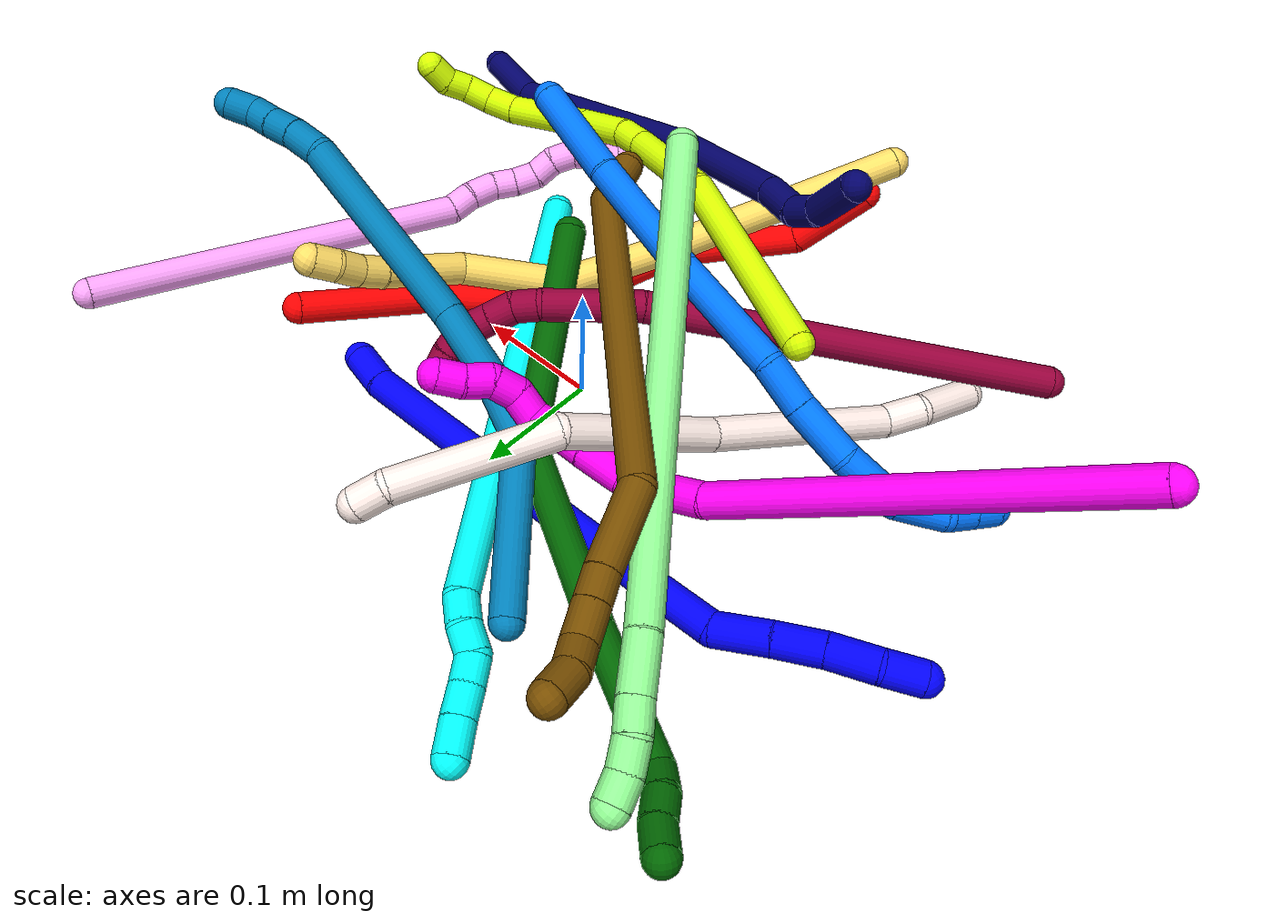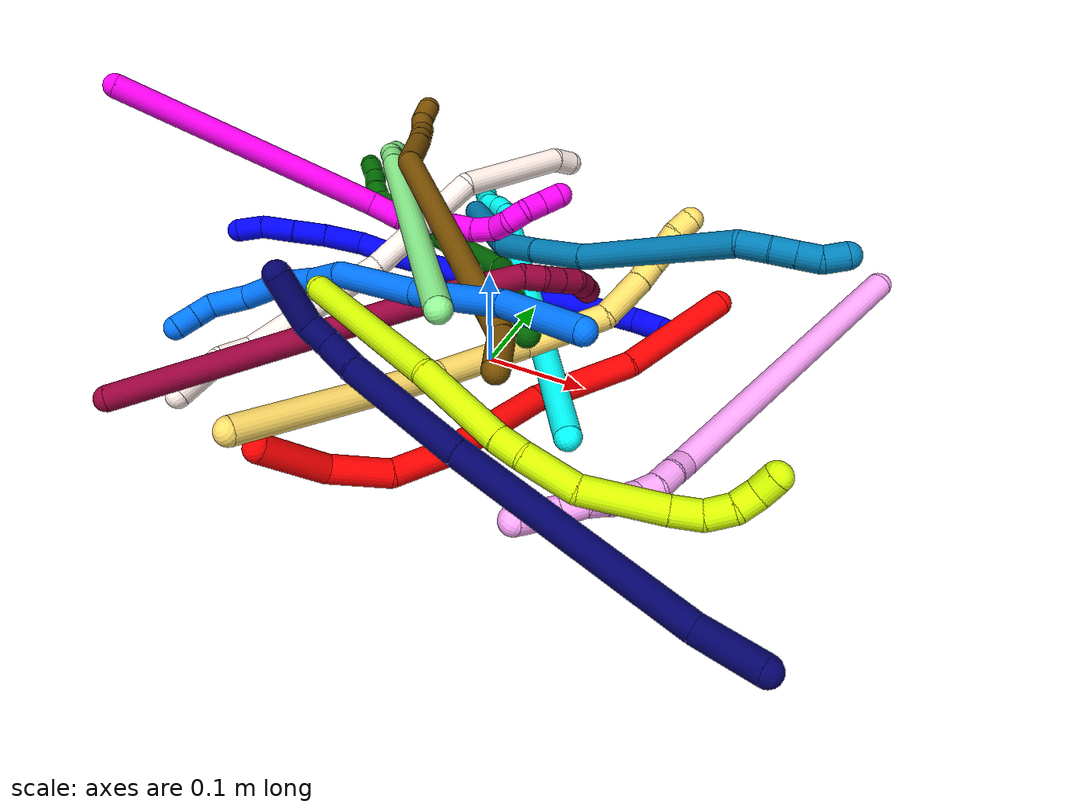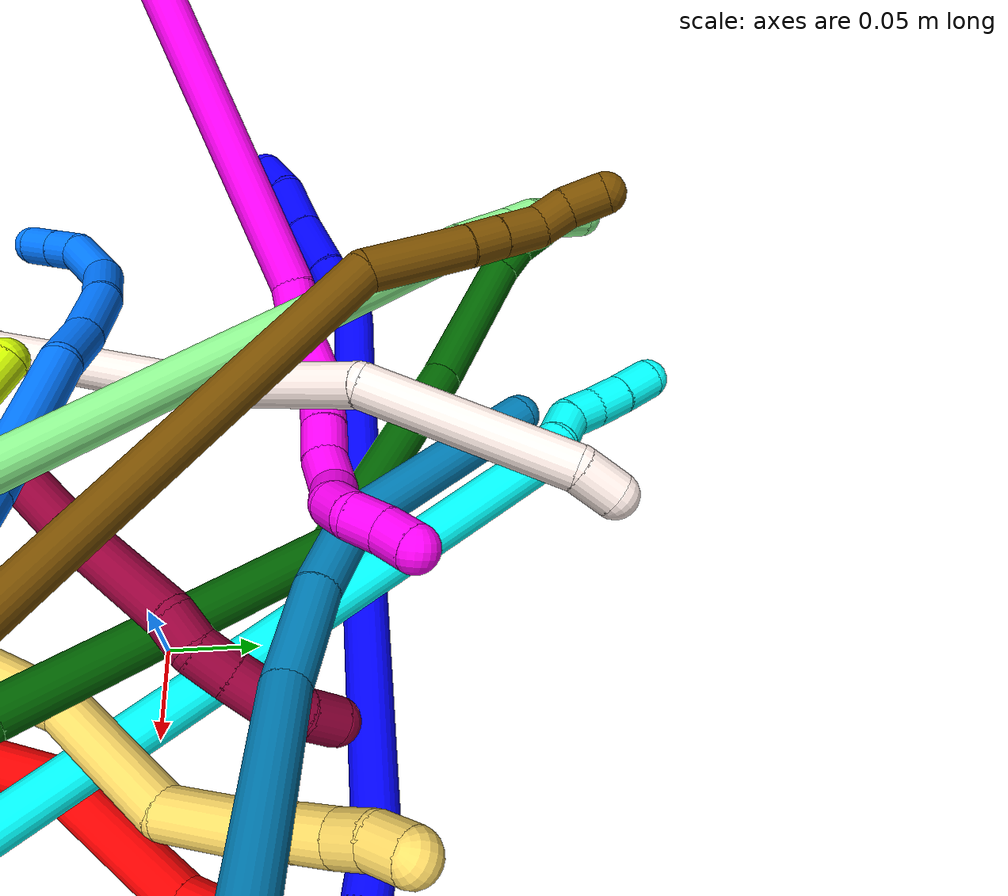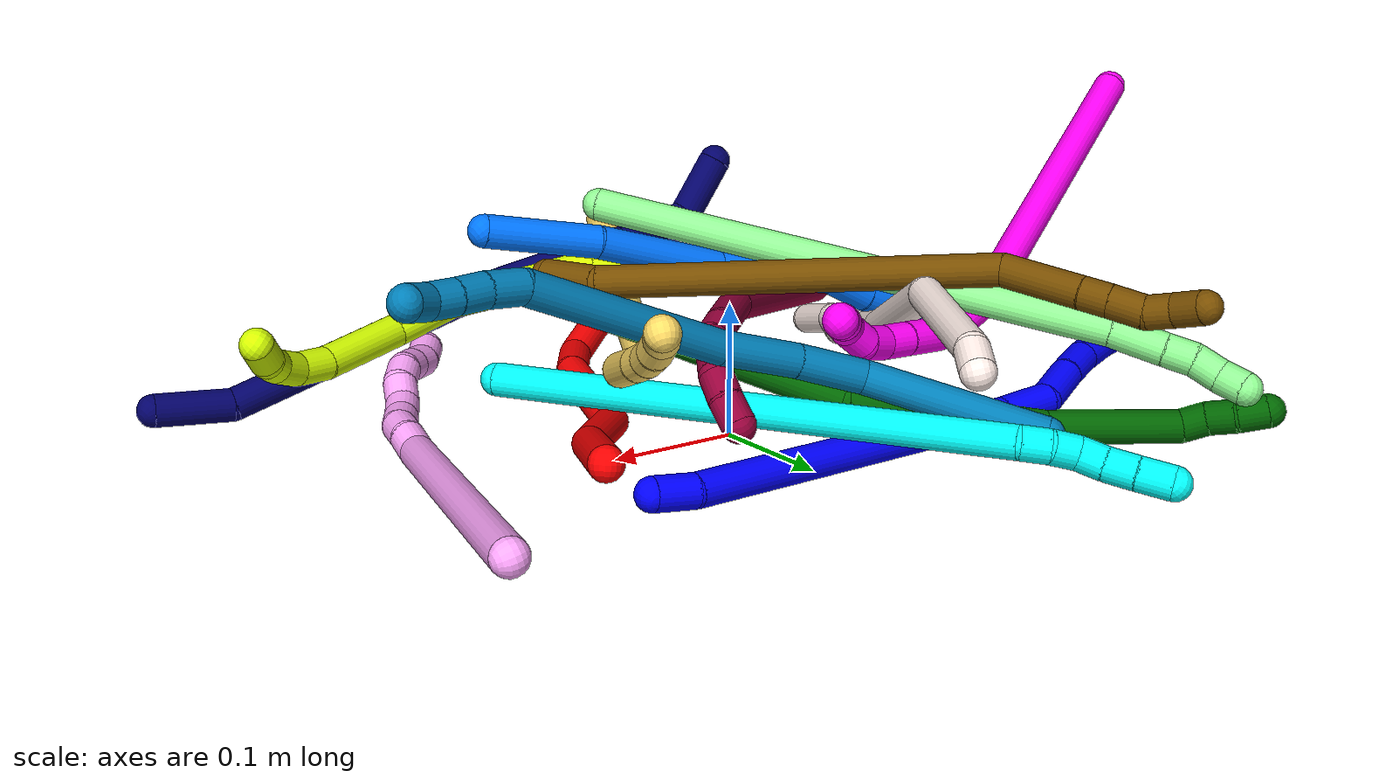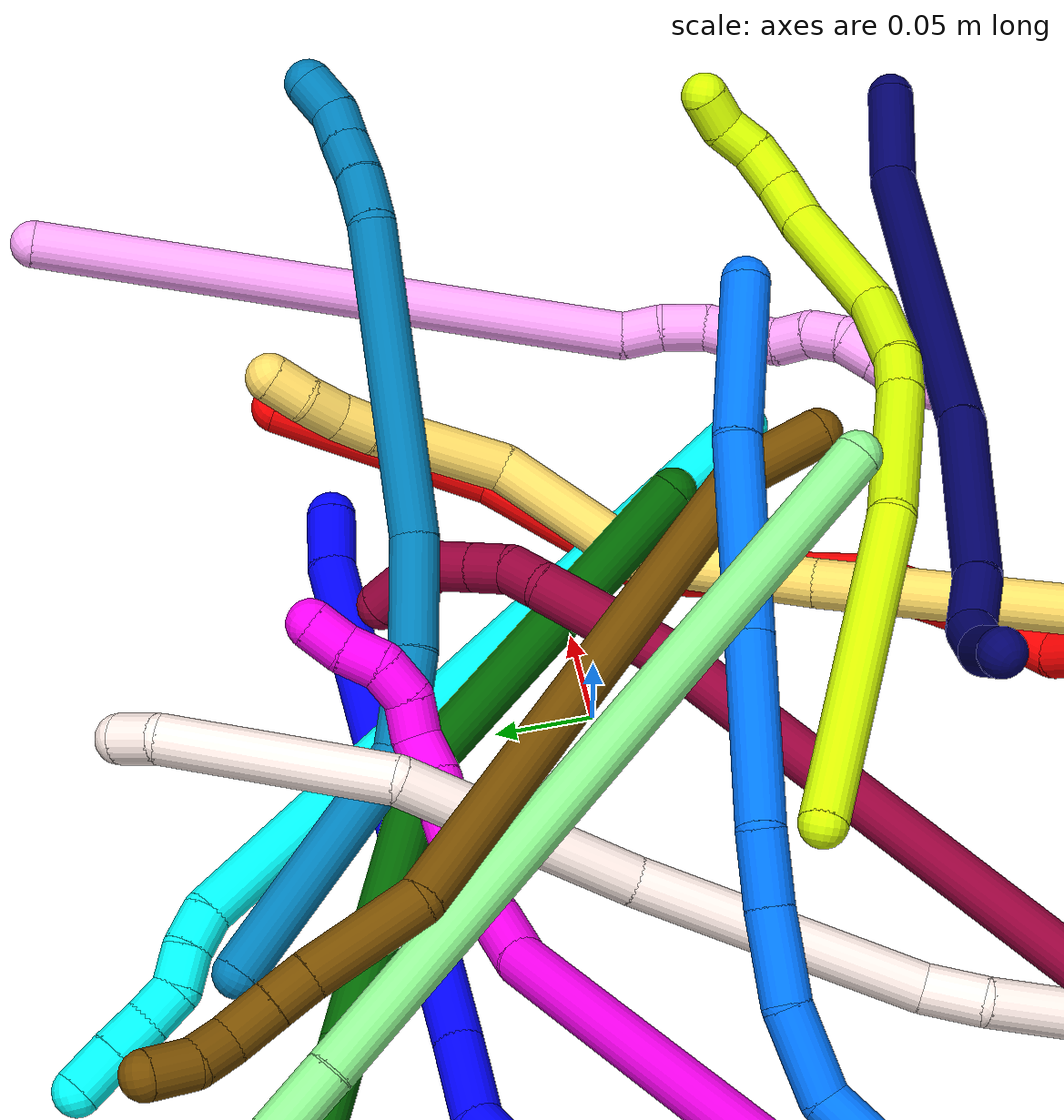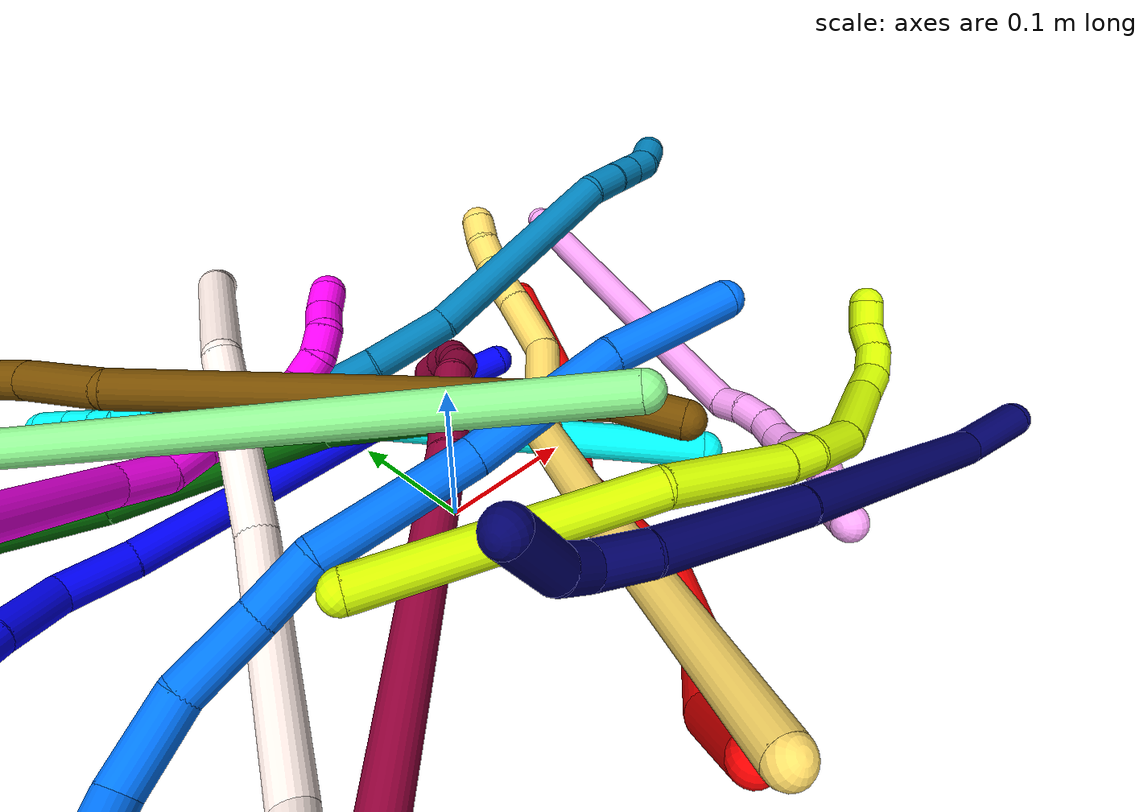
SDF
<sdf version="1.7">
 <world name="default">
  <plugin name="TubeGeneratorPlugin" filename="libtube_generator_plugin.so"/>
  <model name="photoneo_s_sensor">
   <static>1</static>
   <pose>0 0 2 1.57079 1.57079 3.14159</pose>
   <link name="link">
    <inertial><mass>0.1</mass></inertial>
    <sensor name="sensor" type="depth">
     <update_rate>30</update_rate>
     <camera>
      <horizontal_fov>1.22</horizontal_fov>
      <image><width>1920</width><height>1200</height><format>B8G8R8</format></image>
      <clip><near>0.1</near><far>4</far></clip>
      <depth_camera><output>points</output></depth_camera>
     </camera>
     <plugin name="camera_plugin" filename="libgazebo_ros_depth_camera.so">
      <baseline>0.2</baseline>
      <alwaysOn>1</alwaysOn>
      <updateRate>0.0</updateRate>
      <cameraName>camera_ir</cameraName>
      <imageTopicName>/camera/color/image_raw</imageTopicName>
      <cameraInfoTopicName>/camera/color/camera_info</cameraInfoTopicName>
      <depthImageTopicName>/camera/depth/image_raw</depthImageTopicName>
      <depthImageCameraInfoTopicName>/camera/depth/camera_info</depthImageCameraInfoTopicName>
      <pointCloudTopicName>/camera/depth/points</pointCloudTopicName>
      <frameName>fr_optical</frameName>
      <pointCloudCutoff>0.1</pointCloudCutoff>
      <pointCloudCutoffMax>2.0</pointCloudCutoffMax>
      <distortionK1>0</distortionK1>
      <distortionK2>0</distortionK2>
      <distortionK3>0</distortionK3>
      <distortionT1>0</distortionT1>
      <distortionT2>0</distortionT2>
      <CxPrime>0</CxPrime>
      <Cx>0</Cx>
      <Cy>0</Cy>
      <focalLength>0</focalLength>
      <hackBaseline>0</hackBaseline>
     </plugin>
    </sensor>
   </link>
  </model>
  <gravity>0 0 -9.8</gravity>
  <magnetic_field>6e-06 2.3e-05 -4.2e-05</magnetic_field>
  <atmosphere type="adiabatic"/>
  <physics name="default_physics" default="0" type="ode">
   <max_step_size>0.003</max_step_size>
   <real_time_factor>1</real_time_factor>
   <real_time_update_rate>1000</real_time_update_rate>
   <max_contacts>10000</max_contacts>
   <ode>
    <solver>
     <type>quick</type>
     <iters>100</iters>
     <sor>1.3</sor>
     <use_dynamic_moi_rescaling>0</use_dynamic_moi_rescaling>
    </solver>
    <constraints>
     <contact_max_correcting_vel>0</contact_max_correcting_vel>
     <contact_surface_layer>0.001</contact_surface_layer>
     <cfm>0</cfm>
     <erp>0.2</erp>
    </constraints>
   </ode>
  </physics>
  <scene><ambient>0.4 0.4 0.4 1</ambient><background>0.7 0.7 0.7 1</background><shadows>0</shadows></scene>
  <audio><device>default</device></audio>
  <spherical_coordinates>
   <surface_model>EARTH_WGS84</surface_model>
   <latitude_deg>0</latitude_deg>
   <longitude_deg>0</longitude_deg>
   <elevation>0</elevation>
   <heading_deg>0</heading_deg>
  </spherical_coordinates>
  <model name="bin">
   <static>1</static>
   <link name="bottom">
    <collision name="collision-bottom">
     <pose>0 0 -0.01 0 -0 0</pose>
     <geometry><box><size>0.8 0.6 0.02</size></box></geometry>
     <surface>
      <friction><ode><mu>100</mu><mu2>100</mu2></ode></friction>
      <contact><collide_bitmask>65535</collide_bitmask></contact>
     </surface>
    </collision>
   </link>
   <link name="west_wall">
    <collision name="collision-west_wall">
     <pose>-0.41 0 0.1 0 -0 0</pose>
     <geometry><box><size>0.02 0.6 0.2</size></box></geometry>
     <surface>
      <friction><ode><mu>100</mu><mu2>100</mu2></ode></friction>
      <contact><collide_bitmask>65535</collide_bitmask></contact>
     </surface>
    </collision>
   </link>
   <link name="east_wall">
    <collision name="collision-east_wall">
     <pose>0.41 0 0.1 0 -0 0</pose>
     <geometry><box><size>0.02 0.6 0.2</size></box></geometry>
     <surface>
      <friction><ode><mu>100</mu><mu2>100</mu2></ode></friction>
      <contact><collide_bitmask>65535</collide_bitmask></contact>
     </surface>
    </collision>
   </link>
   <link name="south_wall">
    <collision name="collision-south_wall">
     <pose>0 -0.31 0.1 0 -0 0</pose>
     <geometry><box><size>0.8 0.02 0.2</size></box></geometry>
     <surface>
      <friction><ode><mu>100</mu><mu2>100</mu2></ode></friction>
      <contact><collide_bitmask>65535</collide_bitmask></contact>
     </surface>
    </collision>
   </link>
   <link name="north_wall">
    <collision name="collision-north_wall">
     <pose>0 0.31 0.1 0 -0 0</pose>
     <geometry><box><size>0.8 0.02 0.2</size></box></geometry>
     <surface>
      <friction><ode><mu>100</mu><mu2>100</mu2></ode></friction>
      <contact><collide_bitmask>65535</collide_bitmask></contact>
     </surface>
    </collision>
   </link>
  </model>
  <model name="1">
   <static>0</static>
   <link name="1">
    <collision name="collision-cylinder-e_1_1_4">
     <pose>-0.01558 0.000152 -0.001564 -3.04487 -1.47028 3.03465</pose>
     <geometry><cylinder><radius>0.0125</radius><length>0.031319</length></cylinder></geometry>
     <surface>
      <friction><ode><mu>1.16</mu><mu2>1.16</mu2><slip1>0</slip1><slip2>0</slip2></ode></friction>
      <contact><ode><kp>1e+06</kp><kd>1</kd><max_vel>0</max_vel><min_depth>0.001</min_depth></ode></contact>
     </surface>
    </collision>
    <visual name="visual-cylinder-e_1_1_4">
     <pose>-0.01558 0.000152 -0.001564 -3.04487 -1.47028 3.03465</pose>
     <geometry><cylinder><radius>0.0125</radius><length>0.031319</length></cylinder></geometry>
     <material><ambient>0 0 1 1</ambient></material>
    </visual>
    <collision name="collision-cylinder-e_2_4_5">
     <pose>-0.166059 -0.002527 -0.047257 3.07755 -1.25404 -3.05323</pose>
     <geometry><cylinder><radius>0.0125</radius><length>0.283922</length></cylinder></geometry>
     <surface>
      <friction><ode><mu>1.16</mu><mu2>1.16</mu2><slip1>0</slip1><slip2>0</slip2></ode></friction>
      <contact><ode><kp>1e+06</kp><kd>1</kd><max_vel>0</max_vel><min_depth>0.001</min_depth></ode></contact>
     </surface>
    </collision>
    <visual name="visual-cylinder-e_2_4_5">
     <pose>-0.166059 -0.002527 -0.047257 3.07755 -1.25404 -3.05323</pose>
     <geometry><cylinder><radius>0.0125</radius><length>0.283922</length></cylinder></geometry>
     <material><ambient>0 0 1 1</ambient></material>
    </visual>
    <collision name="collision-cylinder-e_3_5_6">
     <pose>-0.32212 -0.00761 -0.09811 2.81826 -1.24744 -2.69581</pose>
     <geometry><cylinder><radius>0.0125</radius><length>0.044638</length></cylinder></geometry>
     <surface>
      <friction><ode><mu>1.16</mu><mu2>1.16</mu2><slip1>0</slip1><slip2>0</slip2></ode></friction>
      <contact><ode><kp>1e+06</kp><kd>1</kd><max_vel>0</max_vel><min_depth>0.001</min_depth></ode></contact>
     </surface>
    </collision>
    <visual name="visual-cylinder-e_3_5_6">
     <pose>-0.32212 -0.00761 -0.09811 2.81826 -1.24744 -2.69581</pose>
     <geometry><cylinder><radius>0.0125</radius><length>0.044638</length></cylinder></geometry>
     <material><ambient>0 0 1 1</ambient></material>
    </visual>
    <collision name="collision-cylinder-e_4_6_7">
     <pose>-0.35823 -0.01334 -0.118954 2.90014 -0.799183 -2.58212</pose>
     <geometry><cylinder><radius>0.0125</radius><length>0.041708</length></cylinder></geometry>
     <surface>
      <friction><ode><mu>1.16</mu><mu2>1.16</mu2><slip1>0</slip1><slip2>0</slip2></ode></friction>
      <contact><ode><kp>1e+06</kp><kd>1</kd><max_vel>0</max_vel><min_depth>0.001</min_depth></ode></contact>
     </surface>
    </collision>
    <visual name="visual-cylinder-e_4_6_7">
     <pose>-0.35823 -0.01334 -0.118954 2.90014 -0.799183 -2.58212</pose>
     <geometry><cylinder><radius>0.0125</radius><length>0.041708</length></cylinder></geometry>
     <material><ambient>0 0 1 1</ambient></material>
    </visual>
    <collision name="collision-cylinder-e_5_7_8">
     <pose>-0.38592 -0.018161 -0.145033 3.02974 -0.813932 -2.88327</pose>
     <geometry><cylinder><radius>0.0125</radius><length>0.035055</length></cylinder></geometry>
     <surface>
      <friction><ode><mu>1.16</mu><mu2>1.16</mu2><slip1>0</slip1><slip2>0</slip2></ode></friction>
      <contact><ode><kp>1e+06</kp><kd>1</kd><max_vel>0</max_vel><min_depth>0.001</min_depth></ode></contact>
     </surface>
    </collision>
    <visual name="visual-cylinder-e_5_7_8">
     <pose>-0.38592 -0.018161 -0.145033 3.02974 -0.813932 -2.88327</pose>
     <geometry><cylinder><radius>0.0125</radius><length>0.035055</length></cylinder></geometry>
     <material><ambient>0 0 1 1</ambient></material>
    </visual>
    <collision name="collision-cylinder-e_6_8_9">
     <pose>-0.412641 -0.020431 -0.167875 3.05663 -0.90755 -2.96773</pose>
     <geometry><cylinder><radius>0.0125</radius><length>0.035478</length></cylinder></geometry>
     <surface>
      <friction><ode><mu>1.16</mu><mu2>1.16</mu2><slip1>0</slip1><slip2>0</slip2></ode></friction>
      <contact><ode><kp>1e+06</kp><kd>1</kd><max_vel>0</max_vel><min_depth>0.001</min_depth></ode></contact>
     </surface>
    </collision>
    <visual name="visual-cylinder-e_6_8_9">
     <pose>-0.412641 -0.020431 -0.167875 3.05663 -0.90755 -2.96773</pose>
     <geometry><cylinder><radius>0.0125</radius><length>0.035478</length></cylinder></geometry>
     <material><ambient>0 0 1 1</ambient></material>
    </visual>
    <collision name="collision-cylinder-e_7_9_2">
     <pose>-0.436159 -0.018555 -0.188528 -2.86223 -0.753693 2.45888</pose>
     <geometry><cylinder><radius>0.0125</radius><length>0.02788</length></cylinder></geometry>
     <surface>
      <friction><ode><mu>1.16</mu><mu2>1.16</mu2><slip1>0</slip1><slip2>0</slip2></ode></friction>
      <contact><ode><kp>1e+06</kp><kd>1</kd><max_vel>0</max_vel><min_depth>0.001</min_depth></ode></contact>
     </surface>
    </collision>
    <visual name="visual-cylinder-e_7_9_2">
     <pose>-0.436159 -0.018555 -0.188528 -2.86223 -0.753693 2.45888</pose>
     <geometry><cylinder><radius>0.0125</radius><length>0.02788</length></cylinder></geometry>
     <material><ambient>0 0 1 1</ambient></material>
    </visual>
    <collision name="collision-sphere-2">
     <pose>-0.445698 -0.015752 -0.198299 0 -0 0</pose>
     <geometry><sphere><radius>0.0125</radius></sphere></geometry>
     <surface>
      <friction><ode><mu>1.16</mu><mu2>1.16</mu2><slip1>0</slip1><slip2>0</slip2></ode></friction>
      <contact><ode><kp>1e+06</kp><kd>1</kd><max_vel>0</max_vel><min_depth>0.001</min_depth></ode></contact>
     </surface>
    </collision>
    <visual name="visual-sphere-2">
     <pose>-0.445698 -0.015752 -0.198299 0 -0 0</pose>
     <geometry><sphere><radius>0.0125</radius></sphere></geometry>
     <material><ambient>0 0 1 1</ambient></material>
    </visual>
    <collision name="collision-sphere-9">
     <pose>-0.426619 -0.021358 -0.178758 0 -0 0</pose>
     <geometry><sphere><radius>0.0125</radius></sphere></geometry>
     <surface>
      <friction><ode><mu>1.16</mu><mu2>1.16</mu2><slip1>0</slip1><slip2>0</slip2></ode></friction>
      <contact><ode><kp>1e+06</kp><kd>1</kd><max_vel>0</max_vel><min_depth>0.001</min_depth></ode></contact>
     </surface>
    </collision>
    <visual name="visual-sphere-9">
     <pose>-0.426619 -0.021358 -0.178758 0 -0 0</pose>
     <geometry><sphere><radius>0.0125</radius></sphere></geometry>
     <material><ambient>0 0 1 1</ambient></material>
    </visual>
    <collision name="collision-sphere-4">
     <pose>-0.03116 0.000303 -0.003128 0 -0 0</pose>
     <geometry><sphere><radius>0.0125</radius></sphere></geometry>
     <surface>
      <friction><ode><mu>1.16</mu><mu2>1.16</mu2><slip1>0</slip1><slip2>0</slip2></ode></friction>
      <contact><ode><kp>1e+06</kp><kd>1</kd><max_vel>0</max_vel><min_depth>0.001</min_depth></ode></contact>
     </surface>
    </collision>
    <visual name="visual-sphere-4">
     <pose>-0.03116 0.000303 -0.003128 0 -0 0</pose>
     <geometry><sphere><radius>0.0125</radius></sphere></geometry>
     <material><ambient>0 0 1 1</ambient></material>
    </visual>
    <collision name="collision-sphere-1">
     <geometry><sphere><radius>0.0125</radius></sphere></geometry>
     <surface>
      <friction><ode><mu>1.16</mu><mu2>1.16</mu2><slip1>0</slip1><slip2>0</slip2></ode></friction>
      <contact><ode><kp>1e+06</kp><kd>1</kd><max_vel>0</max_vel><min_depth>0.001</min_depth></ode></contact>
     </surface>
    </collision>
    <visual name="visual-sphere-1">
     <geometry><sphere><radius>0.0125</radius></sphere></geometry>
     <material><ambient>0 0 1 1</ambient></material>
    </visual>
    <collision name="collision-sphere-8">
     <pose>-0.398662 -0.019504 -0.156993 0 -0 0</pose>
     <geometry><sphere><radius>0.0125</radius></sphere></geometry>
     <surface>
      <friction><ode><mu>1.16</mu><mu2>1.16</mu2><slip1>0</slip1><slip2>0</slip2></ode></friction>
      <contact><ode><kp>1e+06</kp><kd>1</kd><max_vel>0</max_vel><min_depth>0.001</min_depth></ode></contact>
     </surface>
    </collision>
    <visual name="visual-sphere-8">
     <pose>-0.398662 -0.019504 -0.156993 0 -0 0</pose>
     <geometry><sphere><radius>0.0125</radius></sphere></geometry>
     <material><ambient>0 0 1 1</ambient></material>
    </visual>
    <collision name="collision-sphere-5">
     <pose>-0.300957 -0.005357 -0.091385 0 -0 0</pose>
     <geometry><sphere><radius>0.0125</radius></sphere></geometry>
     <surface>
      <friction><ode><mu>1.16</mu><mu2>1.16</mu2><slip1>0</slip1><slip2>0</slip2></ode></friction>
      <contact><ode><kp>1e+06</kp><kd>1</kd><max_vel>0</max_vel><min_depth>0.001</min_depth></ode></contact>
     </surface>
    </collision>
    <visual name="visual-sphere-5">
     <pose>-0.300957 -0.005357 -0.091385 0 -0 0</pose>
     <geometry><sphere><radius>0.0125</radius></sphere></geometry>
     <material><ambient>0 0 1 1</ambient></material>
    </visual>
    <collision name="collision-sphere-6">
     <pose>-0.343282 -0.009863 -0.104834 0 -0 0</pose>
     <geometry><sphere><radius>0.0125</radius></sphere></geometry>
     <surface>
      <friction><ode><mu>1.16</mu><mu2>1.16</mu2><slip1>0</slip1><slip2>0</slip2></ode></friction>
      <contact><ode><kp>1e+06</kp><kd>1</kd><max_vel>0</max_vel><min_depth>0.001</min_depth></ode></contact>
     </surface>
    </collision>
    <visual name="visual-sphere-6">
     <pose>-0.343282 -0.009863 -0.104834 0 -0 0</pose>
     <geometry><sphere><radius>0.0125</radius></sphere></geometry>
     <material><ambient>0 0 1 1</ambient></material>
    </visual>
    <collision name="collision-sphere-7">
     <pose>-0.373178 -0.016817 -0.133073 0 -0 0</pose>
     <geometry><sphere><radius>0.0125</radius></sphere></geometry>
     <surface>
      <friction><ode><mu>1.16</mu><mu2>1.16</mu2><slip1>0</slip1><slip2>0</slip2></ode></friction>
      <contact><ode><kp>1e+06</kp><kd>1</kd><max_vel>0</max_vel><min_depth>0.001</min_depth></ode></contact>
     </surface>
    </collision>
    <visual name="visual-sphere-7">
     <pose>-0.373178 -0.016817 -0.133073 0 -0 0</pose>
     <geometry><sphere><radius>0.0125</radius></sphere></geometry>
     <material><ambient>0 0 1 1</ambient></material>
    </visual>
    <inertial>
     <pose>-0.234568 -0.006975 -0.078207 0 -0 0</pose>
     <mass>0.5</mass>
     <inertia>
      <ixx>-0.000702</ixx>
      <ixy>0</ixy>
      <ixz>0</ixz>
      <iyy>0.001891</iyy>
      <iyz>0</iyz>
      <izz>0.001875</izz>
     </inertia>
    </inertial>
   </link>
   <pose>0.140373 0.106531 0.013632 -1.74118 -0.075998 -0.28297</pose>
  </model>
  <model name="2">
   <static>0</static>
   <link name="2">
    <collision name="collision-cylinder-e_1_1_4">
     <pose>-0.027025 -0.051498 0.000444 1.56217 -0.483252 -0.479261</pose>
     <geometry><cylinder><radius>0.0125</radius><length>0.11632</length></cylinder></geometry>
     <surface>
      <friction><ode><mu>1.16</mu><mu2>1.16</mu2><slip1>0</slip1><slip2>0</slip2></ode></friction>
      <contact><ode><kp>1e+06</kp><kd>1</kd><max_vel>0</max_vel><min_depth>0.001</min_depth></ode></contact>
     </surface>
    </collision>
    <visual name="visual-cylinder-e_1_1_4">
     <pose>-0.027025 -0.051498 0.000444 1.56217 -0.483252 -0.479261</pose>
     <geometry><cylinder><radius>0.0125</radius><length>0.11632</length></cylinder></geometry>
     <material><ambient>1 0 0 1</ambient></material>
    </visual>
    <collision name="collision-cylinder-e_2_4_5">
     <pose>-0.08628 -0.138172 0.004632 1.46476 -0.738924 -0.670166</pose>
     <geometry><cylinder><radius>0.0125</radius><length>0.095712</length></cylinder></geometry>
     <surface>
      <friction><ode><mu>1.16</mu><mu2>1.16</mu2><slip1>0</slip1><slip2>0</slip2></ode></friction>
      <contact><ode><kp>1e+06</kp><kd>1</kd><max_vel>0</max_vel><min_depth>0.001</min_depth></ode></contact>
     </surface>
    </collision>
    <visual name="visual-cylinder-e_2_4_5">
     <pose>-0.08628 -0.138172 0.004632 1.46476 -0.738924 -0.670166</pose>
     <geometry><cylinder><radius>0.0125</radius><length>0.095712</length></cylinder></geometry>
     <material><ambient>1 0 0 1</ambient></material>
    </visual>
    <collision name="collision-cylinder-e_3_5_6">
     <pose>-0.13395 -0.225882 0.022948 1.30023 -0.275983 -0.210416</pose>
     <geometry><cylinder><radius>0.0125</radius><length>0.113324</length></cylinder></geometry>
     <surface>
      <friction><ode><mu>1.16</mu><mu2>1.16</mu2><slip1>0</slip1><slip2>0</slip2></ode></friction>
      <contact><ode><kp>1e+06</kp><kd>1</kd><max_vel>0</max_vel><min_depth>0.001</min_depth></ode></contact>
     </surface>
    </collision>
    <visual name="visual-cylinder-e_3_5_6">
     <pose>-0.13395 -0.225882 0.022948 1.30023 -0.275983 -0.210416</pose>
     <geometry><cylinder><radius>0.0125</radius><length>0.113324</length></cylinder></geometry>
     <material><ambient>1 0 0 1</ambient></material>
    </visual>
    <collision name="collision-cylinder-e_4_6_7">
     <pose>-0.163865 -0.299463 0.042777 1.326 -0.588387 -0.464671</pose>
     <geometry><cylinder><radius>0.0125</radius><length>0.052157</length></cylinder></geometry>
     <surface>
      <friction><ode><mu>1.16</mu><mu2>1.16</mu2><slip1>0</slip1><slip2>0</slip2></ode></friction>
      <contact><ode><kp>1e+06</kp><kd>1</kd><max_vel>0</max_vel><min_depth>0.001</min_depth></ode></contact>
     </surface>
    </collision>
    <visual name="visual-cylinder-e_4_6_7">
     <pose>-0.163865 -0.299463 0.042777 1.326 -0.588387 -0.464671</pose>
     <geometry><cylinder><radius>0.0125</radius><length>0.052157</length></cylinder></geometry>
     <material><ambient>1 0 0 1</ambient></material>
    </visual>
    <collision name="collision-cylinder-e_5_7_8">
     <pose>-0.19806 -0.334969 0.060869 0.844853 -0.795338 -0.373218</pose>
     <geometry><cylinder><radius>0.0125</radius><length>0.055235</length></cylinder></geometry>
     <surface>
      <friction><ode><mu>1.16</mu><mu2>1.16</mu2><slip1>0</slip1><slip2>0</slip2></ode></friction>
      <contact><ode><kp>1e+06</kp><kd>1</kd><max_vel>0</max_vel><min_depth>0.001</min_depth></ode></contact>
     </surface>
    </collision>
    <visual name="visual-cylinder-e_5_7_8">
     <pose>-0.19806 -0.334969 0.060869 0.844853 -0.795338 -0.373218</pose>
     <geometry><cylinder><radius>0.0125</radius><length>0.055235</length></cylinder></geometry>
     <material><ambient>1 0 0 1</ambient></material>
    </visual>
    <collision name="collision-cylinder-e_6_8_2">
     <pose>-0.230114 -0.366056 0.100201 0.560418 -0.375506 -0.109242</pose>
     <geometry><cylinder><radius>0.0125</radius><length>0.067252</length></cylinder></geometry>
     <surface>
      <friction><ode><mu>1.16</mu><mu2>1.16</mu2><slip1>0</slip1><slip2>0</slip2></ode></friction>
      <contact><ode><kp>1e+06</kp><kd>1</kd><max_vel>0</max_vel><min_depth>0.001</min_depth></ode></contact>
     </surface>
    </collision>
    <visual name="visual-cylinder-e_6_8_2">
     <pose>-0.230114 -0.366056 0.100201 0.560418 -0.375506 -0.109242</pose>
     <geometry><cylinder><radius>0.0125</radius><length>0.067252</length></cylinder></geometry>
     <material><ambient>1 0 0 1</ambient></material>
    </visual>
    <collision name="collision-sphere-2">
     <pose>-0.242446 -0.382684 0.126699 0 -0 0</pose>
     <geometry><sphere><radius>0.0125</radius></sphere></geometry>
     <surface>
      <friction><ode><mu>1.16</mu><mu2>1.16</mu2><slip1>0</slip1><slip2>0</slip2></ode></friction>
      <contact><ode><kp>1e+06</kp><kd>1</kd><max_vel>0</max_vel><min_depth>0.001</min_depth></ode></contact>
     </surface>
    </collision>
    <visual name="visual-sphere-2">
     <pose>-0.242446 -0.382684 0.126699 0 -0 0</pose>
     <geometry><sphere><radius>0.0125</radius></sphere></geometry>
     <material><ambient>1 0 0 1</ambient></material>
    </visual>
    <collision name="collision-sphere-4">
     <pose>-0.054049 -0.102996 0.000888 0 -0 0</pose>
     <geometry><sphere><radius>0.0125</radius></sphere></geometry>
     <surface>
      <friction><ode><mu>1.16</mu><mu2>1.16</mu2><slip1>0</slip1><slip2>0</slip2></ode></friction>
      <contact><ode><kp>1e+06</kp><kd>1</kd><max_vel>0</max_vel><min_depth>0.001</min_depth></ode></contact>
     </surface>
    </collision>
    <visual name="visual-sphere-4">
     <pose>-0.054049 -0.102996 0.000888 0 -0 0</pose>
     <geometry><sphere><radius>0.0125</radius></sphere></geometry>
     <material><ambient>1 0 0 1</ambient></material>
    </visual>
    <collision name="collision-sphere-1">
     <geometry><sphere><radius>0.0125</radius></sphere></geometry>
     <surface>
      <friction><ode><mu>1.16</mu><mu2>1.16</mu2><slip1>0</slip1><slip2>0</slip2></ode></friction>
      <contact><ode><kp>1e+06</kp><kd>1</kd><max_vel>0</max_vel><min_depth>0.001</min_depth></ode></contact>
     </surface>
    </collision>
    <visual name="visual-sphere-1">
     <geometry><sphere><radius>0.0125</radius></sphere></geometry>
     <material><ambient>1 0 0 1</ambient></material>
    </visual>
    <collision name="collision-sphere-8">
     <pose>-0.217782 -0.349428 0.073703 0 -0 0</pose>
     <geometry><sphere><radius>0.0125</radius></sphere></geometry>
     <surface>
      <friction><ode><mu>1.16</mu><mu2>1.16</mu2><slip1>0</slip1><slip2>0</slip2></ode></friction>
      <contact><ode><kp>1e+06</kp><kd>1</kd><max_vel>0</max_vel><min_depth>0.001</min_depth></ode></contact>
     </surface>
    </collision>
    <visual name="visual-sphere-8">
     <pose>-0.217782 -0.349428 0.073703 0 -0 0</pose>
     <geometry><sphere><radius>0.0125</radius></sphere></geometry>
     <material><ambient>1 0 0 1</ambient></material>
    </visual>
    <collision name="collision-sphere-5">
     <pose>-0.11851 -0.173348 0.008376 0 -0 0</pose>
     <geometry><sphere><radius>0.0125</radius></sphere></geometry>
     <surface>
      <friction><ode><mu>1.16</mu><mu2>1.16</mu2><slip1>0</slip1><slip2>0</slip2></ode></friction>
      <contact><ode><kp>1e+06</kp><kd>1</kd><max_vel>0</max_vel><min_depth>0.001</min_depth></ode></contact>
     </surface>
    </collision>
    <visual name="visual-sphere-5">
     <pose>-0.11851 -0.173348 0.008376 0 -0 0</pose>
     <geometry><sphere><radius>0.0125</radius></sphere></geometry>
     <material><ambient>1 0 0 1</ambient></material>
    </visual>
    <collision name="collision-sphere-6">
     <pose>-0.14939 -0.278417 0.037519 0 -0 0</pose>
     <geometry><sphere><radius>0.0125</radius></sphere></geometry>
     <surface>
      <friction><ode><mu>1.16</mu><mu2>1.16</mu2><slip1>0</slip1><slip2>0</slip2></ode></friction>
      <contact><ode><kp>1e+06</kp><kd>1</kd><max_vel>0</max_vel><min_depth>0.001</min_depth></ode></contact>
     </surface>
    </collision>
    <visual name="visual-sphere-6">
     <pose>-0.14939 -0.278417 0.037519 0 -0 0</pose>
     <geometry><sphere><radius>0.0125</radius></sphere></geometry>
     <material><ambient>1 0 0 1</ambient></material>
    </visual>
    <collision name="collision-sphere-7">
     <pose>-0.178339 -0.32051 0.048034 0 -0 0</pose>
     <geometry><sphere><radius>0.0125</radius></sphere></geometry>
     <surface>
      <friction><ode><mu>1.16</mu><mu2>1.16</mu2><slip1>0</slip1><slip2>0</slip2></ode></friction>
      <contact><ode><kp>1e+06</kp><kd>1</kd><max_vel>0</max_vel><min_depth>0.001</min_depth></ode></contact>
     </surface>
    </collision>
    <visual name="visual-sphere-7">
     <pose>-0.178339 -0.32051 0.048034 0 -0 0</pose>
     <geometry><sphere><radius>0.0125</radius></sphere></geometry>
     <material><ambient>1 0 0 1</ambient></material>
    </visual>
    <inertial>
     <pose>-0.123087 -0.207104 0.030855 0 -0 0</pose>
     <mass>0.5</mass>
     <inertia><ixx>0.000169</ixx><ixy>0</ixy><ixz>0</ixz><iyy>-6e-06</iyy><iyz>0</iyz><izz>0.000515</izz></inertia>
    </inertial>
   </link>
   <pose>0.187956 0.125175 0.049649 0.154969 -0.16923 -0.00711</pose>
  </model>
  <model name="3">
   <static>0</static>
   <link name="3">
    <collision name="collision-cylinder-e_1_1_4">
     <pose>-0.156184 0.083893 -0.081593 -2.3423 -0.927747 1.73927</pose>
     <geometry><cylinder><radius>0.0125</radius><length>0.390327</length></cylinder></geometry>
     <surface>
      <friction><ode><mu>1.16</mu><mu2>1.16</mu2><slip1>0</slip1><slip2>0</slip2></ode></friction>
      <contact><ode><kp>1e+06</kp><kd>1</kd><max_vel>0</max_vel><min_depth>0.001</min_depth></ode></contact>
     </surface>
    </collision>
    <visual name="visual-cylinder-e_1_1_4">
     <pose>-0.156184 0.083893 -0.081593 -2.3423 -0.927747 1.73927</pose>
     <geometry><cylinder><radius>0.0125</radius><length>0.390327</length></cylinder></geometry>
     <material><ambient>0.003922 1 0.996078 1</ambient></material>
    </visual>
    <collision name="collision-cylinder-e_2_4_5">
     <pose>-0.319624 0.170638 -0.170349 -2.76254 -0.755134 2.24056</pose>
     <geometry><cylinder><radius>0.0125</radius><length>0.021173</length></cylinder></geometry>
     <surface>
      <friction><ode><mu>1.16</mu><mu2>1.16</mu2><slip1>0</slip1><slip2>0</slip2></ode></friction>
      <contact><ode><kp>1e+06</kp><kd>1</kd><max_vel>0</max_vel><min_depth>0.001</min_depth></ode></contact>
     </surface>
    </collision>
    <visual name="visual-cylinder-e_2_4_5">
     <pose>-0.319624 0.170638 -0.170349 -2.76254 -0.755134 2.24056</pose>
     <geometry><cylinder><radius>0.0125</radius><length>0.021173</length></cylinder></geometry>
     <material><ambient>0.003922 1 0.996078 1</ambient></material>
    </visual>
    <collision name="collision-cylinder-e_3_5_6">
     <pose>-0.332169 0.175461 -0.186095 -2.91596 -0.54088 2.36567</pose>
     <geometry><cylinder><radius>0.0125</radius><length>0.020548</length></cylinder></geometry>
     <surface>
      <friction><ode><mu>1.16</mu><mu2>1.16</mu2><slip1>0</slip1><slip2>0</slip2></ode></friction>
      <contact><ode><kp>1e+06</kp><kd>1</kd><max_vel>0</max_vel><min_depth>0.001</min_depth></ode></contact>
     </surface>
    </collision>
    <visual name="visual-cylinder-e_3_5_6">
     <pose>-0.332169 0.175461 -0.186095 -2.91596 -0.54088 2.36567</pose>
     <geometry><cylinder><radius>0.0125</radius><length>0.020548</length></cylinder></geometry>
     <material><ambient>0.003922 1 0.996078 1</ambient></material>
    </visual>
    <collision name="collision-cylinder-e_4_6_7">
     <pose>-0.343689 0.183439 -0.200003 -2.29599 -0.660015 1.30137</pose>
     <geometry><cylinder><radius>0.0125</radius><length>0.020322</length></cylinder></geometry>
     <surface>
      <friction><ode><mu>1.16</mu><mu2>1.16</mu2><slip1>0</slip1><slip2>0</slip2></ode></friction>
      <contact><ode><kp>1e+06</kp><kd>1</kd><max_vel>0</max_vel><min_depth>0.001</min_depth></ode></contact>
     </surface>
    </collision>
    <visual name="visual-cylinder-e_4_6_7">
     <pose>-0.343689 0.183439 -0.200003 -2.29599 -0.660015 1.30137</pose>
     <geometry><cylinder><radius>0.0125</radius><length>0.020322</length></cylinder></geometry>
     <material><ambient>0.003922 1 0.996078 1</ambient></material>
    </visual>
    <collision name="collision-cylinder-e_5_7_8">
     <pose>-0.357727 0.195588 -0.210539 -2.27447 -0.769768 1.4377</pose>
     <geometry><cylinder><radius>0.0125</radius><length>0.022437</length></cylinder></geometry>
     <surface>
      <friction><ode><mu>1.16</mu><mu2>1.16</mu2><slip1>0</slip1><slip2>0</slip2></ode></friction>
      <contact><ode><kp>1e+06</kp><kd>1</kd><max_vel>0</max_vel><min_depth>0.001</min_depth></ode></contact>
     </surface>
    </collision>
    <visual name="visual-cylinder-e_5_7_8">
     <pose>-0.357727 0.195588 -0.210539 -2.27447 -0.769768 1.4377</pose>
     <geometry><cylinder><radius>0.0125</radius><length>0.022437</length></cylinder></geometry>
     <material><ambient>0.003922 1 0.996078 1</ambient></material>
    </visual>
    <collision name="collision-cylinder-e_6_8_2">
     <pose>-0.374285 0.208188 -0.222107 -2.34828 -0.767988 1.53482</pose>
     <geometry><cylinder><radius>0.0125</radius><length>0.025193</length></cylinder></geometry>
     <surface>
      <friction><ode><mu>1.16</mu><mu2>1.16</mu2><slip1>0</slip1><slip2>0</slip2></ode></friction>
      <contact><ode><kp>1e+06</kp><kd>1</kd><max_vel>0</max_vel><min_depth>0.001</min_depth></ode></contact>
     </surface>
    </collision>
    <visual name="visual-cylinder-e_6_8_2">
     <pose>-0.374285 0.208188 -0.222107 -2.34828 -0.767988 1.53482</pose>
     <geometry><cylinder><radius>0.0125</radius><length>0.025193</length></cylinder></geometry>
     <material><ambient>0.003922 1 0.996078 1</ambient></material>
    </visual>
    <collision name="collision-sphere-2">
     <pose>-0.383036 0.214645 -0.228463 0 -0 0</pose>
     <geometry><sphere><radius>0.0125</radius></sphere></geometry>
     <surface>
      <friction><ode><mu>1.16</mu><mu2>1.16</mu2><slip1>0</slip1><slip2>0</slip2></ode></friction>
      <contact><ode><kp>1e+06</kp><kd>1</kd><max_vel>0</max_vel><min_depth>0.001</min_depth></ode></contact>
     </surface>
    </collision>
    <visual name="visual-sphere-2">
     <pose>-0.383036 0.214645 -0.228463 0 -0 0</pose>
     <geometry><sphere><radius>0.0125</radius></sphere></geometry>
     <material><ambient>0.003922 1 0.996078 1</ambient></material>
    </visual>
    <collision name="collision-sphere-4">
     <pose>-0.312368 0.167785 -0.163187 0 -0 0</pose>
     <geometry><sphere><radius>0.0125</radius></sphere></geometry>
     <surface>
      <friction><ode><mu>1.16</mu><mu2>1.16</mu2><slip1>0</slip1><slip2>0</slip2></ode></friction>
      <contact><ode><kp>1e+06</kp><kd>1</kd><max_vel>0</max_vel><min_depth>0.001</min_depth></ode></contact>
     </surface>
    </collision>
    <visual name="visual-sphere-4">
     <pose>-0.312368 0.167785 -0.163187 0 -0 0</pose>
     <geometry><sphere><radius>0.0125</radius></sphere></geometry>
     <material><ambient>0.003922 1 0.996078 1</ambient></material>
    </visual>
    <collision name="collision-sphere-1">
     <geometry><sphere><radius>0.0125</radius></sphere></geometry>
     <surface>
      <friction><ode><mu>1.16</mu><mu2>1.16</mu2><slip1>0</slip1><slip2>0</slip2></ode></friction>
      <contact><ode><kp>1e+06</kp><kd>1</kd><max_vel>0</max_vel><min_depth>0.001</min_depth></ode></contact>
     </surface>
    </collision>
    <visual name="visual-sphere-1">
     <geometry><sphere><radius>0.0125</radius></sphere></geometry>
     <material><ambient>0.003922 1 0.996078 1</ambient></material>
    </visual>
    <collision name="collision-sphere-8">
     <pose>-0.365535 0.20173 -0.215751 0 -0 0</pose>
     <geometry><sphere><radius>0.0125</radius></sphere></geometry>
     <surface>
      <friction><ode><mu>1.16</mu><mu2>1.16</mu2><slip1>0</slip1><slip2>0</slip2></ode></friction>
      <contact><ode><kp>1e+06</kp><kd>1</kd><max_vel>0</max_vel><min_depth>0.001</min_depth></ode></contact>
     </surface>
    </collision>
    <visual name="visual-sphere-8">
     <pose>-0.365535 0.20173 -0.215751 0 -0 0</pose>
     <geometry><sphere><radius>0.0125</radius></sphere></geometry>
     <material><ambient>0.003922 1 0.996078 1</ambient></material>
    </visual>
    <collision name="collision-sphere-5">
     <pose>-0.32688 0.173491 -0.17751 0 -0 0</pose>
     <geometry><sphere><radius>0.0125</radius></sphere></geometry>
     <surface>
      <friction><ode><mu>1.16</mu><mu2>1.16</mu2><slip1>0</slip1><slip2>0</slip2></ode></friction>
      <contact><ode><kp>1e+06</kp><kd>1</kd><max_vel>0</max_vel><min_depth>0.001</min_depth></ode></contact>
     </surface>
    </collision>
    <visual name="visual-sphere-5">
     <pose>-0.32688 0.173491 -0.17751 0 -0 0</pose>
     <geometry><sphere><radius>0.0125</radius></sphere></geometry>
     <material><ambient>0.003922 1 0.996078 1</ambient></material>
    </visual>
    <collision name="collision-sphere-6">
     <pose>-0.337459 0.177431 -0.194679 0 -0 0</pose>
     <geometry><sphere><radius>0.0125</radius></sphere></geometry>
     <surface>
      <friction><ode><mu>1.16</mu><mu2>1.16</mu2><slip1>0</slip1><slip2>0</slip2></ode></friction>
      <contact><ode><kp>1e+06</kp><kd>1</kd><max_vel>0</max_vel><min_depth>0.001</min_depth></ode></contact>
     </surface>
    </collision>
    <visual name="visual-sphere-6">
     <pose>-0.337459 0.177431 -0.194679 0 -0 0</pose>
     <geometry><sphere><radius>0.0125</radius></sphere></geometry>
     <material><ambient>0.003922 1 0.996078 1</ambient></material>
    </visual>
    <collision name="collision-sphere-7">
     <pose>-0.349919 0.189446 -0.205327 0 -0 0</pose>
     <geometry><sphere><radius>0.0125</radius></sphere></geometry>
     <surface>
      <friction><ode><mu>1.16</mu><mu2>1.16</mu2><slip1>0</slip1><slip2>0</slip2></ode></friction>
      <contact><ode><kp>1e+06</kp><kd>1</kd><max_vel>0</max_vel><min_depth>0.001</min_depth></ode></contact>
     </surface>
    </collision>
    <visual name="visual-sphere-7">
     <pose>-0.349919 0.189446 -0.205327 0 -0 0</pose>
     <geometry><sphere><radius>0.0125</radius></sphere></geometry>
     <material><ambient>0.003922 1 0.996078 1</ambient></material>
    </visual>
    <inertial>
     <pose>-0.197991 0.10665 -0.107325 0 -0 0</pose>
     <mass>0.5</mass>
     <inertia>
      <ixx>0.002414</ixx>
      <ixy>0</ixy>
      <ixz>0</ixz>
      <iyy>0.006359</iyy>
      <iyz>0</iyz>
      <izz>0.001825</izz>
     </inertia>
    </inertial>
   </link>
   <pose>0.132309 -0.1097 0.038838 -0.834812 0.630093 -0.987264</pose>
  </model>
  <model name="4">
   <static>0</static>
   <link name="4">
    <collision name="collision-cylinder-e_1_1_4">
     <pose>0.019094 -0.154698 -0.022829 1.71731 0.121506 0.140693</pose>
     <geometry><cylinder><radius>0.0125</radius><length>0.315069</length></cylinder></geometry>
     <surface>
      <friction><ode><mu>1.16</mu><mu2>1.16</mu2><slip1>0</slip1><slip2>0</slip2></ode></friction>
      <contact><ode><kp>1e+06</kp><kd>1</kd><max_vel>0</max_vel><min_depth>0.001</min_depth></ode></contact>
     </surface>
    </collision>
    <visual name="visual-cylinder-e_1_1_4">
     <pose>0.019094 -0.154698 -0.022829 1.71731 0.121506 0.140693</pose>
     <geometry><cylinder><radius>0.0125</radius><length>0.315069</length></cylinder></geometry>
     <material><ambient>1 0.65098 0.996078 1</ambient></material>
    </visual>
    <collision name="collision-cylinder-e_2_4_5">
     <pose>0.035196 -0.319573 -0.04645 1.64853 -0.285152 -0.307878</pose>
     <geometry><cylinder><radius>0.0125</radius><length>0.021276</length></cylinder></geometry>
     <surface>
      <friction><ode><mu>1.16</mu><mu2>1.16</mu2><slip1>0</slip1><slip2>0</slip2></ode></friction>
      <contact><ode><kp>1e+06</kp><kd>1</kd><max_vel>0</max_vel><min_depth>0.001</min_depth></ode></contact>
     </surface>
    </collision>
    <visual name="visual-cylinder-e_2_4_5">
     <pose>0.035196 -0.319573 -0.04645 1.64853 -0.285152 -0.307878</pose>
     <geometry><cylinder><radius>0.0125</radius><length>0.021276</length></cylinder></geometry>
     <material><ambient>1 0.65098 0.996078 1</ambient></material>
    </visual>
    <collision name="collision-cylinder-e_3_5_6">
     <pose>0.031536 -0.34146 -0.048485 1.6765 -0.056613 -0.062934</pose>
     <geometry><cylinder><radius>0.0125</radius><length>0.023589</length></cylinder></geometry>
     <surface>
      <friction><ode><mu>1.16</mu><mu2>1.16</mu2><slip1>0</slip1><slip2>0</slip2></ode></friction>
      <contact><ode><kp>1e+06</kp><kd>1</kd><max_vel>0</max_vel><min_depth>0.001</min_depth></ode></contact>
     </surface>
    </collision>
    <visual name="visual-cylinder-e_3_5_6">
     <pose>0.031536 -0.34146 -0.048485 1.6765 -0.056613 -0.062934</pose>
     <geometry><cylinder><radius>0.0125</radius><length>0.023589</length></cylinder></geometry>
     <material><ambient>1 0.65098 0.996078 1</ambient></material>
    </visual>
    <collision name="collision-cylinder-e_4_6_7">
     <pose>0.031318 -0.362327 -0.053731 1.98297 0.044893 0.06861</pose>
     <geometry><cylinder><radius>0.0125</radius><length>0.02001</length></cylinder></geometry>
     <surface>
      <friction><ode><mu>1.16</mu><mu2>1.16</mu2><slip1>0</slip1><slip2>0</slip2></ode></friction>
      <contact><ode><kp>1e+06</kp><kd>1</kd><max_vel>0</max_vel><min_depth>0.001</min_depth></ode></contact>
     </surface>
    </collision>
    <visual name="visual-cylinder-e_4_6_7">
     <pose>0.031318 -0.362327 -0.053731 1.98297 0.044893 0.06861</pose>
     <geometry><cylinder><radius>0.0125</radius><length>0.02001</length></cylinder></geometry>
     <material><ambient>1 0.65098 0.996078 1</ambient></material>
    </visual>
    <collision name="collision-cylinder-e_5_7_8">
     <pose>0.03039 -0.380434 -0.061987 2.01431 -0.138113 -0.218002</pose>
     <geometry><cylinder><radius>0.0125</radius><length>0.020005</length></cylinder></geometry>
     <surface>
      <friction><ode><mu>1.16</mu><mu2>1.16</mu2><slip1>0</slip1><slip2>0</slip2></ode></friction>
      <contact><ode><kp>1e+06</kp><kd>1</kd><max_vel>0</max_vel><min_depth>0.001</min_depth></ode></contact>
     </surface>
    </collision>
    <visual name="visual-cylinder-e_5_7_8">
     <pose>0.03039 -0.380434 -0.061987 2.01431 -0.138113 -0.218002</pose>
     <geometry><cylinder><radius>0.0125</radius><length>0.020005</length></cylinder></geometry>
     <material><ambient>1 0.65098 0.996078 1</ambient></material>
    </visual>
    <collision name="collision-cylinder-e_6_8_9">
     <pose>0.023889 -0.397333 -0.069494 1.95947 -0.537723 -0.779173</pose>
     <geometry><cylinder><radius>0.0125</radius><length>0.020006</length></cylinder></geometry>
     <surface>
      <friction><ode><mu>1.16</mu><mu2>1.16</mu2><slip1>0</slip1><slip2>0</slip2></ode></friction>
      <contact><ode><kp>1e+06</kp><kd>1</kd><max_vel>0</max_vel><min_depth>0.001</min_depth></ode></contact>
     </surface>
    </collision>
    <visual name="visual-cylinder-e_6_8_9">
     <pose>0.023889 -0.397333 -0.069494 1.95947 -0.537723 -0.779173</pose>
     <geometry><cylinder><radius>0.0125</radius><length>0.020006</length></cylinder></geometry>
     <material><ambient>1 0.65098 0.996078 1</ambient></material>
    </visual>
    <collision name="collision-cylinder-e_7_9_10">
     <pose>0.01671 -0.413463 -0.078132 2.15278 -0.207021 -0.38075</pose>
     <geometry><cylinder><radius>0.0125</radius><length>0.02001</length></cylinder></geometry>
     <surface>
      <friction><ode><mu>1.16</mu><mu2>1.16</mu2><slip1>0</slip1><slip2>0</slip2></ode></friction>
      <contact><ode><kp>1e+06</kp><kd>1</kd><max_vel>0</max_vel><min_depth>0.001</min_depth></ode></contact>
     </surface>
    </collision>
    <visual name="visual-cylinder-e_7_9_10">
     <pose>0.01671 -0.413463 -0.078132 2.15278 -0.207021 -0.38075</pose>
     <geometry><cylinder><radius>0.0125</radius><length>0.02001</length></cylinder></geometry>
     <material><ambient>1 0.65098 0.996078 1</ambient></material>
    </visual>
    <collision name="collision-cylinder-e_8_10_11">
     <pose>0.017091 -0.429615 -0.089042 2.17703 0.24612 0.464011</pose>
     <geometry><cylinder><radius>0.0125</radius><length>0.020007</length></cylinder></geometry>
     <surface>
      <friction><ode><mu>1.16</mu><mu2>1.16</mu2><slip1>0</slip1><slip2>0</slip2></ode></friction>
      <contact><ode><kp>1e+06</kp><kd>1</kd><max_vel>0</max_vel><min_depth>0.001</min_depth></ode></contact>
     </surface>
    </collision>
    <visual name="visual-cylinder-e_8_10_11">
     <pose>0.017091 -0.429615 -0.089042 2.17703 0.24612 0.464011</pose>
     <geometry><cylinder><radius>0.0125</radius><length>0.020007</length></cylinder></geometry>
     <material><ambient>1 0.65098 0.996078 1</ambient></material>
    </visual>
    <collision name="collision-cylinder-e_9_11_12">
     <pose>0.021827 -0.444999 -0.10088 2.27617 0.232002 0.494221</pose>
     <geometry><cylinder><radius>0.0125</radius><length>0.020001</length></cylinder></geometry>
     <surface>
      <friction><ode><mu>1.16</mu><mu2>1.16</mu2><slip1>0</slip1><slip2>0</slip2></ode></friction>
      <contact><ode><kp>1e+06</kp><kd>1</kd><max_vel>0</max_vel><min_depth>0.001</min_depth></ode></contact>
     </surface>
    </collision>
    <visual name="visual-cylinder-e_9_11_12">
     <pose>0.021827 -0.444999 -0.10088 2.27617 0.232002 0.494221</pose>
     <geometry><cylinder><radius>0.0125</radius><length>0.020001</length></cylinder></geometry>
     <material><ambient>1 0.65098 0.996078 1</ambient></material>
    </visual>
    <collision name="collision-cylinder-e_10_12_2">
     <pose>0.022931 -0.460987 -0.112216 2.10081 -0.119661 -0.208296</pose>
     <geometry><cylinder><radius>0.0125</radius><length>0.020028</length></cylinder></geometry>
     <surface>
      <friction><ode><mu>1.16</mu><mu2>1.16</mu2><slip1>0</slip1><slip2>0</slip2></ode></friction>
      <contact><ode><kp>1e+06</kp><kd>1</kd><max_vel>0</max_vel><min_depth>0.001</min_depth></ode></contact>
     </surface>
    </collision>
    <visual name="visual-cylinder-e_10_12_2">
     <pose>0.022931 -0.460987 -0.112216 2.10081 -0.119661 -0.208296</pose>
     <geometry><cylinder><radius>0.0125</radius><length>0.020028</length></cylinder></geometry>
     <material><ambient>1 0.65098 0.996078 1</ambient></material>
    </visual>
    <collision name="collision-sphere-2">
     <pose>0.021736 -0.469566 -0.117242 0 -0 0</pose>
     <geometry><sphere><radius>0.0125</radius></sphere></geometry>
     <surface>
      <friction><ode><mu>1.16</mu><mu2>1.16</mu2><slip1>0</slip1><slip2>0</slip2></ode></friction>
      <contact><ode><kp>1e+06</kp><kd>1</kd><max_vel>0</max_vel><min_depth>0.001</min_depth></ode></contact>
     </surface>
    </collision>
    <visual name="visual-sphere-2">
     <pose>0.021736 -0.469566 -0.117242 0 -0 0</pose>
     <geometry><sphere><radius>0.0125</radius></sphere></geometry>
     <material><ambient>1 0.65098 0.996078 1</ambient></material>
    </visual>
    <collision name="collision-sphere-12">
     <pose>0.024127 -0.452409 -0.10719 0 -0 0</pose>
     <geometry><sphere><radius>0.0125</radius></sphere></geometry>
     <surface>
      <friction><ode><mu>1.16</mu><mu2>1.16</mu2><slip1>0</slip1><slip2>0</slip2></ode></friction>
      <contact><ode><kp>1e+06</kp><kd>1</kd><max_vel>0</max_vel><min_depth>0.001</min_depth></ode></contact>
     </surface>
    </collision>
    <visual name="visual-sphere-12">
     <pose>0.024127 -0.452409 -0.10719 0 -0 0</pose>
     <geometry><sphere><radius>0.0125</radius></sphere></geometry>
     <material><ambient>1 0.65098 0.996078 1</ambient></material>
    </visual>
    <collision name="collision-sphere-11">
     <pose>0.019528 -0.437588 -0.09457 0 -0 0</pose>
     <geometry><sphere><radius>0.0125</radius></sphere></geometry>
     <surface>
      <friction><ode><mu>1.16</mu><mu2>1.16</mu2><slip1>0</slip1><slip2>0</slip2></ode></friction>
      <contact><ode><kp>1e+06</kp><kd>1</kd><max_vel>0</max_vel><min_depth>0.001</min_depth></ode></contact>
     </surface>
    </collision>
    <visual name="visual-sphere-11">
     <pose>0.019528 -0.437588 -0.09457 0 -0 0</pose>
     <geometry><sphere><radius>0.0125</radius></sphere></geometry>
     <material><ambient>1 0.65098 0.996078 1</ambient></material>
    </visual>
    <collision name="collision-sphere-10">
     <pose>0.014653 -0.421642 -0.083514 0 -0 0</pose>
     <geometry><sphere><radius>0.0125</radius></sphere></geometry>
     <surface>
      <friction><ode><mu>1.16</mu><mu2>1.16</mu2><slip1>0</slip1><slip2>0</slip2></ode></friction>
      <contact><ode><kp>1e+06</kp><kd>1</kd><max_vel>0</max_vel><min_depth>0.001</min_depth></ode></contact>
     </surface>
    </collision>
    <visual name="visual-sphere-10">
     <pose>0.014653 -0.421642 -0.083514 0 -0 0</pose>
     <geometry><sphere><radius>0.0125</radius></sphere></geometry>
     <material><ambient>1 0.65098 0.996078 1</ambient></material>
    </visual>
    <collision name="collision-sphere-9">
     <pose>0.018766 -0.405283 -0.07275 0 -0 0</pose>
     <geometry><sphere><radius>0.0125</radius></sphere></geometry>
     <surface>
      <friction><ode><mu>1.16</mu><mu2>1.16</mu2><slip1>0</slip1><slip2>0</slip2></ode></friction>
      <contact><ode><kp>1e+06</kp><kd>1</kd><max_vel>0</max_vel><min_depth>0.001</min_depth></ode></contact>
     </surface>
    </collision>
    <visual name="visual-sphere-9">
     <pose>0.018766 -0.405283 -0.07275 0 -0 0</pose>
     <geometry><sphere><radius>0.0125</radius></sphere></geometry>
     <material><ambient>1 0.65098 0.996078 1</ambient></material>
    </visual>
    <collision name="collision-sphere-4">
     <pose>0.038189 -0.309395 -0.045657 0 -0 0</pose>
     <geometry><sphere><radius>0.0125</radius></sphere></geometry>
     <surface>
      <friction><ode><mu>1.16</mu><mu2>1.16</mu2><slip1>0</slip1><slip2>0</slip2></ode></friction>
      <contact><ode><kp>1e+06</kp><kd>1</kd><max_vel>0</max_vel><min_depth>0.001</min_depth></ode></contact>
     </surface>
    </collision>
    <visual name="visual-sphere-4">
     <pose>0.038189 -0.309395 -0.045657 0 -0 0</pose>
     <geometry><sphere><radius>0.0125</radius></sphere></geometry>
     <material><ambient>1 0.65098 0.996078 1</ambient></material>
    </visual>
    <collision name="collision-sphere-1">
     <geometry><sphere><radius>0.0125</radius></sphere></geometry>
     <surface>
      <friction><ode><mu>1.16</mu><mu2>1.16</mu2><slip1>0</slip1><slip2>0</slip2></ode></friction>
      <contact><ode><kp>1e+06</kp><kd>1</kd><max_vel>0</max_vel><min_depth>0.001</min_depth></ode></contact>
     </surface>
    </collision>
    <visual name="visual-sphere-1">
     <geometry><sphere><radius>0.0125</radius></sphere></geometry>
     <material><ambient>1 0.65098 0.996078 1</ambient></material>
    </visual>
    <collision name="collision-sphere-8">
     <pose>0.029013 -0.389382 -0.066238 0 -0 0</pose>
     <geometry><sphere><radius>0.0125</radius></sphere></geometry>
     <surface>
      <friction><ode><mu>1.16</mu><mu2>1.16</mu2><slip1>0</slip1><slip2>0</slip2></ode></friction>
      <contact><ode><kp>1e+06</kp><kd>1</kd><max_vel>0</max_vel><min_depth>0.001</min_depth></ode></contact>
     </surface>
    </collision>
    <visual name="visual-sphere-8">
     <pose>0.029013 -0.389382 -0.066238 0 -0 0</pose>
     <geometry><sphere><radius>0.0125</radius></sphere></geometry>
     <material><ambient>1 0.65098 0.996078 1</ambient></material>
    </visual>
    <collision name="collision-sphere-5">
     <pose>0.032204 -0.32975 -0.047243 0 -0 0</pose>
     <geometry><sphere><radius>0.0125</radius></sphere></geometry>
     <surface>
      <friction><ode><mu>1.16</mu><mu2>1.16</mu2><slip1>0</slip1><slip2>0</slip2></ode></friction>
      <contact><ode><kp>1e+06</kp><kd>1</kd><max_vel>0</max_vel><min_depth>0.001</min_depth></ode></contact>
     </surface>
    </collision>
    <visual name="visual-sphere-5">
     <pose>0.032204 -0.32975 -0.047243 0 -0 0</pose>
     <geometry><sphere><radius>0.0125</radius></sphere></geometry>
     <material><ambient>1 0.65098 0.996078 1</ambient></material>
    </visual>
    <collision name="collision-sphere-6">
     <pose>0.030869 -0.35317 -0.049727 0 -0 0</pose>
     <geometry><sphere><radius>0.0125</radius></sphere></geometry>
     <surface>
      <friction><ode><mu>1.16</mu><mu2>1.16</mu2><slip1>0</slip1><slip2>0</slip2></ode></friction>
      <contact><ode><kp>1e+06</kp><kd>1</kd><max_vel>0</max_vel><min_depth>0.001</min_depth></ode></contact>
     </surface>
    </collision>
    <visual name="visual-sphere-6">
     <pose>0.030869 -0.35317 -0.049727 0 -0 0</pose>
     <geometry><sphere><radius>0.0125</radius></sphere></geometry>
     <material><ambient>1 0.65098 0.996078 1</ambient></material>
    </visual>
    <collision name="collision-sphere-7">
     <pose>0.031767 -0.371485 -0.057735 0 -0 0</pose>
     <geometry><sphere><radius>0.0125</radius></sphere></geometry>
     <surface>
      <friction><ode><mu>1.16</mu><mu2>1.16</mu2><slip1>0</slip1><slip2>0</slip2></ode></friction>
      <contact><ode><kp>1e+06</kp><kd>1</kd><max_vel>0</max_vel><min_depth>0.001</min_depth></ode></contact>
     </surface>
    </collision>
    <visual name="visual-sphere-7">
     <pose>0.031767 -0.371485 -0.057735 0 -0 0</pose>
     <geometry><sphere><radius>0.0125</radius></sphere></geometry>
     <material><ambient>1 0.65098 0.996078 1</ambient></material>
    </visual>
    <inertial>
     <pose>0.021587 -0.242811 -0.04128 0 -0 0</pose>
     <mass>0.5</mass>
     <inertia>
      <ixx>0.002951</ixx>
      <ixy>0</ixy>
      <ixz>0</ixz>
      <iyy>-1.2e-05</iyy>
      <iyz>0</iyz>
      <izz>0.002258</izz>
     </inertia>
    </inertial>
   </link>
   <pose>0.320563 0.230135 0.049642 2.98039 1.32264 2.83871</pose>
  </model>
  <model name="5">
   <static>0</static>
   <link name="5">
    <collision name="collision-cylinder-e_1_1_4">
     <pose>0.028454 0.061162 -0.070764 -2.42885 0.29532 -0.760254</pose>
     <geometry><cylinder><radius>0.0125</radius><length>0.19553</length></cylinder></geometry>
     <surface>
      <friction><ode><mu>1.16</mu><mu2>1.16</mu2><slip1>0</slip1><slip2>0</slip2></ode></friction>
      <contact><ode><kp>1e+06</kp><kd>1</kd><max_vel>0</max_vel><min_depth>0.001</min_depth></ode></contact>
     </surface>
    </collision>
    <visual name="visual-cylinder-e_1_1_4">
     <pose>0.028454 0.061162 -0.070764 -2.42885 0.29532 -0.760254</pose>
     <geometry><cylinder><radius>0.0125</radius><length>0.19553</length></cylinder></geometry>
     <material><ambient>1 0.858824 0.4 1</ambient></material>
    </visual>
    <collision name="collision-cylinder-e_2_4_5">
     <pose>0.070495 0.153706 -0.172856 -2.35534 0.297323 -0.693109</pose>
     <geometry><cylinder><radius>0.0125</radius><length>0.092755</length></cylinder></geometry>
     <surface>
      <friction><ode><mu>1.16</mu><mu2>1.16</mu2><slip1>0</slip1><slip2>0</slip2></ode></friction>
      <contact><ode><kp>1e+06</kp><kd>1</kd><max_vel>0</max_vel><min_depth>0.001</min_depth></ode></contact>
     </surface>
    </collision>
    <visual name="visual-cylinder-e_2_4_5">
     <pose>0.070495 0.153706 -0.172856 -2.35534 0.297323 -0.693109</pose>
     <geometry><cylinder><radius>0.0125</radius><length>0.092755</length></cylinder></geometry>
     <material><ambient>1 0.858824 0.4 1</ambient></material>
    </visual>
    <collision name="collision-cylinder-e_3_5_6">
     <pose>0.107942 0.215086 -0.217826 -1.99758 0.626671 -0.932528</pose>
     <geometry><cylinder><radius>0.0125</radius><length>0.081371</length></cylinder></geometry>
     <surface>
      <friction><ode><mu>1.16</mu><mu2>1.16</mu2><slip1>0</slip1><slip2>0</slip2></ode></friction>
      <contact><ode><kp>1e+06</kp><kd>1</kd><max_vel>0</max_vel><min_depth>0.001</min_depth></ode></contact>
     </surface>
    </collision>
    <visual name="visual-cylinder-e_3_5_6">
     <pose>0.107942 0.215086 -0.217826 -1.99758 0.626671 -0.932528</pose>
     <geometry><cylinder><radius>0.0125</radius><length>0.081371</length></cylinder></geometry>
     <material><ambient>1 0.858824 0.4 1</ambient></material>
    </visual>
    <collision name="collision-cylinder-e_4_6_7">
     <pose>0.135778 0.26844 -0.238999 -1.88275 0.160643 -0.220176</pose>
     <geometry><cylinder><radius>0.0125</radius><length>0.049719</length></cylinder></geometry>
     <surface>
      <friction><ode><mu>1.16</mu><mu2>1.16</mu2><slip1>0</slip1><slip2>0</slip2></ode></friction>
      <contact><ode><kp>1e+06</kp><kd>1</kd><max_vel>0</max_vel><min_depth>0.001</min_depth></ode></contact>
     </surface>
    </collision>
    <visual name="visual-cylinder-e_4_6_7">
     <pose>0.135778 0.26844 -0.238999 -1.88275 0.160643 -0.220176</pose>
     <geometry><cylinder><radius>0.0125</radius><length>0.049719</length></cylinder></geometry>
     <material><ambient>1 0.858824 0.4 1</ambient></material>
    </visual>
    <collision name="collision-cylinder-e_5_7_8">
     <pose>0.140377 0.301479 -0.249004 -1.82087 0.062164 -0.080021</pose>
     <geometry><cylinder><radius>0.0125</radius><length>0.020029</length></cylinder></geometry>
     <surface>
      <friction><ode><mu>1.16</mu><mu2>1.16</mu2><slip1>0</slip1><slip2>0</slip2></ode></friction>
      <contact><ode><kp>1e+06</kp><kd>1</kd><max_vel>0</max_vel><min_depth>0.001</min_depth></ode></contact>
     </surface>
    </collision>
    <visual name="visual-cylinder-e_5_7_8">
     <pose>0.140377 0.301479 -0.249004 -1.82087 0.062164 -0.080021</pose>
     <geometry><cylinder><radius>0.0125</radius><length>0.020029</length></cylinder></geometry>
     <material><ambient>1 0.858824 0.4 1</ambient></material>
    </visual>
    <collision name="collision-cylinder-e_6_8_9">
     <pose>0.142546 0.321198 -0.253154 -1.73637 0.150923 -0.178102</pose>
     <geometry><cylinder><radius>0.0125</radius><length>0.02058</length></cylinder></geometry>
     <surface>
      <friction><ode><mu>1.16</mu><mu2>1.16</mu2><slip1>0</slip1><slip2>0</slip2></ode></friction>
      <contact><ode><kp>1e+06</kp><kd>1</kd><max_vel>0</max_vel><min_depth>0.001</min_depth></ode></contact>
     </surface>
    </collision>
    <visual name="visual-cylinder-e_6_8_9">
     <pose>0.142546 0.321198 -0.253154 -1.73637 0.150923 -0.178102</pose>
     <geometry><cylinder><radius>0.0125</radius><length>0.02058</length></cylinder></geometry>
     <material><ambient>1 0.858824 0.4 1</ambient></material>
    </visual>
    <collision name="collision-cylinder-e_7_9_10">
     <pose>0.145447 0.341145 -0.254873 -1.57499 0.135792 -0.136362</pose>
     <geometry><cylinder><radius>0.0125</radius><length>0.02001</length></cylinder></geometry>
     <surface>
      <friction><ode><mu>1.16</mu><mu2>1.16</mu2><slip1>0</slip1><slip2>0</slip2></ode></friction>
      <contact><ode><kp>1e+06</kp><kd>1</kd><max_vel>0</max_vel><min_depth>0.001</min_depth></ode></contact>
     </surface>
    </collision>
    <visual name="visual-cylinder-e_7_9_10">
     <pose>0.145447 0.341145 -0.254873 -1.57499 0.135792 -0.136362</pose>
     <geometry><cylinder><radius>0.0125</radius><length>0.02001</length></cylinder></geometry>
     <material><ambient>1 0.858824 0.4 1</ambient></material>
    </visual>
    <collision name="collision-cylinder-e_8_10_2">
     <pose>0.1503 0.360344 -0.25617 -1.70525 0.3573 -0.407557</pose>
     <geometry><cylinder><radius>0.0125</radius><length>0.020006</length></cylinder></geometry>
     <surface>
      <friction><ode><mu>1.16</mu><mu2>1.16</mu2><slip1>0</slip1><slip2>0</slip2></ode></friction>
      <contact><ode><kp>1e+06</kp><kd>1</kd><max_vel>0</max_vel><min_depth>0.001</min_depth></ode></contact>
     </surface>
    </collision>
    <visual name="visual-cylinder-e_8_10_2">
     <pose>0.1503 0.360344 -0.25617 -1.70525 0.3573 -0.407557</pose>
     <geometry><cylinder><radius>0.0125</radius><length>0.020006</length></cylinder></geometry>
     <material><ambient>1 0.858824 0.4 1</ambient></material>
    </visual>
    <collision name="collision-sphere-2">
     <pose>0.153799 0.369631 -0.257427 0 -0 0</pose>
     <geometry><sphere><radius>0.0125</radius></sphere></geometry>
     <surface>
      <friction><ode><mu>1.16</mu><mu2>1.16</mu2><slip1>0</slip1><slip2>0</slip2></ode></friction>
      <contact><ode><kp>1e+06</kp><kd>1</kd><max_vel>0</max_vel><min_depth>0.001</min_depth></ode></contact>
     </surface>
    </collision>
    <visual name="visual-sphere-2">
     <pose>0.153799 0.369631 -0.257427 0 -0 0</pose>
     <geometry><sphere><radius>0.0125</radius></sphere></geometry>
     <material><ambient>1 0.858824 0.4 1</ambient></material>
    </visual>
    <collision name="collision-sphere-10">
     <pose>0.146802 0.351058 -0.254914 0 -0 0</pose>
     <geometry><sphere><radius>0.0125</radius></sphere></geometry>
     <surface>
      <friction><ode><mu>1.16</mu><mu2>1.16</mu2><slip1>0</slip1><slip2>0</slip2></ode></friction>
      <contact><ode><kp>1e+06</kp><kd>1</kd><max_vel>0</max_vel><min_depth>0.001</min_depth></ode></contact>
     </surface>
    </collision>
    <visual name="visual-sphere-10">
     <pose>0.146802 0.351058 -0.254914 0 -0 0</pose>
     <geometry><sphere><radius>0.0125</radius></sphere></geometry>
     <material><ambient>1 0.858824 0.4 1</ambient></material>
    </visual>
    <collision name="collision-sphere-9">
     <pose>0.144093 0.331232 -0.254831 0 -0 0</pose>
     <geometry><sphere><radius>0.0125</radius></sphere></geometry>
     <surface>
      <friction><ode><mu>1.16</mu><mu2>1.16</mu2><slip1>0</slip1><slip2>0</slip2></ode></friction>
      <contact><ode><kp>1e+06</kp><kd>1</kd><max_vel>0</max_vel><min_depth>0.001</min_depth></ode></contact>
     </surface>
    </collision>
    <visual name="visual-sphere-9">
     <pose>0.144093 0.331232 -0.254831 0 -0 0</pose>
     <geometry><sphere><radius>0.0125</radius></sphere></geometry>
     <material><ambient>1 0.858824 0.4 1</ambient></material>
    </visual>
    <collision name="collision-sphere-4">
     <pose>0.056908 0.122324 -0.141529 0 -0 0</pose>
     <geometry><sphere><radius>0.0125</radius></sphere></geometry>
     <surface>
      <friction><ode><mu>1.16</mu><mu2>1.16</mu2><slip1>0</slip1><slip2>0</slip2></ode></friction>
      <contact><ode><kp>1e+06</kp><kd>1</kd><max_vel>0</max_vel><min_depth>0.001</min_depth></ode></contact>
     </surface>
    </collision>
    <visual name="visual-sphere-4">
     <pose>0.056908 0.122324 -0.141529 0 -0 0</pose>
     <geometry><sphere><radius>0.0125</radius></sphere></geometry>
     <material><ambient>1 0.858824 0.4 1</ambient></material>
    </visual>
    <collision name="collision-sphere-1">
     <geometry><sphere><radius>0.0125</radius></sphere></geometry>
     <surface>
      <friction><ode><mu>1.16</mu><mu2>1.16</mu2><slip1>0</slip1><slip2>0</slip2></ode></friction>
      <contact><ode><kp>1e+06</kp><kd>1</kd><max_vel>0</max_vel><min_depth>0.001</min_depth></ode></contact>
     </surface>
    </collision>
    <visual name="visual-sphere-1">
     <geometry><sphere><radius>0.0125</radius></sphere></geometry>
     <material><ambient>1 0.858824 0.4 1</ambient></material>
    </visual>
    <collision name="collision-sphere-8">
     <pose>0.140999 0.311164 -0.251478 0 -0 0</pose>
     <geometry><sphere><radius>0.0125</radius></sphere></geometry>
     <surface>
      <friction><ode><mu>1.16</mu><mu2>1.16</mu2><slip1>0</slip1><slip2>0</slip2></ode></friction>
      <contact><ode><kp>1e+06</kp><kd>1</kd><max_vel>0</max_vel><min_depth>0.001</min_depth></ode></contact>
     </surface>
    </collision>
    <visual name="visual-sphere-8">
     <pose>0.140999 0.311164 -0.251478 0 -0 0</pose>
     <geometry><sphere><radius>0.0125</radius></sphere></geometry>
     <material><ambient>1 0.858824 0.4 1</ambient></material>
    </visual>
    <collision name="collision-sphere-5">
     <pose>0.084082 0.185088 -0.204184 0 -0 0</pose>
     <geometry><sphere><radius>0.0125</radius></sphere></geometry>
     <surface>
      <friction><ode><mu>1.16</mu><mu2>1.16</mu2><slip1>0</slip1><slip2>0</slip2></ode></friction>
      <contact><ode><kp>1e+06</kp><kd>1</kd><max_vel>0</max_vel><min_depth>0.001</min_depth></ode></contact>
     </surface>
    </collision>
    <visual name="visual-sphere-5">
     <pose>0.084082 0.185088 -0.204184 0 -0 0</pose>
     <geometry><sphere><radius>0.0125</radius></sphere></geometry>
     <material><ambient>1 0.858824 0.4 1</ambient></material>
    </visual>
    <collision name="collision-sphere-6">
     <pose>0.131802 0.245085 -0.231467 0 -0 0</pose>
     <geometry><sphere><radius>0.0125</radius></sphere></geometry>
     <surface>
      <friction><ode><mu>1.16</mu><mu2>1.16</mu2><slip1>0</slip1><slip2>0</slip2></ode></friction>
      <contact><ode><kp>1e+06</kp><kd>1</kd><max_vel>0</max_vel><min_depth>0.001</min_depth></ode></contact>
     </surface>
    </collision>
    <visual name="visual-sphere-6">
     <pose>0.131802 0.245085 -0.231467 0 -0 0</pose>
     <geometry><sphere><radius>0.0125</radius></sphere></geometry>
     <material><ambient>1 0.858824 0.4 1</ambient></material>
    </visual>
    <collision name="collision-sphere-7">
     <pose>0.139754 0.291795 -0.24653 0 -0 0</pose>
     <geometry><sphere><radius>0.0125</radius></sphere></geometry>
     <surface>
      <friction><ode><mu>1.16</mu><mu2>1.16</mu2><slip1>0</slip1><slip2>0</slip2></ode></friction>
      <contact><ode><kp>1e+06</kp><kd>1</kd><max_vel>0</max_vel><min_depth>0.001</min_depth></ode></contact>
     </surface>
    </collision>
    <visual name="visual-sphere-7">
     <pose>0.139754 0.291795 -0.24653 0 -0 0</pose>
     <geometry><sphere><radius>0.0125</radius></sphere></geometry>
     <material><ambient>1 0.858824 0.4 1</ambient></material>
    </visual>
    <inertial>
     <pose>0.078598 0.167497 -0.159799 0 -0 0</pose>
     <mass>0.5</mass>
     <inertia>
      <ixx>4.8e-05</ixx>
      <ixy>0</ixy>
      <ixz>0</ixz>
      <iyy>-0.000752</iyy>
      <iyz>0</iyz>
      <izz>-0.00075</izz>
     </inertia>
    </inertial>
   </link>
   <pose>-0.074197 -0.288507 0.101985 0.665165 -0.019816 -0.158842</pose>
  </model>
  <model name="6">
   <static>0</static>
   <link name="6">
    <collision name="collision-cylinder-e_1_1_4">
     <pose>-0.065061 -0.008124 0.064947 0.124442 -0.782388 -0.051381</pose>
     <geometry><cylinder><radius>0.0125</radius><length>0.184575</length></cylinder></geometry>
     <surface>
      <friction><ode><mu>1.16</mu><mu2>1.16</mu2><slip1>0</slip1><slip2>0</slip2></ode></friction>
      <contact><ode><kp>1e+06</kp><kd>1</kd><max_vel>0</max_vel><min_depth>0.001</min_depth></ode></contact>
     </surface>
    </collision>
    <visual name="visual-cylinder-e_1_1_4">
     <pose>-0.065061 -0.008124 0.064947 0.124442 -0.782388 -0.051381</pose>
     <geometry><cylinder><radius>0.0125</radius><length>0.184575</length></cylinder></geometry>
     <material><ambient>0 0.392157 0.003922 1</ambient></material>
    </visual>
    <collision name="collision-cylinder-e_2_4_5">
     <pose>-0.17734 0.012774 0.17941 -0.530154 -0.688438 0.194025</pose>
     <geometry><cylinder><radius>0.0125</radius><length>0.148644</length></cylinder></geometry>
     <surface>
      <friction><ode><mu>1.16</mu><mu2>1.16</mu2><slip1>0</slip1><slip2>0</slip2></ode></friction>
      <contact><ode><kp>1e+06</kp><kd>1</kd><max_vel>0</max_vel><min_depth>0.001</min_depth></ode></contact>
     </surface>
    </collision>
    <visual name="visual-cylinder-e_2_4_5">
     <pose>-0.17734 0.012774 0.17941 -0.530154 -0.688438 0.194025</pose>
     <geometry><cylinder><radius>0.0125</radius><length>0.148644</length></cylinder></geometry>
     <material><ambient>0 0.392157 0.003922 1</ambient></material>
    </visual>
    <collision name="collision-cylinder-e_3_5_6">
     <pose>-0.260711 0.064146 0.257771 -0.6592 -0.780742 0.279685</pose>
     <geometry><cylinder><radius>0.0125</radius><length>0.102733</length></cylinder></geometry>
     <surface>
      <friction><ode><mu>1.16</mu><mu2>1.16</mu2><slip1>0</slip1><slip2>0</slip2></ode></friction>
      <contact><ode><kp>1e+06</kp><kd>1</kd><max_vel>0</max_vel><min_depth>0.001</min_depth></ode></contact>
     </surface>
    </collision>
    <visual name="visual-cylinder-e_3_5_6">
     <pose>-0.260711 0.064146 0.257771 -0.6592 -0.780742 0.279685</pose>
     <geometry><cylinder><radius>0.0125</radius><length>0.102733</length></cylinder></geometry>
     <material><ambient>0 0.392157 0.003922 1</ambient></material>
    </visual>
    <collision name="collision-cylinder-e_4_6_7">
     <pose>-0.306389 0.088744 0.288863 -0.785661 -1.24878 0.580298</pose>
     <geometry><cylinder><radius>0.0125</radius><length>0.020084</length></cylinder></geometry>
     <surface>
      <friction><ode><mu>1.16</mu><mu2>1.16</mu2><slip1>0</slip1><slip2>0</slip2></ode></friction>
      <contact><ode><kp>1e+06</kp><kd>1</kd><max_vel>0</max_vel><min_depth>0.001</min_depth></ode></contact>
     </surface>
    </collision>
    <visual name="visual-cylinder-e_4_6_7">
     <pose>-0.306389 0.088744 0.288863 -0.785661 -1.24878 0.580298</pose>
     <geometry><cylinder><radius>0.0125</radius><length>0.020084</length></cylinder></geometry>
     <material><ambient>0 0.392157 0.003922 1</ambient></material>
    </visual>
    <collision name="collision-cylinder-e_5_7_8">
     <pose>-0.326012 0.09069 0.294726 0.083181 -1.22571 -0.058508</pose>
     <geometry><cylinder><radius>0.0125</radius><length>0.021459</length></cylinder></geometry>
     <surface>
      <friction><ode><mu>1.16</mu><mu2>1.16</mu2><slip1>0</slip1><slip2>0</slip2></ode></friction>
      <contact><ode><kp>1e+06</kp><kd>1</kd><max_vel>0</max_vel><min_depth>0.001</min_depth></ode></contact>
     </surface>
    </collision>
    <visual name="visual-cylinder-e_5_7_8">
     <pose>-0.326012 0.09069 0.294726 0.083181 -1.22571 -0.058508</pose>
     <geometry><cylinder><radius>0.0125</radius><length>0.021459</length></cylinder></geometry>
     <material><ambient>0 0.392157 0.003922 1</ambient></material>
    </visual>
    <collision name="collision-cylinder-e_6_8_2">
     <pose>-0.346526 0.09246 0.30206 -0.508466 -1.18304 0.345637</pose>
     <geometry><cylinder><radius>0.0125</radius><length>0.022504</length></cylinder></geometry>
     <surface>
      <friction><ode><mu>1.16</mu><mu2>1.16</mu2><slip1>0</slip1><slip2>0</slip2></ode></friction>
      <contact><ode><kp>1e+06</kp><kd>1</kd><max_vel>0</max_vel><min_depth>0.001</min_depth></ode></contact>
     </surface>
    </collision>
    <visual name="visual-cylinder-e_6_8_2">
     <pose>-0.346526 0.09246 0.30206 -0.508466 -1.18304 0.345637</pose>
     <geometry><cylinder><radius>0.0125</radius><length>0.022504</length></cylinder></geometry>
     <material><ambient>0 0.392157 0.003922 1</ambient></material>
    </visual>
    <collision name="collision-sphere-2">
     <pose>-0.356943 0.094531 0.305776 0 -0 0</pose>
     <geometry><sphere><radius>0.0125</radius></sphere></geometry>
     <surface>
      <friction><ode><mu>1.16</mu><mu2>1.16</mu2><slip1>0</slip1><slip2>0</slip2></ode></friction>
      <contact><ode><kp>1e+06</kp><kd>1</kd><max_vel>0</max_vel><min_depth>0.001</min_depth></ode></contact>
     </surface>
    </collision>
    <visual name="visual-sphere-2">
     <pose>-0.356943 0.094531 0.305776 0 -0 0</pose>
     <geometry><sphere><radius>0.0125</radius></sphere></geometry>
     <material><ambient>0 0.392157 0.003922 1</ambient></material>
    </visual>
    <collision name="collision-sphere-4">
     <pose>-0.130121 -0.016248 0.129894 0 -0 0</pose>
     <geometry><sphere><radius>0.0125</radius></sphere></geometry>
     <surface>
      <friction><ode><mu>1.16</mu><mu2>1.16</mu2><slip1>0</slip1><slip2>0</slip2></ode></friction>
      <contact><ode><kp>1e+06</kp><kd>1</kd><max_vel>0</max_vel><min_depth>0.001</min_depth></ode></contact>
     </surface>
    </collision>
    <visual name="visual-sphere-4">
     <pose>-0.130121 -0.016248 0.129894 0 -0 0</pose>
     <geometry><sphere><radius>0.0125</radius></sphere></geometry>
     <material><ambient>0 0.392157 0.003922 1</ambient></material>
    </visual>
    <collision name="collision-sphere-1">
     <geometry><sphere><radius>0.0125</radius></sphere></geometry>
     <surface>
      <friction><ode><mu>1.16</mu><mu2>1.16</mu2><slip1>0</slip1><slip2>0</slip2></ode></friction>
      <contact><ode><kp>1e+06</kp><kd>1</kd><max_vel>0</max_vel><min_depth>0.001</min_depth></ode></contact>
     </surface>
    </collision>
    <visual name="visual-sphere-1">
     <geometry><sphere><radius>0.0125</radius></sphere></geometry>
     <material><ambient>0 0.392157 0.003922 1</ambient></material>
    </visual>
    <collision name="collision-sphere-8">
     <pose>-0.336109 0.090389 0.298344 0 -0 0</pose>
     <geometry><sphere><radius>0.0125</radius></sphere></geometry>
     <surface>
      <friction><ode><mu>1.16</mu><mu2>1.16</mu2><slip1>0</slip1><slip2>0</slip2></ode></friction>
      <contact><ode><kp>1e+06</kp><kd>1</kd><max_vel>0</max_vel><min_depth>0.001</min_depth></ode></contact>
     </surface>
    </collision>
    <visual name="visual-sphere-8">
     <pose>-0.336109 0.090389 0.298344 0 -0 0</pose>
     <geometry><sphere><radius>0.0125</radius></sphere></geometry>
     <material><ambient>0 0.392157 0.003922 1</ambient></material>
    </visual>
    <collision name="collision-sphere-5">
     <pose>-0.224559 0.041797 0.228926 0 -0 0</pose>
     <geometry><sphere><radius>0.0125</radius></sphere></geometry>
     <surface>
      <friction><ode><mu>1.16</mu><mu2>1.16</mu2><slip1>0</slip1><slip2>0</slip2></ode></friction>
      <contact><ode><kp>1e+06</kp><kd>1</kd><max_vel>0</max_vel><min_depth>0.001</min_depth></ode></contact>
     </surface>
    </collision>
    <visual name="visual-sphere-5">
     <pose>-0.224559 0.041797 0.228926 0 -0 0</pose>
     <geometry><sphere><radius>0.0125</radius></sphere></geometry>
     <material><ambient>0 0.392157 0.003922 1</ambient></material>
    </visual>
    <collision name="collision-sphere-6">
     <pose>-0.296864 0.086496 0.286616 0 -0 0</pose>
     <geometry><sphere><radius>0.0125</radius></sphere></geometry>
     <surface>
      <friction><ode><mu>1.16</mu><mu2>1.16</mu2><slip1>0</slip1><slip2>0</slip2></ode></friction>
      <contact><ode><kp>1e+06</kp><kd>1</kd><max_vel>0</max_vel><min_depth>0.001</min_depth></ode></contact>
     </surface>
    </collision>
    <visual name="visual-sphere-6">
     <pose>-0.296864 0.086496 0.286616 0 -0 0</pose>
     <geometry><sphere><radius>0.0125</radius></sphere></geometry>
     <material><ambient>0 0.392157 0.003922 1</ambient></material>
    </visual>
    <collision name="collision-sphere-7">
     <pose>-0.315915 0.090992 0.291109 0 -0 0</pose>
     <geometry><sphere><radius>0.0125</radius></sphere></geometry>
     <surface>
      <friction><ode><mu>1.16</mu><mu2>1.16</mu2><slip1>0</slip1><slip2>0</slip2></ode></friction>
      <contact><ode><kp>1e+06</kp><kd>1</kd><max_vel>0</max_vel><min_depth>0.001</min_depth></ode></contact>
     </surface>
    </collision>
    <visual name="visual-sphere-7">
     <pose>-0.315915 0.090992 0.291109 0 -0 0</pose>
     <geometry><sphere><radius>0.0125</radius></sphere></geometry>
     <material><ambient>0 0.392157 0.003922 1</ambient></material>
    </visual>
    <inertial>
     <pose>-0.172201 0.025597 0.168123 0 -0 0</pose>
     <mass>0.5</mass>
     <inertia>
      <ixx>0.000667</ixx>
      <ixy>0</ixy>
      <ixz>0</ixz>
      <iyy>0.000919</iyy>
      <iyz>0</iyz>
      <izz>0.000543</izz>
     </inertia>
    </inertial>
   </link>
   <pose>0.066152 -0.055201 0.088947 2.95799 0.537055 -1.01298</pose>
  </model>
  <model name="7">
   <static>0</static>
   <link name="7">
    <collision name="collision-cylinder-e_1_1_4">
     <pose>-0.006939 0.015957 -0.023334 -2.54178 -0.240711 0.745611</pose>
     <geometry><cylinder><radius>0.0125</radius><length>0.058216</length></cylinder></geometry>
     <surface>
      <friction><ode><mu>1.16</mu><mu2>1.16</mu2><slip1>0</slip1><slip2>0</slip2></ode></friction>
      <contact><ode><kp>1e+06</kp><kd>1</kd><max_vel>0</max_vel><min_depth>0.001</min_depth></ode></contact>
     </surface>
    </collision>
    <visual name="visual-cylinder-e_1_1_4">
     <pose>-0.006939 0.015957 -0.023334 -2.54178 -0.240711 0.745611</pose>
     <geometry><cylinder><radius>0.0125</radius><length>0.058216</length></cylinder></geometry>
     <material><ambient>0.003922 0 0.403922 1</ambient></material>
    </visual>
    <collision name="collision-cylinder-e_2_4_5">
     <pose>-0.049025 0.056212 -0.147236 -2.90453 -0.327475 1.8925</pose>
     <geometry><cylinder><radius>0.0125</radius><length>0.218535</length></cylinder></geometry>
     <surface>
      <friction><ode><mu>1.16</mu><mu2>1.16</mu2><slip1>0</slip1><slip2>0</slip2></ode></friction>
      <contact><ode><kp>1e+06</kp><kd>1</kd><max_vel>0</max_vel><min_depth>0.001</min_depth></ode></contact>
     </surface>
    </collision>
    <visual name="visual-cylinder-e_2_4_5">
     <pose>-0.049025 0.056212 -0.147236 -2.90453 -0.327475 1.8925</pose>
     <geometry><cylinder><radius>0.0125</radius><length>0.218535</length></cylinder></geometry>
     <material><ambient>0.003922 0 0.403922 1</ambient></material>
    </visual>
    <collision name="collision-cylinder-e_3_5_6">
     <pose>-0.105461 0.099101 -0.298154 -2.78788 -0.377627 1.63765</pose>
     <geometry><cylinder><radius>0.0125</radius><length>0.115485</length></cylinder></geometry>
     <surface>
      <friction><ode><mu>1.16</mu><mu2>1.16</mu2><slip1>0</slip1><slip2>0</slip2></ode></friction>
      <contact><ode><kp>1e+06</kp><kd>1</kd><max_vel>0</max_vel><min_depth>0.001</min_depth></ode></contact>
     </surface>
    </collision>
    <visual name="visual-cylinder-e_3_5_6">
     <pose>-0.105461 0.099101 -0.298154 -2.78788 -0.377627 1.63765</pose>
     <geometry><cylinder><radius>0.0125</radius><length>0.115485</length></cylinder></geometry>
     <material><ambient>0.003922 0 0.403922 1</ambient></material>
    </visual>
    <collision name="collision-cylinder-e_4_6_7">
     <pose>-0.134639 0.125174 -0.361837 -2.63026 -0.47629 1.49691</pose>
     <geometry><cylinder><radius>0.0125</radius><length>0.034404</length></cylinder></geometry>
     <surface>
      <friction><ode><mu>1.16</mu><mu2>1.16</mu2><slip1>0</slip1><slip2>0</slip2></ode></friction>
      <contact><ode><kp>1e+06</kp><kd>1</kd><max_vel>0</max_vel><min_depth>0.001</min_depth></ode></contact>
     </surface>
    </collision>
    <visual name="visual-cylinder-e_4_6_7">
     <pose>-0.134639 0.125174 -0.361837 -2.63026 -0.47629 1.49691</pose>
     <geometry><cylinder><radius>0.0125</radius><length>0.034404</length></cylinder></geometry>
     <material><ambient>0.003922 0 0.403922 1</ambient></material>
    </visual>
    <collision name="collision-cylinder-e_5_7_8">
     <pose>-0.147266 0.132144 -0.386515 3.09662 -0.395452 -2.91801</pose>
     <geometry><cylinder><radius>0.0125</radius><length>0.024615</length></cylinder></geometry>
     <surface>
      <friction><ode><mu>1.16</mu><mu2>1.16</mu2><slip1>0</slip1><slip2>0</slip2></ode></friction>
      <contact><ode><kp>1e+06</kp><kd>1</kd><max_vel>0</max_vel><min_depth>0.001</min_depth></ode></contact>
     </surface>
    </collision>
    <visual name="visual-cylinder-e_5_7_8">
     <pose>-0.147266 0.132144 -0.386515 3.09662 -0.395452 -2.91801</pose>
     <geometry><cylinder><radius>0.0125</radius><length>0.024615</length></cylinder></geometry>
     <material><ambient>0.003922 0 0.403922 1</ambient></material>
    </visual>
    <collision name="collision-cylinder-e_6_8_2">
     <pose>-0.165012 0.122342 -0.416262 2.674 -0.56281 -1.76338</pose>
     <geometry><cylinder><radius>0.0125</radius><length>0.048746</length></cylinder></geometry>
     <surface>
      <friction><ode><mu>1.16</mu><mu2>1.16</mu2><slip1>0</slip1><slip2>0</slip2></ode></friction>
      <contact><ode><kp>1e+06</kp><kd>1</kd><max_vel>0</max_vel><min_depth>0.001</min_depth></ode></contact>
     </surface>
    </collision>
    <visual name="visual-cylinder-e_6_8_2">
     <pose>-0.165012 0.122342 -0.416262 2.674 -0.56281 -1.76338</pose>
     <geometry><cylinder><radius>0.0125</radius><length>0.048746</length></cylinder></geometry>
     <material><ambient>0.003922 0 0.403922 1</ambient></material>
    </visual>
    <collision name="collision-sphere-2">
     <pose>-0.178017 0.11305 -0.434663 0 -0 0</pose>
     <geometry><sphere><radius>0.0125</radius></sphere></geometry>
     <surface>
      <friction><ode><mu>1.16</mu><mu2>1.16</mu2><slip1>0</slip1><slip2>0</slip2></ode></friction>
      <contact><ode><kp>1e+06</kp><kd>1</kd><max_vel>0</max_vel><min_depth>0.001</min_depth></ode></contact>
     </surface>
    </collision>
    <visual name="visual-sphere-2">
     <pose>-0.178017 0.11305 -0.434663 0 -0 0</pose>
     <geometry><sphere><radius>0.0125</radius></sphere></geometry>
     <material><ambient>0.003922 0 0.403922 1</ambient></material>
    </visual>
    <collision name="collision-sphere-4">
     <pose>-0.013878 0.031915 -0.046668 0 -0 0</pose>
     <geometry><sphere><radius>0.0125</radius></sphere></geometry>
     <surface>
      <friction><ode><mu>1.16</mu><mu2>1.16</mu2><slip1>0</slip1><slip2>0</slip2></ode></friction>
      <contact><ode><kp>1e+06</kp><kd>1</kd><max_vel>0</max_vel><min_depth>0.001</min_depth></ode></contact>
     </surface>
    </collision>
    <visual name="visual-sphere-4">
     <pose>-0.013878 0.031915 -0.046668 0 -0 0</pose>
     <geometry><sphere><radius>0.0125</radius></sphere></geometry>
     <material><ambient>0.003922 0 0.403922 1</ambient></material>
    </visual>
    <collision name="collision-sphere-1">
     <geometry><sphere><radius>0.0125</radius></sphere></geometry>
     <surface>
      <friction><ode><mu>1.16</mu><mu2>1.16</mu2><slip1>0</slip1><slip2>0</slip2></ode></friction>
      <contact><ode><kp>1e+06</kp><kd>1</kd><max_vel>0</max_vel><min_depth>0.001</min_depth></ode></contact>
     </surface>
    </collision>
    <visual name="visual-sphere-1">
     <geometry><sphere><radius>0.0125</radius></sphere></geometry>
     <material><ambient>0.003922 0 0.403922 1</ambient></material>
    </visual>
    <collision name="collision-sphere-8">
     <pose>-0.152008 0.131633 -0.397861 0 -0 0</pose>
     <geometry><sphere><radius>0.0125</radius></sphere></geometry>
     <surface>
      <friction><ode><mu>1.16</mu><mu2>1.16</mu2><slip1>0</slip1><slip2>0</slip2></ode></friction>
      <contact><ode><kp>1e+06</kp><kd>1</kd><max_vel>0</max_vel><min_depth>0.001</min_depth></ode></contact>
     </surface>
    </collision>
    <visual name="visual-sphere-8">
     <pose>-0.152008 0.131633 -0.397861 0 -0 0</pose>
     <geometry><sphere><radius>0.0125</radius></sphere></geometry>
     <material><ambient>0.003922 0 0.403922 1</ambient></material>
    </visual>
    <collision name="collision-sphere-5">
     <pose>-0.084171 0.080509 -0.247803 0 -0 0</pose>
     <geometry><sphere><radius>0.0125</radius></sphere></geometry>
     <surface>
      <friction><ode><mu>1.16</mu><mu2>1.16</mu2><slip1>0</slip1><slip2>0</slip2></ode></friction>
      <contact><ode><kp>1e+06</kp><kd>1</kd><max_vel>0</max_vel><min_depth>0.001</min_depth></ode></contact>
     </surface>
    </collision>
    <visual name="visual-sphere-5">
     <pose>-0.084171 0.080509 -0.247803 0 -0 0</pose>
     <geometry><sphere><radius>0.0125</radius></sphere></geometry>
     <material><ambient>0.003922 0 0.403922 1</ambient></material>
    </visual>
    <collision name="collision-sphere-6">
     <pose>-0.126752 0.117693 -0.348505 0 -0 0</pose>
     <geometry><sphere><radius>0.0125</radius></sphere></geometry>
     <surface>
      <friction><ode><mu>1.16</mu><mu2>1.16</mu2><slip1>0</slip1><slip2>0</slip2></ode></friction>
      <contact><ode><kp>1e+06</kp><kd>1</kd><max_vel>0</max_vel><min_depth>0.001</min_depth></ode></contact>
     </surface>
    </collision>
    <visual name="visual-sphere-6">
     <pose>-0.126752 0.117693 -0.348505 0 -0 0</pose>
     <geometry><sphere><radius>0.0125</radius></sphere></geometry>
     <material><ambient>0.003922 0 0.403922 1</ambient></material>
    </visual>
    <collision name="collision-sphere-7">
     <pose>-0.142525 0.132654 -0.375169 0 -0 0</pose>
     <geometry><sphere><radius>0.0125</radius></sphere></geometry>
     <surface>
      <friction><ode><mu>1.16</mu><mu2>1.16</mu2><slip1>0</slip1><slip2>0</slip2></ode></friction>
      <contact><ode><kp>1e+06</kp><kd>1</kd><max_vel>0</max_vel><min_depth>0.001</min_depth></ode></contact>
     </surface>
    </collision>
    <visual name="visual-sphere-7">
     <pose>-0.142525 0.132654 -0.375169 0 -0 0</pose>
     <geometry><sphere><radius>0.0125</radius></sphere></geometry>
     <material><ambient>0.003922 0 0.403922 1</ambient></material>
    </visual>
    <inertial>
     <pose>-0.079195 0.076361 -0.220441 0 -0 0</pose>
     <mass>0.5</mass>
     <inertia>
      <ixx>0.000643</ixx>
      <ixy>0</ixy>
      <ixz>0</ixz>
      <iyy>0.001284</iyy>
      <iyz>0</iyz>
      <izz>6.5e-05</izz>
     </inertia>
    </inertial>
   </link>
   <pose>0.345437 -0.245159 0.01854 -1.95436 0.598638 -1.48186</pose>
  </model>
  <model name="8">
   <static>0</static>
   <link name="8">
    <collision name="collision-cylinder-e_1_1_4">
     <pose>0.115211 0.041289 0.103209 -0.380553 0.803287 -0.163249</pose>
     <geometry><cylinder><radius>0.0125</radius><length>0.320191</length></cylinder></geometry>
     <surface>
      <friction><ode><mu>1.16</mu><mu2>1.16</mu2><slip1>0</slip1><slip2>0</slip2></ode></friction>
      <contact><ode><kp>1e+06</kp><kd>1</kd><max_vel>0</max_vel><min_depth>0.001</min_depth></ode></contact>
     </surface>
    </collision>
    <visual name="visual-cylinder-e_1_1_4">
     <pose>0.115211 0.041289 0.103209 -0.380553 0.803287 -0.163249</pose>
     <geometry><cylinder><radius>0.0125</radius><length>0.320191</length></cylinder></geometry>
     <material><ambient>0.584314 0 0.227451 1</ambient></material>
    </visual>
    <collision name="collision-cylinder-e_2_4_5">
     <pose>0.259997 0.096404 0.22653 -0.602225 0.880844 -0.290663</pose>
     <geometry><cylinder><radius>0.0125</radius><length>0.076688</length></cylinder></geometry>
     <surface>
      <friction><ode><mu>1.16</mu><mu2>1.16</mu2><slip1>0</slip1><slip2>0</slip2></ode></friction>
      <contact><ode><kp>1e+06</kp><kd>1</kd><max_vel>0</max_vel><min_depth>0.001</min_depth></ode></contact>
     </surface>
    </collision>
    <visual name="visual-cylinder-e_2_4_5">
     <pose>0.259997 0.096404 0.22653 -0.602225 0.880844 -0.290663</pose>
     <geometry><cylinder><radius>0.0125</radius><length>0.076688</length></cylinder></geometry>
     <material><ambient>0.584314 0 0.227451 1</ambient></material>
    </visual>
    <collision name="collision-cylinder-e_3_5_6">
     <pose>0.298986 0.112392 0.24943 -0.659979 1.21229 -0.466226</pose>
     <geometry><cylinder><radius>0.0125</radius><length>0.02011</length></cylinder></geometry>
     <surface>
      <friction><ode><mu>1.16</mu><mu2>1.16</mu2><slip1>0</slip1><slip2>0</slip2></ode></friction>
      <contact><ode><kp>1e+06</kp><kd>1</kd><max_vel>0</max_vel><min_depth>0.001</min_depth></ode></contact>
     </surface>
    </collision>
    <visual name="visual-cylinder-e_3_5_6">
     <pose>0.298986 0.112392 0.24943 -0.659979 1.21229 -0.466226</pose>
     <geometry><cylinder><radius>0.0125</radius><length>0.02011</length></cylinder></geometry>
     <material><ambient>0.584314 0 0.227451 1</ambient></material>
    </visual>
    <collision name="collision-cylinder-e_4_6_7">
     <pose>0.317423 0.119784 0.252725 -1.47395 1.04351 -0.96179</pose>
     <geometry><cylinder><radius>0.0125</radius><length>0.020878</length></cylinder></geometry>
     <surface>
      <friction><ode><mu>1.16</mu><mu2>1.16</mu2><slip1>0</slip1><slip2>0</slip2></ode></friction>
      <contact><ode><kp>1e+06</kp><kd>1</kd><max_vel>0</max_vel><min_depth>0.001</min_depth></ode></contact>
     </surface>
    </collision>
    <visual name="visual-cylinder-e_4_6_7">
     <pose>0.317423 0.119784 0.252725 -1.47395 1.04351 -0.96179</pose>
     <geometry><cylinder><radius>0.0125</radius><length>0.020878</length></cylinder></geometry>
     <material><ambient>0.584314 0 0.227451 1</ambient></material>
    </visual>
    <collision name="collision-cylinder-e_5_7_8">
     <pose>0.335221 0.13056 0.253982 -1.43664 1.00304 -0.893819</pose>
     <geometry><cylinder><radius>0.0125</radius><length>0.020822</length></cylinder></geometry>
     <surface>
      <friction><ode><mu>1.16</mu><mu2>1.16</mu2><slip1>0</slip1><slip2>0</slip2></ode></friction>
      <contact><ode><kp>1e+06</kp><kd>1</kd><max_vel>0</max_vel><min_depth>0.001</min_depth></ode></contact>
     </surface>
    </collision>
    <visual name="visual-cylinder-e_5_7_8">
     <pose>0.335221 0.13056 0.253982 -1.43664 1.00304 -0.893819</pose>
     <geometry><cylinder><radius>0.0125</radius><length>0.020822</length></cylinder></geometry>
     <material><ambient>0.584314 0 0.227451 1</ambient></material>
    </visual>
    <collision name="collision-cylinder-e_6_8_9">
     <pose>0.350947 0.142614 0.251213 -2.06638 0.75421 -1.17276</pose>
     <geometry><cylinder><radius>0.0125</radius><length>0.020296</length></cylinder></geometry>
     <surface>
      <friction><ode><mu>1.16</mu><mu2>1.16</mu2><slip1>0</slip1><slip2>0</slip2></ode></friction>
      <contact><ode><kp>1e+06</kp><kd>1</kd><max_vel>0</max_vel><min_depth>0.001</min_depth></ode></contact>
     </surface>
    </collision>
    <visual name="visual-cylinder-e_6_8_9">
     <pose>0.350947 0.142614 0.251213 -2.06638 0.75421 -1.17276</pose>
     <geometry><cylinder><radius>0.0125</radius><length>0.020296</length></cylinder></geometry>
     <material><ambient>0.584314 0 0.227451 1</ambient></material>
    </visual>
    <collision name="collision-cylinder-e_7_9_2">
     <pose>0.363936 0.156186 0.242797 -2.17709 0.612391 -1.08659</pose>
     <geometry><cylinder><radius>0.0125</radius><length>0.021016</length></cylinder></geometry>
     <surface>
      <friction><ode><mu>1.16</mu><mu2>1.16</mu2><slip1>0</slip1><slip2>0</slip2></ode></friction>
      <contact><ode><kp>1e+06</kp><kd>1</kd><max_vel>0</max_vel><min_depth>0.001</min_depth></ode></contact>
     </surface>
    </collision>
    <visual name="visual-cylinder-e_7_9_2">
     <pose>0.363936 0.156186 0.242797 -2.17709 0.612391 -1.08659</pose>
     <geometry><cylinder><radius>0.0125</radius><length>0.021016</length></cylinder></geometry>
     <material><ambient>0.584314 0 0.227451 1</ambient></material>
    </visual>
    <collision name="collision-sphere-2">
     <pose>0.369976 0.163252 0.237897 0 -0 0</pose>
     <geometry><sphere><radius>0.0125</radius></sphere></geometry>
     <surface>
      <friction><ode><mu>1.16</mu><mu2>1.16</mu2><slip1>0</slip1><slip2>0</slip2></ode></friction>
      <contact><ode><kp>1e+06</kp><kd>1</kd><max_vel>0</max_vel><min_depth>0.001</min_depth></ode></contact>
     </surface>
    </collision>
    <visual name="visual-sphere-2">
     <pose>0.369976 0.163252 0.237897 0 -0 0</pose>
     <geometry><sphere><radius>0.0125</radius></sphere></geometry>
     <material><ambient>0.584314 0 0.227451 1</ambient></material>
    </visual>
    <collision name="collision-sphere-9">
     <pose>0.357896 0.14912 0.247696 0 -0 0</pose>
     <geometry><sphere><radius>0.0125</radius></sphere></geometry>
     <surface>
      <friction><ode><mu>1.16</mu><mu2>1.16</mu2><slip1>0</slip1><slip2>0</slip2></ode></friction>
      <contact><ode><kp>1e+06</kp><kd>1</kd><max_vel>0</max_vel><min_depth>0.001</min_depth></ode></contact>
     </surface>
    </collision>
    <visual name="visual-sphere-9">
     <pose>0.357896 0.14912 0.247696 0 -0 0</pose>
     <geometry><sphere><radius>0.0125</radius></sphere></geometry>
     <material><ambient>0.584314 0 0.227451 1</ambient></material>
    </visual>
    <collision name="collision-sphere-4">
     <pose>0.230423 0.082578 0.206418 0 -0 0</pose>
     <geometry><sphere><radius>0.0125</radius></sphere></geometry>
     <surface>
      <friction><ode><mu>1.16</mu><mu2>1.16</mu2><slip1>0</slip1><slip2>0</slip2></ode></friction>
      <contact><ode><kp>1e+06</kp><kd>1</kd><max_vel>0</max_vel><min_depth>0.001</min_depth></ode></contact>
     </surface>
    </collision>
    <visual name="visual-sphere-4">
     <pose>0.230423 0.082578 0.206418 0 -0 0</pose>
     <geometry><sphere><radius>0.0125</radius></sphere></geometry>
     <material><ambient>0.584314 0 0.227451 1</ambient></material>
    </visual>
    <collision name="collision-sphere-1">
     <geometry><sphere><radius>0.0125</radius></sphere></geometry>
     <surface>
      <friction><ode><mu>1.16</mu><mu2>1.16</mu2><slip1>0</slip1><slip2>0</slip2></ode></friction>
      <contact><ode><kp>1e+06</kp><kd>1</kd><max_vel>0</max_vel><min_depth>0.001</min_depth></ode></contact>
     </surface>
    </collision>
    <visual name="visual-sphere-1">
     <geometry><sphere><radius>0.0125</radius></sphere></geometry>
     <material><ambient>0.584314 0 0.227451 1</ambient></material>
    </visual>
    <collision name="collision-sphere-8">
     <pose>0.343999 0.136108 0.25473 0 -0 0</pose>
     <geometry><sphere><radius>0.0125</radius></sphere></geometry>
     <surface>
      <friction><ode><mu>1.16</mu><mu2>1.16</mu2><slip1>0</slip1><slip2>0</slip2></ode></friction>
      <contact><ode><kp>1e+06</kp><kd>1</kd><max_vel>0</max_vel><min_depth>0.001</min_depth></ode></contact>
     </surface>
    </collision>
    <visual name="visual-sphere-8">
     <pose>0.343999 0.136108 0.25473 0 -0 0</pose>
     <geometry><sphere><radius>0.0125</radius></sphere></geometry>
     <material><ambient>0.584314 0 0.227451 1</ambient></material>
    </visual>
    <collision name="collision-sphere-5">
     <pose>0.28957 0.110229 0.246643 0 -0 0</pose>
     <geometry><sphere><radius>0.0125</radius></sphere></geometry>
     <surface>
      <friction><ode><mu>1.16</mu><mu2>1.16</mu2><slip1>0</slip1><slip2>0</slip2></ode></friction>
      <contact><ode><kp>1e+06</kp><kd>1</kd><max_vel>0</max_vel><min_depth>0.001</min_depth></ode></contact>
     </surface>
    </collision>
    <visual name="visual-sphere-5">
     <pose>0.28957 0.110229 0.246643 0 -0 0</pose>
     <geometry><sphere><radius>0.0125</radius></sphere></geometry>
     <material><ambient>0.584314 0 0.227451 1</ambient></material>
    </visual>
    <collision name="collision-sphere-6">
     <pose>0.308402 0.114555 0.252217 0 -0 0</pose>
     <geometry><sphere><radius>0.0125</radius></sphere></geometry>
     <surface>
      <friction><ode><mu>1.16</mu><mu2>1.16</mu2><slip1>0</slip1><slip2>0</slip2></ode></friction>
      <contact><ode><kp>1e+06</kp><kd>1</kd><max_vel>0</max_vel><min_depth>0.001</min_depth></ode></contact>
     </surface>
    </collision>
    <visual name="visual-sphere-6">
     <pose>0.308402 0.114555 0.252217 0 -0 0</pose>
     <geometry><sphere><radius>0.0125</radius></sphere></geometry>
     <material><ambient>0.584314 0 0.227451 1</ambient></material>
    </visual>
    <collision name="collision-sphere-7">
     <pose>0.326444 0.125012 0.253233 0 -0 0</pose>
     <geometry><sphere><radius>0.0125</radius></sphere></geometry>
     <surface>
      <friction><ode><mu>1.16</mu><mu2>1.16</mu2><slip1>0</slip1><slip2>0</slip2></ode></friction>
      <contact><ode><kp>1e+06</kp><kd>1</kd><max_vel>0</max_vel><min_depth>0.001</min_depth></ode></contact>
     </surface>
    </collision>
    <visual name="visual-sphere-7">
     <pose>0.326444 0.125012 0.253233 0 -0 0</pose>
     <geometry><sphere><radius>0.0125</radius></sphere></geometry>
     <material><ambient>0.584314 0 0.227451 1</ambient></material>
    </visual>
    <inertial>
     <pose>0.182438 0.06854 0.152401 0 -0 0</pose>
     <mass>0.5</mass>
     <inertia>
      <ixx>0.001618</ixx>
      <ixy>0</ixy>
      <ixz>0</ixz>
      <iyy>0.00237</iyy>
      <iyz>0</iyz>
      <izz>-0.002724</izz>
     </inertia>
    </inertial>
   </link>
   <pose>-0.267637 -0.238865 0.023773 -0.044699 0.511779 0.413579</pose>
  </model>
  <model name="9">
   <static>0</static>
   <link name="9">
    <collision name="collision-cylinder-e_1_1_4">
     <pose>0.037212 -0.049399 -0.024042 2.02373 0.595343 0.912032</pose>
     <geometry><cylinder><radius>0.0125</radius><length>0.13271</length></cylinder></geometry>
     <surface>
      <friction><ode><mu>1.16</mu><mu2>1.16</mu2><slip1>0</slip1><slip2>0</slip2></ode></friction>
      <contact><ode><kp>1e+06</kp><kd>1</kd><max_vel>0</max_vel><min_depth>0.001</min_depth></ode></contact>
     </surface>
    </collision>
    <visual name="visual-cylinder-e_1_1_4">
     <pose>0.037212 -0.049399 -0.024042 2.02373 0.595343 0.912032</pose>
     <geometry><cylinder><radius>0.0125</radius><length>0.13271</length></cylinder></geometry>
     <material><ambient>0 0.490196 0.709804 1</ambient></material>
    </visual>
    <collision name="collision-cylinder-e_2_4_5">
     <pose>0.09473 -0.115004 -0.047162 1.51403 0.896494 0.852916</pose>
     <geometry><cylinder><radius>0.0125</radius><length>0.051992</length></cylinder></geometry>
     <surface>
      <friction><ode><mu>1.16</mu><mu2>1.16</mu2><slip1>0</slip1><slip2>0</slip2></ode></friction>
      <contact><ode><kp>1e+06</kp><kd>1</kd><max_vel>0</max_vel><min_depth>0.001</min_depth></ode></contact>
     </surface>
    </collision>
    <visual name="visual-cylinder-e_2_4_5">
     <pose>0.09473 -0.115004 -0.047162 1.51403 0.896494 0.852916</pose>
     <geometry><cylinder><radius>0.0125</radius><length>0.051992</length></cylinder></geometry>
     <material><ambient>0 0.490196 0.709804 1</ambient></material>
    </visual>
    <collision name="collision-cylinder-e_3_5_6">
     <pose>0.13967 -0.147025 -0.042381 1.33142 0.986766 0.799135</pose>
     <geometry><cylinder><radius>0.0125</radius><length>0.059056</length></cylinder></geometry>
     <surface>
      <friction><ode><mu>1.16</mu><mu2>1.16</mu2><slip1>0</slip1><slip2>0</slip2></ode></friction>
      <contact><ode><kp>1e+06</kp><kd>1</kd><max_vel>0</max_vel><min_depth>0.001</min_depth></ode></contact>
     </surface>
    </collision>
    <visual name="visual-cylinder-e_3_5_6">
     <pose>0.13967 -0.147025 -0.042381 1.33142 0.986766 0.799135</pose>
     <geometry><cylinder><radius>0.0125</radius><length>0.059056</length></cylinder></geometry>
     <material><ambient>0 0.490196 0.709804 1</ambient></material>
    </visual>
    <collision name="collision-cylinder-e_4_6_7">
     <pose>0.227115 -0.207138 -0.013041 1.0488 0.887837 0.536886</pose>
     <geometry><cylinder><radius>0.0125</radius><length>0.161946</length></cylinder></geometry>
     <surface>
      <friction><ode><mu>1.16</mu><mu2>1.16</mu2><slip1>0</slip1><slip2>0</slip2></ode></friction>
      <contact><ode><kp>1e+06</kp><kd>1</kd><max_vel>0</max_vel><min_depth>0.001</min_depth></ode></contact>
     </surface>
    </collision>
    <visual name="visual-cylinder-e_4_6_7">
     <pose>0.227115 -0.207138 -0.013041 1.0488 0.887837 0.536886</pose>
     <geometry><cylinder><radius>0.0125</radius><length>0.161946</length></cylinder></geometry>
     <material><ambient>0 0.490196 0.709804 1</ambient></material>
    </visual>
    <collision name="collision-cylinder-e_5_7_8">
     <pose>0.303355 -0.255179 0.015604 0.869095 1.22066 0.627778</pose>
     <geometry><cylinder><radius>0.0125</radius><length>0.028592</length></cylinder></geometry>
     <surface>
      <friction><ode><mu>1.16</mu><mu2>1.16</mu2><slip1>0</slip1><slip2>0</slip2></ode></friction>
      <contact><ode><kp>1e+06</kp><kd>1</kd><max_vel>0</max_vel><min_depth>0.001</min_depth></ode></contact>
     </surface>
    </collision>
    <visual name="visual-cylinder-e_5_7_8">
     <pose>0.303355 -0.255179 0.015604 0.869095 1.22066 0.627778</pose>
     <geometry><cylinder><radius>0.0125</radius><length>0.028592</length></cylinder></geometry>
     <material><ambient>0 0.490196 0.709804 1</ambient></material>
    </visual>
    <collision name="collision-cylinder-e_6_8_9">
     <pose>0.327733 -0.260518 0.021717 0.495617 1.27387 0.370064</pose>
     <geometry><cylinder><radius>0.0125</radius><length>0.022902</length></cylinder></geometry>
     <surface>
      <friction><ode><mu>1.16</mu><mu2>1.16</mu2><slip1>0</slip1><slip2>0</slip2></ode></friction>
      <contact><ode><kp>1e+06</kp><kd>1</kd><max_vel>0</max_vel><min_depth>0.001</min_depth></ode></contact>
     </surface>
    </collision>
    <visual name="visual-cylinder-e_6_8_9">
     <pose>0.327733 -0.260518 0.021717 0.495617 1.27387 0.370064</pose>
     <geometry><cylinder><radius>0.0125</radius><length>0.022902</length></cylinder></geometry>
     <material><ambient>0 0.490196 0.709804 1</ambient></material>
    </visual>
    <collision name="collision-cylinder-e_7_9_10">
     <pose>0.348789 -0.264118 0.027214 0.666662 1.26013 0.494642</pose>
     <geometry><cylinder><radius>0.0125</radius><length>0.021228</length></cylinder></geometry>
     <surface>
      <friction><ode><mu>1.16</mu><mu2>1.16</mu2><slip1>0</slip1><slip2>0</slip2></ode></friction>
      <contact><ode><kp>1e+06</kp><kd>1</kd><max_vel>0</max_vel><min_depth>0.001</min_depth></ode></contact>
     </surface>
    </collision>
    <visual name="visual-cylinder-e_7_9_10">
     <pose>0.348789 -0.264118 0.027214 0.666662 1.26013 0.494642</pose>
     <geometry><cylinder><radius>0.0125</radius><length>0.021228</length></cylinder></geometry>
     <material><ambient>0 0.490196 0.709804 1</ambient></material>
    </visual>
    <collision name="collision-cylinder-e_8_10_2">
     <pose>0.367254 -0.267167 0.036502 0.153506 0.886582 0.072997</pose>
     <geometry><cylinder><radius>0.0125</radius><length>0.021574</length></cylinder></geometry>
     <surface>
      <friction><ode><mu>1.16</mu><mu2>1.16</mu2><slip1>0</slip1><slip2>0</slip2></ode></friction>
      <contact><ode><kp>1e+06</kp><kd>1</kd><max_vel>0</max_vel><min_depth>0.001</min_depth></ode></contact>
     </surface>
    </collision>
    <visual name="visual-cylinder-e_8_10_2">
     <pose>0.367254 -0.267167 0.036502 0.153506 0.886582 0.072997</pose>
     <geometry><cylinder><radius>0.0125</radius><length>0.021574</length></cylinder></geometry>
     <material><ambient>0 0.490196 0.709804 1</ambient></material>
    </visual>
    <collision name="collision-sphere-2">
     <pose>0.375613 -0.268209 0.04324 0 -0 0</pose>
     <geometry><sphere><radius>0.0125</radius></sphere></geometry>
     <surface>
      <friction><ode><mu>1.16</mu><mu2>1.16</mu2><slip1>0</slip1><slip2>0</slip2></ode></friction>
      <contact><ode><kp>1e+06</kp><kd>1</kd><max_vel>0</max_vel><min_depth>0.001</min_depth></ode></contact>
     </surface>
    </collision>
    <visual name="visual-sphere-2">
     <pose>0.375613 -0.268209 0.04324 0 -0 0</pose>
     <geometry><sphere><radius>0.0125</radius></sphere></geometry>
     <material><ambient>0 0.490196 0.709804 1</ambient></material>
    </visual>
    <collision name="collision-sphere-10">
     <pose>0.358895 -0.266124 0.029764 0 -0 0</pose>
     <geometry><sphere><radius>0.0125</radius></sphere></geometry>
     <surface>
      <friction><ode><mu>1.16</mu><mu2>1.16</mu2><slip1>0</slip1><slip2>0</slip2></ode></friction>
      <contact><ode><kp>1e+06</kp><kd>1</kd><max_vel>0</max_vel><min_depth>0.001</min_depth></ode></contact>
     </surface>
    </collision>
    <visual name="visual-sphere-10">
     <pose>0.358895 -0.266124 0.029764 0 -0 0</pose>
     <geometry><sphere><radius>0.0125</radius></sphere></geometry>
     <material><ambient>0 0.490196 0.709804 1</ambient></material>
    </visual>
    <collision name="collision-sphere-9">
     <pose>0.338683 -0.262112 0.024664 0 -0 0</pose>
     <geometry><sphere><radius>0.0125</radius></sphere></geometry>
     <surface>
      <friction><ode><mu>1.16</mu><mu2>1.16</mu2><slip1>0</slip1><slip2>0</slip2></ode></friction>
      <contact><ode><kp>1e+06</kp><kd>1</kd><max_vel>0</max_vel><min_depth>0.001</min_depth></ode></contact>
     </surface>
    </collision>
    <visual name="visual-sphere-9">
     <pose>0.338683 -0.262112 0.024664 0 -0 0</pose>
     <geometry><sphere><radius>0.0125</radius></sphere></geometry>
     <material><ambient>0 0.490196 0.709804 1</ambient></material>
    </visual>
    <collision name="collision-sphere-4">
     <pose>0.074423 -0.098799 -0.048083 0 -0 0</pose>
     <geometry><sphere><radius>0.0125</radius></sphere></geometry>
     <surface>
      <friction><ode><mu>1.16</mu><mu2>1.16</mu2><slip1>0</slip1><slip2>0</slip2></ode></friction>
      <contact><ode><kp>1e+06</kp><kd>1</kd><max_vel>0</max_vel><min_depth>0.001</min_depth></ode></contact>
     </surface>
    </collision>
    <visual name="visual-sphere-4">
     <pose>0.074423 -0.098799 -0.048083 0 -0 0</pose>
     <geometry><sphere><radius>0.0125</radius></sphere></geometry>
     <material><ambient>0 0.490196 0.709804 1</ambient></material>
    </visual>
    <collision name="collision-sphere-1">
     <geometry><sphere><radius>0.0125</radius></sphere></geometry>
     <surface>
      <friction><ode><mu>1.16</mu><mu2>1.16</mu2><slip1>0</slip1><slip2>0</slip2></ode></friction>
      <contact><ode><kp>1e+06</kp><kd>1</kd><max_vel>0</max_vel><min_depth>0.001</min_depth></ode></contact>
     </surface>
    </collision>
    <visual name="visual-sphere-1">
     <geometry><sphere><radius>0.0125</radius></sphere></geometry>
     <material><ambient>0 0.490196 0.709804 1</ambient></material>
    </visual>
    <collision name="collision-sphere-8">
     <pose>0.316783 -0.258925 0.01877 0 -0 0</pose>
     <geometry><sphere><radius>0.0125</radius></sphere></geometry>
     <surface>
      <friction><ode><mu>1.16</mu><mu2>1.16</mu2><slip1>0</slip1><slip2>0</slip2></ode></friction>
      <contact><ode><kp>1e+06</kp><kd>1</kd><max_vel>0</max_vel><min_depth>0.001</min_depth></ode></contact>
     </surface>
    </collision>
    <visual name="visual-sphere-8">
     <pose>0.316783 -0.258925 0.01877 0 -0 0</pose>
     <geometry><sphere><radius>0.0125</radius></sphere></geometry>
     <material><ambient>0 0.490196 0.709804 1</ambient></material>
    </visual>
    <collision name="collision-sphere-5">
     <pose>0.115036 -0.131208 -0.046242 0 -0 0</pose>
     <geometry><sphere><radius>0.0125</radius></sphere></geometry>
     <surface>
      <friction><ode><mu>1.16</mu><mu2>1.16</mu2><slip1>0</slip1><slip2>0</slip2></ode></friction>
      <contact><ode><kp>1e+06</kp><kd>1</kd><max_vel>0</max_vel><min_depth>0.001</min_depth></ode></contact>
     </surface>
    </collision>
    <visual name="visual-sphere-5">
     <pose>0.115036 -0.131208 -0.046242 0 -0 0</pose>
     <geometry><sphere><radius>0.0125</radius></sphere></geometry>
     <material><ambient>0 0.490196 0.709804 1</ambient></material>
    </visual>
    <collision name="collision-sphere-6">
     <pose>0.164303 -0.162842 -0.038521 0 -0 0</pose>
     <geometry><sphere><radius>0.0125</radius></sphere></geometry>
     <surface>
      <friction><ode><mu>1.16</mu><mu2>1.16</mu2><slip1>0</slip1><slip2>0</slip2></ode></friction>
      <contact><ode><kp>1e+06</kp><kd>1</kd><max_vel>0</max_vel><min_depth>0.001</min_depth></ode></contact>
     </surface>
    </collision>
    <visual name="visual-sphere-6">
     <pose>0.164303 -0.162842 -0.038521 0 -0 0</pose>
     <geometry><sphere><radius>0.0125</radius></sphere></geometry>
     <material><ambient>0 0.490196 0.709804 1</ambient></material>
    </visual>
    <collision name="collision-sphere-7">
     <pose>0.289926 -0.251434 0.012438 0 -0 0</pose>
     <geometry><sphere><radius>0.0125</radius></sphere></geometry>
     <surface>
      <friction><ode><mu>1.16</mu><mu2>1.16</mu2><slip1>0</slip1><slip2>0</slip2></ode></friction>
      <contact><ode><kp>1e+06</kp><kd>1</kd><max_vel>0</max_vel><min_depth>0.001</min_depth></ode></contact>
     </surface>
    </collision>
    <visual name="visual-sphere-7">
     <pose>0.289926 -0.251434 0.012438 0 -0 0</pose>
     <geometry><sphere><radius>0.0125</radius></sphere></geometry>
     <material><ambient>0 0.490196 0.709804 1</ambient></material>
    </visual>
    <inertial>
     <pose>0.172797 -0.158792 -0.015897 0 -0 0</pose>
     <mass>0.5</mass>
     <inertia>
      <ixx>0.000605</ixx>
      <ixy>0</ixy>
      <ixz>0</ixz>
      <iyy>0.000577</iyy>
      <iyz>0</iyz>
      <izz>-5.6e-05</izz>
     </inertia>
    </inertial>
   </link>
   <pose>-0.124332 0.202899 0.031009 -0.982963 0.283571 -0.021487</pose>
  </model>
  <model name="10">
   <static>0</static>
   <link name="10">
    <collision name="collision-cylinder-e_1_1_4">
     <pose>0.036902 0.058815 -0.121459 -2.69063 0.266925 -1.05911</pose>
     <geometry><cylinder><radius>0.0125</radius><length>0.279809</length></cylinder></geometry>
     <surface>
      <friction><ode><mu>1.16</mu><mu2>1.16</mu2><slip1>0</slip1><slip2>0</slip2></ode></friction>
      <contact><ode><kp>1e+06</kp><kd>1</kd><max_vel>0</max_vel><min_depth>0.001</min_depth></ode></contact>
     </surface>
    </collision>
    <visual name="visual-cylinder-e_1_1_4">
     <pose>0.036902 0.058815 -0.121459 -2.69063 0.266925 -1.05911</pose>
     <geometry><cylinder><radius>0.0125</radius><length>0.279809</length></cylinder></geometry>
     <material><ambient>1 0 0.964706 1</ambient></material>
    </visual>
    <collision name="collision-cylinder-e_2_4_5">
     <pose>0.079312 0.120966 -0.258695 -2.93325 0.329111 -2.01781</pose>
     <geometry><cylinder><radius>0.0125</radius><length>0.03408</length></cylinder></geometry>
     <surface>
      <friction><ode><mu>1.16</mu><mu2>1.16</mu2><slip1>0</slip1><slip2>0</slip2></ode></friction>
      <contact><ode><kp>1e+06</kp><kd>1</kd><max_vel>0</max_vel><min_depth>0.001</min_depth></ode></contact>
     </surface>
    </collision>
    <visual name="visual-cylinder-e_2_4_5">
     <pose>0.079312 0.120966 -0.258695 -2.93325 0.329111 -2.01781</pose>
     <geometry><cylinder><radius>0.0125</radius><length>0.03408</length></cylinder></geometry>
     <material><ambient>1 0 0.964706 1</ambient></material>
    </visual>
    <collision name="collision-cylinder-e_3_5_6">
     <pose>0.093509 0.12763 -0.284657 -2.82571 0.681357 -2.29708</pose>
     <geometry><cylinder><radius>0.0125</radius><length>0.027593</length></cylinder></geometry>
     <surface>
      <friction><ode><mu>1.16</mu><mu2>1.16</mu2><slip1>0</slip1><slip2>0</slip2></ode></friction>
      <contact><ode><kp>1e+06</kp><kd>1</kd><max_vel>0</max_vel><min_depth>0.001</min_depth></ode></contact>
     </surface>
    </collision>
    <visual name="visual-cylinder-e_3_5_6">
     <pose>0.093509 0.12763 -0.284657 -2.82571 0.681357 -2.29708</pose>
     <geometry><cylinder><radius>0.0125</radius><length>0.027593</length></cylinder></geometry>
     <material><ambient>1 0 0.964706 1</ambient></material>
    </visual>
    <collision name="collision-cylinder-e_4_6_7">
     <pose>0.113396 0.130437 -0.30743 3.10015 0.726638 3.03267</pose>
     <geometry><cylinder><radius>0.0125</radius><length>0.03371</length></cylinder></geometry>
     <surface>
      <friction><ode><mu>1.16</mu><mu2>1.16</mu2><slip1>0</slip1><slip2>0</slip2></ode></friction>
      <contact><ode><kp>1e+06</kp><kd>1</kd><max_vel>0</max_vel><min_depth>0.001</min_depth></ode></contact>
     </surface>
    </collision>
    <visual name="visual-cylinder-e_4_6_7">
     <pose>0.113396 0.130437 -0.30743 3.10015 0.726638 3.03267</pose>
     <geometry><cylinder><radius>0.0125</radius><length>0.03371</length></cylinder></geometry>
     <material><ambient>1 0 0.964706 1</ambient></material>
    </visual>
    <collision name="collision-cylinder-e_5_7_8">
     <pose>0.131677 0.129074 -0.328595 3.04389 0.687903 2.8703</pose>
     <geometry><cylinder><radius>0.0125</radius><length>0.022313</length></cylinder></geometry>
     <surface>
      <friction><ode><mu>1.16</mu><mu2>1.16</mu2><slip1>0</slip1><slip2>0</slip2></ode></friction>
      <contact><ode><kp>1e+06</kp><kd>1</kd><max_vel>0</max_vel><min_depth>0.001</min_depth></ode></contact>
     </surface>
    </collision>
    <visual name="visual-cylinder-e_5_7_8">
     <pose>0.131677 0.129074 -0.328595 3.04389 0.687903 2.8703</pose>
     <geometry><cylinder><radius>0.0125</radius><length>0.022313</length></cylinder></geometry>
     <material><ambient>1 0 0.964706 1</ambient></material>
    </visual>
    <collision name="collision-cylinder-e_6_8_9">
     <pose>0.14761 0.129112 -0.343934 -3.01244 0.914317 -2.88018</pose>
     <geometry><cylinder><radius>0.0125</radius><length>0.022342</length></cylinder></geometry>
     <surface>
      <friction><ode><mu>1.16</mu><mu2>1.16</mu2><slip1>0</slip1><slip2>0</slip2></ode></friction>
      <contact><ode><kp>1e+06</kp><kd>1</kd><max_vel>0</max_vel><min_depth>0.001</min_depth></ode></contact>
     </surface>
    </collision>
    <visual name="visual-cylinder-e_6_8_9">
     <pose>0.14761 0.129112 -0.343934 -3.01244 0.914317 -2.88018</pose>
     <geometry><cylinder><radius>0.0125</radius><length>0.022342</length></cylinder></geometry>
     <material><ambient>1 0 0.964706 1</ambient></material>
    </visual>
    <collision name="collision-cylinder-e_7_9_10">
     <pose>0.165896 0.127506 -0.353207 2.3618 1.2126 2.07165</pose>
     <geometry><cylinder><radius>0.0125</radius><length>0.020153</length></cylinder></geometry>
     <surface>
      <friction><ode><mu>1.16</mu><mu2>1.16</mu2><slip1>0</slip1><slip2>0</slip2></ode></friction>
      <contact><ode><kp>1e+06</kp><kd>1</kd><max_vel>0</max_vel><min_depth>0.001</min_depth></ode></contact>
     </surface>
    </collision>
    <visual name="visual-cylinder-e_7_9_10">
     <pose>0.165896 0.127506 -0.353207 2.3618 1.2126 2.07165</pose>
     <geometry><cylinder><radius>0.0125</radius><length>0.020153</length></cylinder></geometry>
     <material><ambient>1 0 0.964706 1</ambient></material>
    </visual>
    <collision name="collision-cylinder-e_8_10_11">
     <pose>0.184888 0.127487 -0.357337 -2.15157 1.27148 -1.87842</pose>
     <geometry><cylinder><radius>0.0125</radius><length>0.02</length></cylinder></geometry>
     <surface>
      <friction><ode><mu>1.16</mu><mu2>1.16</mu2><slip1>0</slip1><slip2>0</slip2></ode></friction>
      <contact><ode><kp>1e+06</kp><kd>1</kd><max_vel>0</max_vel><min_depth>0.001</min_depth></ode></contact>
     </surface>
    </collision>
    <visual name="visual-cylinder-e_8_10_11">
     <pose>0.184888 0.127487 -0.357337 -2.15157 1.27148 -1.87842</pose>
     <geometry><cylinder><radius>0.0125</radius><length>0.02</length></cylinder></geometry>
     <material><ambient>1 0 0.964706 1</ambient></material>
    </visual>
    <collision name="collision-cylinder-e_9_11_12">
     <pose>0.201604 0.136538 -0.361271 -1.90891 0.798116 -1.07386</pose>
     <geometry><cylinder><radius>0.0125</radius><length>0.02</length></cylinder></geometry>
     <surface>
      <friction><ode><mu>1.16</mu><mu2>1.16</mu2><slip1>0</slip1><slip2>0</slip2></ode></friction>
      <contact><ode><kp>1e+06</kp><kd>1</kd><max_vel>0</max_vel><min_depth>0.001</min_depth></ode></contact>
     </surface>
    </collision>
    <visual name="visual-cylinder-e_9_11_12">
     <pose>0.201604 0.136538 -0.361271 -1.90891 0.798116 -1.07386</pose>
     <geometry><cylinder><radius>0.0125</radius><length>0.02</length></cylinder></geometry>
     <material><ambient>1 0 0.964706 1</ambient></material>
    </visual>
    <collision name="collision-cylinder-e_10_12_2">
     <pose>0.217136 0.147892 -0.366265 -2.08271 0.992041 -1.49267</pose>
     <geometry><cylinder><radius>0.0125</radius><length>0.02</length></cylinder></geometry>
     <surface>
      <friction><ode><mu>1.16</mu><mu2>1.16</mu2><slip1>0</slip1><slip2>0</slip2></ode></friction>
      <contact><ode><kp>1e+06</kp><kd>1</kd><max_vel>0</max_vel><min_depth>0.001</min_depth></ode></contact>
     </surface>
    </collision>
    <visual name="visual-cylinder-e_10_12_2">
     <pose>0.217136 0.147892 -0.366265 -2.08271 0.992041 -1.49267</pose>
     <geometry><cylinder><radius>0.0125</radius><length>0.02</length></cylinder></geometry>
     <material><ambient>1 0 0.964706 1</ambient></material>
    </visual>
    <collision name="collision-sphere-2">
     <pose>0.225507 0.15266 -0.368945 0 -0 0</pose>
     <geometry><sphere><radius>0.0125</radius></sphere></geometry>
     <surface>
      <friction><ode><mu>1.16</mu><mu2>1.16</mu2><slip1>0</slip1><slip2>0</slip2></ode></friction>
      <contact><ode><kp>1e+06</kp><kd>1</kd><max_vel>0</max_vel><min_depth>0.001</min_depth></ode></contact>
     </surface>
    </collision>
    <visual name="visual-sphere-2">
     <pose>0.225507 0.15266 -0.368945 0 -0 0</pose>
     <geometry><sphere><radius>0.0125</radius></sphere></geometry>
     <material><ambient>1 0 0.964706 1</ambient></material>
    </visual>
    <collision name="collision-sphere-12">
     <pose>0.208765 0.143123 -0.363586 0 -0 0</pose>
     <geometry><sphere><radius>0.0125</radius></sphere></geometry>
     <surface>
      <friction><ode><mu>1.16</mu><mu2>1.16</mu2><slip1>0</slip1><slip2>0</slip2></ode></friction>
      <contact><ode><kp>1e+06</kp><kd>1</kd><max_vel>0</max_vel><min_depth>0.001</min_depth></ode></contact>
     </surface>
    </collision>
    <visual name="visual-sphere-12">
     <pose>0.208765 0.143123 -0.363586 0 -0 0</pose>
     <geometry><sphere><radius>0.0125</radius></sphere></geometry>
     <material><ambient>1 0 0.964706 1</ambient></material>
    </visual>
    <collision name="collision-sphere-11">
     <pose>0.194444 0.129952 -0.358955 0 -0 0</pose>
     <geometry><sphere><radius>0.0125</radius></sphere></geometry>
     <surface>
      <friction><ode><mu>1.16</mu><mu2>1.16</mu2><slip1>0</slip1><slip2>0</slip2></ode></friction>
      <contact><ode><kp>1e+06</kp><kd>1</kd><max_vel>0</max_vel><min_depth>0.001</min_depth></ode></contact>
     </surface>
    </collision>
    <visual name="visual-sphere-11">
     <pose>0.194444 0.129952 -0.358955 0 -0 0</pose>
     <geometry><sphere><radius>0.0125</radius></sphere></geometry>
     <material><ambient>1 0 0.964706 1</ambient></material>
    </visual>
    <collision name="collision-sphere-10">
     <pose>0.175333 0.125022 -0.355719 0 -0 0</pose>
     <geometry><sphere><radius>0.0125</radius></sphere></geometry>
     <surface>
      <friction><ode><mu>1.16</mu><mu2>1.16</mu2><slip1>0</slip1><slip2>0</slip2></ode></friction>
      <contact><ode><kp>1e+06</kp><kd>1</kd><max_vel>0</max_vel><min_depth>0.001</min_depth></ode></contact>
     </surface>
    </collision>
    <visual name="visual-sphere-10">
     <pose>0.175333 0.125022 -0.355719 0 -0 0</pose>
     <geometry><sphere><radius>0.0125</radius></sphere></geometry>
     <material><ambient>1 0 0.964706 1</ambient></material>
    </visual>
    <collision name="collision-sphere-9">
     <pose>0.156459 0.12999 -0.350695 0 -0 0</pose>
     <geometry><sphere><radius>0.0125</radius></sphere></geometry>
     <surface>
      <friction><ode><mu>1.16</mu><mu2>1.16</mu2><slip1>0</slip1><slip2>0</slip2></ode></friction>
      <contact><ode><kp>1e+06</kp><kd>1</kd><max_vel>0</max_vel><min_depth>0.001</min_depth></ode></contact>
     </surface>
    </collision>
    <visual name="visual-sphere-9">
     <pose>0.156459 0.12999 -0.350695 0 -0 0</pose>
     <geometry><sphere><radius>0.0125</radius></sphere></geometry>
     <material><ambient>1 0 0.964706 1</ambient></material>
    </visual>
    <collision name="collision-sphere-4">
     <pose>0.073804 0.11763 -0.242918 0 -0 0</pose>
     <geometry><sphere><radius>0.0125</radius></sphere></geometry>
     <surface>
      <friction><ode><mu>1.16</mu><mu2>1.16</mu2><slip1>0</slip1><slip2>0</slip2></ode></friction>
      <contact><ode><kp>1e+06</kp><kd>1</kd><max_vel>0</max_vel><min_depth>0.001</min_depth></ode></contact>
     </surface>
    </collision>
    <visual name="visual-sphere-4">
     <pose>0.073804 0.11763 -0.242918 0 -0 0</pose>
     <geometry><sphere><radius>0.0125</radius></sphere></geometry>
     <material><ambient>1 0 0.964706 1</ambient></material>
    </visual>
    <collision name="collision-sphere-1">
     <geometry><sphere><radius>0.0125</radius></sphere></geometry>
     <surface>
      <friction><ode><mu>1.16</mu><mu2>1.16</mu2><slip1>0</slip1><slip2>0</slip2></ode></friction>
      <contact><ode><kp>1e+06</kp><kd>1</kd><max_vel>0</max_vel><min_depth>0.001</min_depth></ode></contact>
     </surface>
    </collision>
    <visual name="visual-sphere-1">
     <geometry><sphere><radius>0.0125</radius></sphere></geometry>
     <material><ambient>1 0 0.964706 1</ambient></material>
    </visual>
    <collision name="collision-sphere-8">
     <pose>0.138761 0.128233 -0.337173 0 -0 0</pose>
     <geometry><sphere><radius>0.0125</radius></sphere></geometry>
     <surface>
      <friction><ode><mu>1.16</mu><mu2>1.16</mu2><slip1>0</slip1><slip2>0</slip2></ode></friction>
      <contact><ode><kp>1e+06</kp><kd>1</kd><max_vel>0</max_vel><min_depth>0.001</min_depth></ode></contact>
     </surface>
    </collision>
    <visual name="visual-sphere-8">
     <pose>0.138761 0.128233 -0.337173 0 -0 0</pose>
     <geometry><sphere><radius>0.0125</radius></sphere></geometry>
     <material><ambient>1 0 0.964706 1</ambient></material>
    </visual>
    <collision name="collision-sphere-5">
     <pose>0.084819 0.124301 -0.274472 0 -0 0</pose>
     <geometry><sphere><radius>0.0125</radius></sphere></geometry>
     <surface>
      <friction><ode><mu>1.16</mu><mu2>1.16</mu2><slip1>0</slip1><slip2>0</slip2></ode></friction>
      <contact><ode><kp>1e+06</kp><kd>1</kd><max_vel>0</max_vel><min_depth>0.001</min_depth></ode></contact>
     </surface>
    </collision>
    <visual name="visual-sphere-5">
     <pose>0.084819 0.124301 -0.274472 0 -0 0</pose>
     <geometry><sphere><radius>0.0125</radius></sphere></geometry>
     <material><ambient>1 0 0.964706 1</ambient></material>
    </visual>
    <collision name="collision-sphere-6">
     <pose>0.102198 0.130959 -0.294843 0 -0 0</pose>
     <geometry><sphere><radius>0.0125</radius></sphere></geometry>
     <surface>
      <friction><ode><mu>1.16</mu><mu2>1.16</mu2><slip1>0</slip1><slip2>0</slip2></ode></friction>
      <contact><ode><kp>1e+06</kp><kd>1</kd><max_vel>0</max_vel><min_depth>0.001</min_depth></ode></contact>
     </surface>
    </collision>
    <visual name="visual-sphere-6">
     <pose>0.102198 0.130959 -0.294843 0 -0 0</pose>
     <geometry><sphere><radius>0.0125</radius></sphere></geometry>
     <material><ambient>1 0 0.964706 1</ambient></material>
    </visual>
    <collision name="collision-sphere-7">
     <pose>0.124594 0.129915 -0.320017 0 -0 0</pose>
     <geometry><sphere><radius>0.0125</radius></sphere></geometry>
     <surface>
      <friction><ode><mu>1.16</mu><mu2>1.16</mu2><slip1>0</slip1><slip2>0</slip2></ode></friction>
      <contact><ode><kp>1e+06</kp><kd>1</kd><max_vel>0</max_vel><min_depth>0.001</min_depth></ode></contact>
     </surface>
    </collision>
    <visual name="visual-sphere-7">
     <pose>0.124594 0.129915 -0.320017 0 -0 0</pose>
     <geometry><sphere><radius>0.0125</radius></sphere></geometry>
     <material><ambient>1 0 0.964706 1</ambient></material>
    </visual>
    <inertial>
     <pose>0.082166 0.090142 -0.209703 0 -0 0</pose>
     <mass>0.5</mass>
     <inertia>
      <ixx>-0.000675</ixx>
      <ixy>0</ixy>
      <ixz>0</ixz>
      <iyy>-0.002148</iyy>
      <iyz>0</iyz>
      <izz>-0.001302</izz>
     </inertia>
    </inertial>
   </link>
   <pose>-0.407718 -0.027252 0.218303 -0.493691 -0.834232 0.468259</pose>
  </model>
  <model name="11">
   <static>0</static>
   <link name="11">
    <collision name="collision-cylinder-e_1_1_4">
     <pose>-0.010627 -0.00403 -0.000203 1.62108 -1.20794 -1.25537</pose>
     <geometry><cylinder><radius>0.0125</radius><length>0.022734</length></cylinder></geometry>
     <surface>
      <friction><ode><mu>1.16</mu><mu2>1.16</mu2><slip1>0</slip1><slip2>0</slip2></ode></friction>
      <contact><ode><kp>1e+06</kp><kd>1</kd><max_vel>0</max_vel><min_depth>0.001</min_depth></ode></contact>
     </surface>
    </collision>
    <visual name="visual-cylinder-e_1_1_4">
     <pose>-0.010627 -0.00403 -0.000203 1.62108 -1.20794 -1.25537</pose>
     <geometry><cylinder><radius>0.0125</radius><length>0.022734</length></cylinder></geometry>
     <material><ambient>1 0.933333 0.909804 1</ambient></material>
    </visual>
    <collision name="collision-cylinder-e_2_4_5">
     <pose>-0.06542 -0.046221 0.00829 1.34677 -0.845669 -0.689309</pose>
     <geometry><cylinder><radius>0.0125</radius><length>0.118028</length></cylinder></geometry>
     <surface>
      <friction><ode><mu>1.16</mu><mu2>1.16</mu2><slip1>0</slip1><slip2>0</slip2></ode></friction>
      <contact><ode><kp>1e+06</kp><kd>1</kd><max_vel>0</max_vel><min_depth>0.001</min_depth></ode></contact>
     </surface>
    </collision>
    <visual name="visual-cylinder-e_2_4_5">
     <pose>-0.06542 -0.046221 0.00829 1.34677 -0.845669 -0.689309</pose>
     <geometry><cylinder><radius>0.0125</radius><length>0.118028</length></cylinder></geometry>
     <material><ambient>1 0.933333 0.909804 1</ambient></material>
    </visual>
    <collision name="collision-cylinder-e_3_5_6">
     <pose>-0.130683 -0.141081 0.034806 1.26626 -0.341076 -0.251444</pose>
     <geometry><cylinder><radius>0.0125</radius><length>0.126132</length></cylinder></geometry>
     <surface>
      <friction><ode><mu>1.16</mu><mu2>1.16</mu2><slip1>0</slip1><slip2>0</slip2></ode></friction>
      <contact><ode><kp>1e+06</kp><kd>1</kd><max_vel>0</max_vel><min_depth>0.001</min_depth></ode></contact>
     </surface>
    </collision>
    <visual name="visual-cylinder-e_3_5_6">
     <pose>-0.130683 -0.141081 0.034806 1.26626 -0.341076 -0.251444</pose>
     <geometry><cylinder><radius>0.0125</radius><length>0.126132</length></cylinder></geometry>
     <material><ambient>1 0.933333 0.909804 1</ambient></material>
    </visual>
    <collision name="collision-cylinder-e_4_6_7">
     <pose>-0.187777 -0.261309 0.068547 1.32526 -0.502565 -0.395401</pose>
     <geometry><cylinder><radius>0.0125</radius><length>0.149471</length></cylinder></geometry>
     <surface>
      <friction><ode><mu>1.16</mu><mu2>1.16</mu2><slip1>0</slip1><slip2>0</slip2></ode></friction>
      <contact><ode><kp>1e+06</kp><kd>1</kd><max_vel>0</max_vel><min_depth>0.001</min_depth></ode></contact>
     </surface>
    </collision>
    <visual name="visual-cylinder-e_4_6_7">
     <pose>-0.187777 -0.261309 0.068547 1.32526 -0.502565 -0.395401</pose>
     <geometry><cylinder><radius>0.0125</radius><length>0.149471</length></cylinder></geometry>
     <material><ambient>1 0.933333 0.909804 1</ambient></material>
    </visual>
    <collision name="collision-cylinder-e_5_7_8">
     <pose>-0.235363 -0.33534 0.086328 1.39536 -0.826861 -0.704867</pose>
     <geometry><cylinder><radius>0.0125</radius><length>0.031496</length></cylinder></geometry>
     <surface>
      <friction><ode><mu>1.16</mu><mu2>1.16</mu2><slip1>0</slip1><slip2>0</slip2></ode></friction>
      <contact><ode><kp>1e+06</kp><kd>1</kd><max_vel>0</max_vel><min_depth>0.001</min_depth></ode></contact>
     </surface>
    </collision>
    <visual name="visual-cylinder-e_5_7_8">
     <pose>-0.235363 -0.33534 0.086328 1.39536 -0.826861 -0.704867</pose>
     <geometry><cylinder><radius>0.0125</radius><length>0.031496</length></cylinder></geometry>
     <material><ambient>1 0.933333 0.909804 1</ambient></material>
    </visual>
    <collision name="collision-cylinder-e_6_8_2">
     <pose>-0.260003 -0.36559 0.099109 1.06575 -0.524388 -0.313958</pose>
     <geometry><cylinder><radius>0.0125</radius><length>0.05214</length></cylinder></geometry>
     <surface>
      <friction><ode><mu>1.16</mu><mu2>1.16</mu2><slip1>0</slip1><slip2>0</slip2></ode></friction>
      <contact><ode><kp>1e+06</kp><kd>1</kd><max_vel>0</max_vel><min_depth>0.001</min_depth></ode></contact>
     </surface>
    </collision>
    <visual name="visual-cylinder-e_6_8_2">
     <pose>-0.260003 -0.36559 0.099109 1.06575 -0.524388 -0.313958</pose>
     <geometry><cylinder><radius>0.0125</radius><length>0.05214</length></cylinder></geometry>
     <material><ambient>1 0.933333 0.909804 1</ambient></material>
    </visual>
    <collision name="collision-sphere-2">
     <pose>-0.273055 -0.38534 0.110028 0 -0 0</pose>
     <geometry><sphere><radius>0.0125</radius></sphere></geometry>
     <surface>
      <friction><ode><mu>1.16</mu><mu2>1.16</mu2><slip1>0</slip1><slip2>0</slip2></ode></friction>
      <contact><ode><kp>1e+06</kp><kd>1</kd><max_vel>0</max_vel><min_depth>0.001</min_depth></ode></contact>
     </surface>
    </collision>
    <visual name="visual-sphere-2">
     <pose>-0.273055 -0.38534 0.110028 0 -0 0</pose>
     <geometry><sphere><radius>0.0125</radius></sphere></geometry>
     <material><ambient>1 0.933333 0.909804 1</ambient></material>
    </visual>
    <collision name="collision-sphere-4">
     <pose>-0.021253 -0.008059 -0.000406 0 -0 0</pose>
     <geometry><sphere><radius>0.0125</radius></sphere></geometry>
     <surface>
      <friction><ode><mu>1.16</mu><mu2>1.16</mu2><slip1>0</slip1><slip2>0</slip2></ode></friction>
      <contact><ode><kp>1e+06</kp><kd>1</kd><max_vel>0</max_vel><min_depth>0.001</min_depth></ode></contact>
     </surface>
    </collision>
    <visual name="visual-sphere-4">
     <pose>-0.021253 -0.008059 -0.000406 0 -0 0</pose>
     <geometry><sphere><radius>0.0125</radius></sphere></geometry>
     <material><ambient>1 0.933333 0.909804 1</ambient></material>
    </visual>
    <collision name="collision-sphere-1">
     <geometry><sphere><radius>0.0125</radius></sphere></geometry>
     <surface>
      <friction><ode><mu>1.16</mu><mu2>1.16</mu2><slip1>0</slip1><slip2>0</slip2></ode></friction>
      <contact><ode><kp>1e+06</kp><kd>1</kd><max_vel>0</max_vel><min_depth>0.001</min_depth></ode></contact>
     </surface>
    </collision>
    <visual name="visual-sphere-1">
     <geometry><sphere><radius>0.0125</radius></sphere></geometry>
     <material><ambient>1 0.933333 0.909804 1</ambient></material>
    </visual>
    <collision name="collision-sphere-8">
     <pose>-0.24695 -0.345841 0.08819 0 -0 0</pose>
     <geometry><sphere><radius>0.0125</radius></sphere></geometry>
     <surface>
      <friction><ode><mu>1.16</mu><mu2>1.16</mu2><slip1>0</slip1><slip2>0</slip2></ode></friction>
      <contact><ode><kp>1e+06</kp><kd>1</kd><max_vel>0</max_vel><min_depth>0.001</min_depth></ode></contact>
     </surface>
    </collision>
    <visual name="visual-sphere-8">
     <pose>-0.24695 -0.345841 0.08819 0 -0 0</pose>
     <geometry><sphere><radius>0.0125</radius></sphere></geometry>
     <material><ambient>1 0.933333 0.909804 1</ambient></material>
    </visual>
    <collision name="collision-sphere-5">
     <pose>-0.109587 -0.084383 0.016985 0 -0 0</pose>
     <geometry><sphere><radius>0.0125</radius></sphere></geometry>
     <surface>
      <friction><ode><mu>1.16</mu><mu2>1.16</mu2><slip1>0</slip1><slip2>0</slip2></ode></friction>
      <contact><ode><kp>1e+06</kp><kd>1</kd><max_vel>0</max_vel><min_depth>0.001</min_depth></ode></contact>
     </surface>
    </collision>
    <visual name="visual-sphere-5">
     <pose>-0.109587 -0.084383 0.016985 0 -0 0</pose>
     <geometry><sphere><radius>0.0125</radius></sphere></geometry>
     <material><ambient>1 0.933333 0.909804 1</ambient></material>
    </visual>
    <collision name="collision-sphere-6">
     <pose>-0.151778 -0.197779 0.052627 0 -0 0</pose>
     <geometry><sphere><radius>0.0125</radius></sphere></geometry>
     <surface>
      <friction><ode><mu>1.16</mu><mu2>1.16</mu2><slip1>0</slip1><slip2>0</slip2></ode></friction>
      <contact><ode><kp>1e+06</kp><kd>1</kd><max_vel>0</max_vel><min_depth>0.001</min_depth></ode></contact>
     </surface>
    </collision>
    <visual name="visual-sphere-6">
     <pose>-0.151778 -0.197779 0.052627 0 -0 0</pose>
     <geometry><sphere><radius>0.0125</radius></sphere></geometry>
     <material><ambient>1 0.933333 0.909804 1</ambient></material>
    </visual>
    <collision name="collision-sphere-7">
     <pose>-0.223775 -0.324839 0.084467 0 -0 0</pose>
     <geometry><sphere><radius>0.0125</radius></sphere></geometry>
     <surface>
      <friction><ode><mu>1.16</mu><mu2>1.16</mu2><slip1>0</slip1><slip2>0</slip2></ode></friction>
      <contact><ode><kp>1e+06</kp><kd>1</kd><max_vel>0</max_vel><min_depth>0.001</min_depth></ode></contact>
     </surface>
    </collision>
    <visual name="visual-sphere-7">
     <pose>-0.223775 -0.324839 0.084467 0 -0 0</pose>
     <geometry><sphere><radius>0.0125</radius></sphere></geometry>
     <material><ambient>1 0.933333 0.909804 1</ambient></material>
    </visual>
    <inertial>
     <pose>-0.146966 -0.184047 0.046992 0 -0 0</pose>
     <mass>0.5</mass>
     <inertia><ixx>0.00025</ixx><ixy>0</ixy><ixz>0</ixz><iyy>4.9e-05</iyy><iyz>0</iyz><izz>0.000822</izz></inertia>
    </inertial>
   </link>
   <pose>-0.02531 0.237917 0.101125 1.92915 0.784561 1.20583</pose>
  </model>
  <model name="12">
   <static>0</static>
   <link name="12">
    <collision name="collision-cylinder-e_1_1_4">
     <pose>-0.006295 0.014815 -0.01678 -2.41831 -0.274123 0.69927</pose>
     <geometry><cylinder><radius>0.0125</radius><length>0.046506</length></cylinder></geometry>
     <surface>
      <friction><ode><mu>1.16</mu><mu2>1.16</mu2><slip1>0</slip1><slip2>0</slip2></ode></friction>
      <contact><ode><kp>1e+06</kp><kd>1</kd><max_vel>0</max_vel><min_depth>0.001</min_depth></ode></contact>
     </surface>
    </collision>
    <visual name="visual-cylinder-e_1_1_4">
     <pose>-0.006295 0.014815 -0.01678 -2.41831 -0.274123 0.69927</pose>
     <geometry><cylinder><radius>0.0125</radius><length>0.046506</length></cylinder></geometry>
     <material><ambient>0.466667 0.301961 0 1</ambient></material>
    </visual>
    <collision name="collision-cylinder-e_2_4_5">
     <pose>-0.094599 0.13962 -0.092342 -2.06161 -0.581696 0.926297</pose>
     <geometry><cylinder><radius>0.0125</radius><length>0.29852</length></cylinder></geometry>
     <surface>
      <friction><ode><mu>1.16</mu><mu2>1.16</mu2><slip1>0</slip1><slip2>0</slip2></ode></friction>
      <contact><ode><kp>1e+06</kp><kd>1</kd><max_vel>0</max_vel><min_depth>0.001</min_depth></ode></contact>
     </surface>
    </collision>
    <visual name="visual-cylinder-e_2_4_5">
     <pose>-0.094599 0.13962 -0.092342 -2.06161 -0.581696 0.926297</pose>
     <geometry><cylinder><radius>0.0125</radius><length>0.29852</length></cylinder></geometry>
     <material><ambient>0.466667 0.301961 0 1</ambient></material>
    </visual>
    <collision name="collision-cylinder-e_3_5_6">
     <pose>-0.18842 0.265844 -0.175155 -2.54748 -0.386751 1.13821</pose>
     <geometry><cylinder><radius>0.0125</radius><length>0.062627</length></cylinder></geometry>
     <surface>
      <friction><ode><mu>1.16</mu><mu2>1.16</mu2><slip1>0</slip1><slip2>0</slip2></ode></friction>
      <contact><ode><kp>1e+06</kp><kd>1</kd><max_vel>0</max_vel><min_depth>0.001</min_depth></ode></contact>
     </surface>
    </collision>
    <visual name="visual-cylinder-e_3_5_6">
     <pose>-0.18842 0.265844 -0.175155 -2.54748 -0.386751 1.13821</pose>
     <geometry><cylinder><radius>0.0125</radius><length>0.062627</length></cylinder></geometry>
     <material><ambient>0.466667 0.301961 0 1</ambient></material>
    </visual>
    <collision name="collision-cylinder-e_4_6_7">
     <pose>-0.204948 0.287622 -0.20703 -2.52635 -0.456527 1.26274</pose>
     <geometry><cylinder><radius>0.0125</radius><length>0.021402</length></cylinder></geometry>
     <surface>
      <friction><ode><mu>1.16</mu><mu2>1.16</mu2><slip1>0</slip1><slip2>0</slip2></ode></friction>
      <contact><ode><kp>1e+06</kp><kd>1</kd><max_vel>0</max_vel><min_depth>0.001</min_depth></ode></contact>
     </surface>
    </collision>
    <visual name="visual-cylinder-e_4_6_7">
     <pose>-0.204948 0.287622 -0.20703 -2.52635 -0.456527 1.26274</pose>
     <geometry><cylinder><radius>0.0125</radius><length>0.021402</length></cylinder></geometry>
     <material><ambient>0.466667 0.301961 0 1</ambient></material>
    </visual>
    <collision name="collision-cylinder-e_5_7_8">
     <pose>-0.215633 0.299679 -0.224575 -2.55027 -0.472213 1.3371</pose>
     <geometry><cylinder><radius>0.0125</radius><length>0.02624</length></cylinder></geometry>
     <surface>
      <friction><ode><mu>1.16</mu><mu2>1.16</mu2><slip1>0</slip1><slip2>0</slip2></ode></friction>
      <contact><ode><kp>1e+06</kp><kd>1</kd><max_vel>0</max_vel><min_depth>0.001</min_depth></ode></contact>
     </surface>
    </collision>
    <visual name="visual-cylinder-e_5_7_8">
     <pose>-0.215633 0.299679 -0.224575 -2.55027 -0.472213 1.3371</pose>
     <geometry><cylinder><radius>0.0125</radius><length>0.02624</length></cylinder></geometry>
     <material><ambient>0.466667 0.301961 0 1</ambient></material>
    </visual>
    <collision name="collision-cylinder-e_6_8_9">
     <pose>-0.224709 0.314307 -0.239822 -2.1704 -0.306218 0.568951</pose>
     <geometry><cylinder><radius>0.0125</radius><length>0.020617</length></cylinder></geometry>
     <surface>
      <friction><ode><mu>1.16</mu><mu2>1.16</mu2><slip1>0</slip1><slip2>0</slip2></ode></friction>
      <contact><ode><kp>1e+06</kp><kd>1</kd><max_vel>0</max_vel><min_depth>0.001</min_depth></ode></contact>
     </surface>
    </collision>
    <visual name="visual-cylinder-e_6_8_9">
     <pose>-0.224709 0.314307 -0.239822 -2.1704 -0.306218 0.568951</pose>
     <geometry><cylinder><radius>0.0125</radius><length>0.020617</length></cylinder></geometry>
     <material><ambient>0.466667 0.301961 0 1</ambient></material>
    </visual>
    <collision name="collision-cylinder-e_7_9_2">
     <pose>-0.227758 0.331194 -0.25362 -2.32562 0.004861 -0.011247</pose>
     <geometry><cylinder><radius>0.0125</radius><length>0.024087</length></cylinder></geometry>
     <surface>
      <friction><ode><mu>1.16</mu><mu2>1.16</mu2><slip1>0</slip1><slip2>0</slip2></ode></friction>
      <contact><ode><kp>1e+06</kp><kd>1</kd><max_vel>0</max_vel><min_depth>0.001</min_depth></ode></contact>
     </surface>
    </collision>
    <visual name="visual-cylinder-e_7_9_2">
     <pose>-0.227758 0.331194 -0.25362 -2.32562 0.004861 -0.011247</pose>
     <geometry><cylinder><radius>0.0125</radius><length>0.024087</length></cylinder></geometry>
     <material><ambient>0.466667 0.301961 0 1</ambient></material>
    </visual>
    <collision name="collision-sphere-2">
     <pose>-0.227699 0.339966 -0.261872 0 -0 0</pose>
     <geometry><sphere><radius>0.0125</radius></sphere></geometry>
     <surface>
      <friction><ode><mu>1.16</mu><mu2>1.16</mu2><slip1>0</slip1><slip2>0</slip2></ode></friction>
      <contact><ode><kp>1e+06</kp><kd>1</kd><max_vel>0</max_vel><min_depth>0.001</min_depth></ode></contact>
     </surface>
    </collision>
    <visual name="visual-sphere-2">
     <pose>-0.227699 0.339966 -0.261872 0 -0 0</pose>
     <geometry><sphere><radius>0.0125</radius></sphere></geometry>
     <material><ambient>0.466667 0.301961 0 1</ambient></material>
    </visual>
    <collision name="collision-sphere-9">
     <pose>-0.227816 0.322421 -0.245368 0 -0 0</pose>
     <geometry><sphere><radius>0.0125</radius></sphere></geometry>
     <surface>
      <friction><ode><mu>1.16</mu><mu2>1.16</mu2><slip1>0</slip1><slip2>0</slip2></ode></friction>
      <contact><ode><kp>1e+06</kp><kd>1</kd><max_vel>0</max_vel><min_depth>0.001</min_depth></ode></contact>
     </surface>
    </collision>
    <visual name="visual-sphere-9">
     <pose>-0.227816 0.322421 -0.245368 0 -0 0</pose>
     <geometry><sphere><radius>0.0125</radius></sphere></geometry>
     <material><ambient>0.466667 0.301961 0 1</ambient></material>
    </visual>
    <collision name="collision-sphere-4">
     <pose>-0.012589 0.029631 -0.033561 0 -0 0</pose>
     <geometry><sphere><radius>0.0125</radius></sphere></geometry>
     <surface>
      <friction><ode><mu>1.16</mu><mu2>1.16</mu2><slip1>0</slip1><slip2>0</slip2></ode></friction>
      <contact><ode><kp>1e+06</kp><kd>1</kd><max_vel>0</max_vel><min_depth>0.001</min_depth></ode></contact>
     </surface>
    </collision>
    <visual name="visual-sphere-4">
     <pose>-0.012589 0.029631 -0.033561 0 -0 0</pose>
     <geometry><sphere><radius>0.0125</radius></sphere></geometry>
     <material><ambient>0.466667 0.301961 0 1</ambient></material>
    </visual>
    <collision name="collision-sphere-1">
     <geometry><sphere><radius>0.0125</radius></sphere></geometry>
     <surface>
      <friction><ode><mu>1.16</mu><mu2>1.16</mu2><slip1>0</slip1><slip2>0</slip2></ode></friction>
      <contact><ode><kp>1e+06</kp><kd>1</kd><max_vel>0</max_vel><min_depth>0.001</min_depth></ode></contact>
     </surface>
    </collision>
    <visual name="visual-sphere-1">
     <geometry><sphere><radius>0.0125</radius></sphere></geometry>
     <material><ambient>0.466667 0.301961 0 1</ambient></material>
    </visual>
    <collision name="collision-sphere-8">
     <pose>-0.221601 0.306192 -0.234275 0 -0 0</pose>
     <geometry><sphere><radius>0.0125</radius></sphere></geometry>
     <surface>
      <friction><ode><mu>1.16</mu><mu2>1.16</mu2><slip1>0</slip1><slip2>0</slip2></ode></friction>
      <contact><ode><kp>1e+06</kp><kd>1</kd><max_vel>0</max_vel><min_depth>0.001</min_depth></ode></contact>
     </surface>
    </collision>
    <visual name="visual-sphere-8">
     <pose>-0.221601 0.306192 -0.234275 0 -0 0</pose>
     <geometry><sphere><radius>0.0125</radius></sphere></geometry>
     <material><ambient>0.466667 0.301961 0 1</ambient></material>
    </visual>
    <collision name="collision-sphere-5">
     <pose>-0.176609 0.24961 -0.151124 0 -0 0</pose>
     <geometry><sphere><radius>0.0125</radius></sphere></geometry>
     <surface>
      <friction><ode><mu>1.16</mu><mu2>1.16</mu2><slip1>0</slip1><slip2>0</slip2></ode></friction>
      <contact><ode><kp>1e+06</kp><kd>1</kd><max_vel>0</max_vel><min_depth>0.001</min_depth></ode></contact>
     </surface>
    </collision>
    <visual name="visual-sphere-5">
     <pose>-0.176609 0.24961 -0.151124 0 -0 0</pose>
     <geometry><sphere><radius>0.0125</radius></sphere></geometry>
     <material><ambient>0.466667 0.301961 0 1</ambient></material>
    </visual>
    <collision name="collision-sphere-6">
     <pose>-0.200231 0.282078 -0.199187 0 -0 0</pose>
     <geometry><sphere><radius>0.0125</radius></sphere></geometry>
     <surface>
      <friction><ode><mu>1.16</mu><mu2>1.16</mu2><slip1>0</slip1><slip2>0</slip2></ode></friction>
      <contact><ode><kp>1e+06</kp><kd>1</kd><max_vel>0</max_vel><min_depth>0.001</min_depth></ode></contact>
     </surface>
    </collision>
    <visual name="visual-sphere-6">
     <pose>-0.200231 0.282078 -0.199187 0 -0 0</pose>
     <geometry><sphere><radius>0.0125</radius></sphere></geometry>
     <material><ambient>0.466667 0.301961 0 1</ambient></material>
    </visual>
    <collision name="collision-sphere-7">
     <pose>-0.209665 0.293165 -0.214874 0 -0 0</pose>
     <geometry><sphere><radius>0.0125</radius></sphere></geometry>
     <surface>
      <friction><ode><mu>1.16</mu><mu2>1.16</mu2><slip1>0</slip1><slip2>0</slip2></ode></friction>
      <contact><ode><kp>1e+06</kp><kd>1</kd><max_vel>0</max_vel><min_depth>0.001</min_depth></ode></contact>
     </surface>
    </collision>
    <visual name="visual-sphere-7">
     <pose>-0.209665 0.293165 -0.214874 0 -0 0</pose>
     <geometry><sphere><radius>0.0125</radius></sphere></geometry>
     <material><ambient>0.466667 0.301961 0 1</ambient></material>
    </visual>
    <inertial>
     <pose>-0.120992 0.174989 -0.121386 0 -0 0</pose>
     <mass>0.5</mass>
     <inertia>
      <ixx>0.00264</ixx>
      <ixy>0</ixy>
      <ixz>0</ixz>
      <iyy>0.001767</iyy>
      <iyz>0</iyz>
      <izz>-0.000448</izz>
     </inertia>
    </inertial>
   </link>
   <pose>0.074701 -0.131413 0.105305 1.07272 -0.602519 0.013414</pose>
  </model>
  <model name="13">
   <static>0</static>
   <link name="13">
    <collision name="collision-cylinder-e_1_1_4">
     <pose>-0.16969 0.018698 0.100647 -0.183685 -1.02797 0.103909</pose>
     <geometry><cylinder><radius>0.0125</radius><length>0.396353</length></cylinder></geometry>
     <surface>
      <friction><ode><mu>1.16</mu><mu2>1.16</mu2><slip1>0</slip1><slip2>0</slip2></ode></friction>
      <contact><ode><kp>1e+06</kp><kd>1</kd><max_vel>0</max_vel><min_depth>0.001</min_depth></ode></contact>
     </surface>
    </collision>
    <visual name="visual-cylinder-e_1_1_4">
     <pose>-0.16969 0.018698 0.100647 -0.183685 -1.02797 0.103909</pose>
     <geometry><cylinder><radius>0.0125</radius><length>0.396353</length></cylinder></geometry>
     <material><ambient>0.564706 0.984314 0.572549 1</ambient></material>
    </visual>
    <collision name="collision-cylinder-e_2_4_5">
     <pose>-0.356756 0.037182 0.211173 0.021644 -1.05373 -0.012591</pose>
     <geometry><cylinder><radius>0.0125</radius><length>0.03998</length></cylinder></geometry>
     <surface>
      <friction><ode><mu>1.16</mu><mu2>1.16</mu2><slip1>0</slip1><slip2>0</slip2></ode></friction>
      <contact><ode><kp>1e+06</kp><kd>1</kd><max_vel>0</max_vel><min_depth>0.001</min_depth></ode></contact>
     </surface>
    </collision>
    <visual name="visual-cylinder-e_2_4_5">
     <pose>-0.356756 0.037182 0.211173 0.021644 -1.05373 -0.012591</pose>
     <geometry><cylinder><radius>0.0125</radius><length>0.03998</length></cylinder></geometry>
     <material><ambient>0.564706 0.984314 0.572549 1</ambient></material>
    </visual>
    <collision name="collision-cylinder-e_3_5_6">
     <pose>-0.383532 0.036998 0.227045 -0.004862 -1.00327 0.002666</pose>
     <geometry><cylinder><radius>0.0125</radius><length>0.022294</length></cylinder></geometry>
     <surface>
      <friction><ode><mu>1.16</mu><mu2>1.16</mu2><slip1>0</slip1><slip2>0</slip2></ode></friction>
      <contact><ode><kp>1e+06</kp><kd>1</kd><max_vel>0</max_vel><min_depth>0.001</min_depth></ode></contact>
     </surface>
    </collision>
    <visual name="visual-cylinder-e_3_5_6">
     <pose>-0.383532 0.036998 0.227045 -0.004862 -1.00327 0.002666</pose>
     <geometry><cylinder><radius>0.0125</radius><length>0.022294</length></cylinder></geometry>
     <material><ambient>0.564706 0.984314 0.572549 1</ambient></material>
    </visual>
    <collision name="collision-cylinder-e_4_6_7">
     <pose>-0.402059 0.034515 0.237811 0.484368 -1.03698 -0.280049</pose>
     <geometry><cylinder><radius>0.0125</radius><length>0.021206</length></cylinder></geometry>
     <surface>
      <friction><ode><mu>1.16</mu><mu2>1.16</mu2><slip1>0</slip1><slip2>0</slip2></ode></friction>
      <contact><ode><kp>1e+06</kp><kd>1</kd><max_vel>0</max_vel><min_depth>0.001</min_depth></ode></contact>
     </surface>
    </collision>
    <visual name="visual-cylinder-e_4_6_7">
     <pose>-0.402059 0.034515 0.237811 0.484368 -1.03698 -0.280049</pose>
     <geometry><cylinder><radius>0.0125</radius><length>0.021206</length></cylinder></geometry>
     <material><ambient>0.564706 0.984314 0.572549 1</ambient></material>
    </visual>
    <collision name="collision-cylinder-e_5_7_2">
     <pose>-0.420866 0.030791 0.245138 0.443009 -1.28682 -0.334579</pose>
     <geometry><cylinder><radius>0.0125</radius><length>0.020167</length></cylinder></geometry>
     <surface>
      <friction><ode><mu>1.16</mu><mu2>1.16</mu2><slip1>0</slip1><slip2>0</slip2></ode></friction>
      <contact><ode><kp>1e+06</kp><kd>1</kd><max_vel>0</max_vel><min_depth>0.001</min_depth></ode></contact>
     </surface>
    </collision>
    <visual name="visual-cylinder-e_5_7_2">
     <pose>-0.420866 0.030791 0.245138 0.443009 -1.28682 -0.334579</pose>
     <geometry><cylinder><radius>0.0125</radius><length>0.020167</length></cylinder></geometry>
     <material><ambient>0.564706 0.984314 0.572549 1</ambient></material>
    </visual>
    <collision name="collision-sphere-2">
     <pose>-0.430546 0.02958 0.24769 0 -0 0</pose>
     <geometry><sphere><radius>0.0125</radius></sphere></geometry>
     <surface>
      <friction><ode><mu>1.16</mu><mu2>1.16</mu2><slip1>0</slip1><slip2>0</slip2></ode></friction>
      <contact><ode><kp>1e+06</kp><kd>1</kd><max_vel>0</max_vel><min_depth>0.001</min_depth></ode></contact>
     </surface>
    </collision>
    <visual name="visual-sphere-2">
     <pose>-0.430546 0.02958 0.24769 0 -0 0</pose>
     <geometry><sphere><radius>0.0125</radius></sphere></geometry>
     <material><ambient>0.564706 0.984314 0.572549 1</ambient></material>
    </visual>
    <collision name="collision-sphere-7">
     <pose>-0.411187 0.032003 0.242585 0 -0 0</pose>
     <geometry><sphere><radius>0.0125</radius></sphere></geometry>
     <surface>
      <friction><ode><mu>1.16</mu><mu2>1.16</mu2><slip1>0</slip1><slip2>0</slip2></ode></friction>
      <contact><ode><kp>1e+06</kp><kd>1</kd><max_vel>0</max_vel><min_depth>0.001</min_depth></ode></contact>
     </surface>
    </collision>
    <visual name="visual-sphere-7">
     <pose>-0.411187 0.032003 0.242585 0 -0 0</pose>
     <geometry><sphere><radius>0.0125</radius></sphere></geometry>
     <material><ambient>0.564706 0.984314 0.572549 1</ambient></material>
    </visual>
    <collision name="collision-sphere-6">
     <pose>-0.392931 0.037027 0.233037 0 -0 0</pose>
     <geometry><sphere><radius>0.0125</radius></sphere></geometry>
     <surface>
      <friction><ode><mu>1.16</mu><mu2>1.16</mu2><slip1>0</slip1><slip2>0</slip2></ode></friction>
      <contact><ode><kp>1e+06</kp><kd>1</kd><max_vel>0</max_vel><min_depth>0.001</min_depth></ode></contact>
     </surface>
    </collision>
    <visual name="visual-sphere-6">
     <pose>-0.392931 0.037027 0.233037 0 -0 0</pose>
     <geometry><sphere><radius>0.0125</radius></sphere></geometry>
     <material><ambient>0.564706 0.984314 0.572549 1</ambient></material>
    </visual>
    <collision name="collision-sphere-5">
     <pose>-0.374132 0.036969 0.221053 0 -0 0</pose>
     <geometry><sphere><radius>0.0125</radius></sphere></geometry>
     <surface>
      <friction><ode><mu>1.16</mu><mu2>1.16</mu2><slip1>0</slip1><slip2>0</slip2></ode></friction>
      <contact><ode><kp>1e+06</kp><kd>1</kd><max_vel>0</max_vel><min_depth>0.001</min_depth></ode></contact>
     </surface>
    </collision>
    <visual name="visual-sphere-5">
     <pose>-0.374132 0.036969 0.221053 0 -0 0</pose>
     <geometry><sphere><radius>0.0125</radius></sphere></geometry>
     <material><ambient>0.564706 0.984314 0.572549 1</ambient></material>
    </visual>
    <collision name="collision-sphere-1">
     <geometry><sphere><radius>0.0125</radius></sphere></geometry>
     <surface>
      <friction><ode><mu>1.16</mu><mu2>1.16</mu2><slip1>0</slip1><slip2>0</slip2></ode></friction>
      <contact><ode><kp>1e+06</kp><kd>1</kd><max_vel>0</max_vel><min_depth>0.001</min_depth></ode></contact>
     </surface>
    </collision>
    <visual name="visual-sphere-1">
     <geometry><sphere><radius>0.0125</radius></sphere></geometry>
     <material><ambient>0.564706 0.984314 0.572549 1</ambient></material>
    </visual>
    <collision name="collision-sphere-4">
     <pose>-0.339379 0.037396 0.201294 0 -0 0</pose>
     <geometry><sphere><radius>0.0125</radius></sphere></geometry>
     <surface>
      <friction><ode><mu>1.16</mu><mu2>1.16</mu2><slip1>0</slip1><slip2>0</slip2></ode></friction>
      <contact><ode><kp>1e+06</kp><kd>1</kd><max_vel>0</max_vel><min_depth>0.001</min_depth></ode></contact>
     </surface>
    </collision>
    <visual name="visual-sphere-4">
     <pose>-0.339379 0.037396 0.201294 0 -0 0</pose>
     <geometry><sphere><radius>0.0125</radius></sphere></geometry>
     <material><ambient>0.564706 0.984314 0.572549 1</ambient></material>
    </visual>
    <inertial>
     <pose>-0.214168 0.022151 0.126766 0 -0 0</pose>
     <mass>0.5</mass>
     <inertia>
      <ixx>0.002924</ixx>
      <ixy>0</ixy>
      <ixz>0</ixz>
      <iyy>0.005466</iyy>
      <iyz>0</iyz>
      <izz>0.003995</izz>
     </inertia>
    </inertial>
   </link>
   <pose>0.024875 -0.136076 0.152846 1.91847 -0.103229 -1.45639</pose>
  </model>
  <model name="14">
   <static>0</static>
   <link name="14">
    <collision name="collision-cylinder-e_1_1_4">
     <pose>-0.028618 0.004516 0.032292 -0.138935 -0.720338 0.052395</pose>
     <geometry><cylinder><radius>0.0125</radius><length>0.086767</length></cylinder></geometry>
     <surface>
      <friction><ode><mu>1.16</mu><mu2>1.16</mu2><slip1>0</slip1><slip2>0</slip2></ode></friction>
      <contact><ode><kp>1e+06</kp><kd>1</kd><max_vel>0</max_vel><min_depth>0.001</min_depth></ode></contact>
     </surface>
    </collision>
    <visual name="visual-cylinder-e_1_1_4">
     <pose>-0.028618 0.004516 0.032292 -0.138935 -0.720338 0.052395</pose>
     <geometry><cylinder><radius>0.0125</radius><length>0.086767</length></cylinder></geometry>
     <material><ambient>0 0.462745 1 1</ambient></material>
    </visual>
    <collision name="collision-cylinder-e_2_4_5">
     <pose>-0.094933 0.008019 0.098812 0.029566 -0.833392 -0.013087</pose>
     <geometry><cylinder><radius>0.0125</radius><length>0.101855</length></cylinder></geometry>
     <surface>
      <friction><ode><mu>1.16</mu><mu2>1.16</mu2><slip1>0</slip1><slip2>0</slip2></ode></friction>
      <contact><ode><kp>1e+06</kp><kd>1</kd><max_vel>0</max_vel><min_depth>0.001</min_depth></ode></contact>
     </surface>
    </collision>
    <visual name="visual-cylinder-e_2_4_5">
     <pose>-0.094933 0.008019 0.098812 0.029566 -0.833392 -0.013087</pose>
     <geometry><cylinder><radius>0.0125</radius><length>0.101855</length></cylinder></geometry>
     <material><ambient>0 0.462745 1 1</ambient></material>
    </visual>
    <collision name="collision-cylinder-e_3_5_6">
     <pose>-0.165854 0.007012 0.169667 -0.000133 -0.736705 5.1e-05</pose>
     <geometry><cylinder><radius>0.0125</radius><length>0.098902</length></cylinder></geometry>
     <surface>
      <friction><ode><mu>1.16</mu><mu2>1.16</mu2><slip1>0</slip1><slip2>0</slip2></ode></friction>
      <contact><ode><kp>1e+06</kp><kd>1</kd><max_vel>0</max_vel><min_depth>0.001</min_depth></ode></contact>
     </surface>
    </collision>
    <visual name="visual-cylinder-e_3_5_6">
     <pose>-0.165854 0.007012 0.169667 -0.000133 -0.736705 5.1e-05</pose>
     <geometry><cylinder><radius>0.0125</radius><length>0.098902</length></cylinder></geometry>
     <material><ambient>0 0.462745 1 1</ambient></material>
    </visual>
    <collision name="collision-cylinder-e_4_6_7">
     <pose>-0.215355 0.005095 0.215679 0.201935 -1.03889 -0.115736</pose>
     <geometry><cylinder><radius>0.0125</radius><length>0.037774</length></cylinder></geometry>
     <surface>
      <friction><ode><mu>1.16</mu><mu2>1.16</mu2><slip1>0</slip1><slip2>0</slip2></ode></friction>
      <contact><ode><kp>1e+06</kp><kd>1</kd><max_vel>0</max_vel><min_depth>0.001</min_depth></ode></contact>
     </surface>
    </collision>
    <visual name="visual-cylinder-e_4_6_7">
     <pose>-0.215355 0.005095 0.215679 0.201935 -1.03889 -0.115736</pose>
     <geometry><cylinder><radius>0.0125</radius><length>0.037774</length></cylinder></geometry>
     <material><ambient>0 0.462745 1 1</ambient></material>
    </visual>
    <collision name="collision-cylinder-e_5_7_8">
     <pose>-0.250462 -0.000348 0.239081 0.246129 -0.916108 -0.121814</pose>
     <geometry><cylinder><radius>0.0125</radius><length>0.047474</length></cylinder></geometry>
     <surface>
      <friction><ode><mu>1.16</mu><mu2>1.16</mu2><slip1>0</slip1><slip2>0</slip2></ode></friction>
      <contact><ode><kp>1e+06</kp><kd>1</kd><max_vel>0</max_vel><min_depth>0.001</min_depth></ode></contact>
     </surface>
    </collision>
    <visual name="visual-cylinder-e_5_7_8">
     <pose>-0.250462 -0.000348 0.239081 0.246129 -0.916108 -0.121814</pose>
     <geometry><cylinder><radius>0.0125</radius><length>0.047474</length></cylinder></geometry>
     <material><ambient>0 0.462745 1 1</ambient></material>
    </visual>
    <collision name="collision-cylinder-e_6_8_9">
     <pose>-0.28854 -0.01271 0.263733 0.693627 -0.947814 -0.366578</pose>
     <geometry><cylinder><radius>0.0125</radius><length>0.047403</length></cylinder></geometry>
     <surface>
      <friction><ode><mu>1.16</mu><mu2>1.16</mu2><slip1>0</slip1><slip2>0</slip2></ode></friction>
      <contact><ode><kp>1e+06</kp><kd>1</kd><max_vel>0</max_vel><min_depth>0.001</min_depth></ode></contact>
     </surface>
    </collision>
    <visual name="visual-cylinder-e_6_8_9">
     <pose>-0.28854 -0.01271 0.263733 0.693627 -0.947814 -0.366578</pose>
     <geometry><cylinder><radius>0.0125</radius><length>0.047403</length></cylinder></geometry>
     <material><ambient>0 0.462745 1 1</ambient></material>
    </visual>
    <collision name="collision-cylinder-e_7_9_10">
     <pose>-0.316757 -0.034887 0.284497 0.921136 -0.491641 -0.247692</pose>
     <geometry><cylinder><radius>0.0125</radius><length>0.037995</length></cylinder></geometry>
     <surface>
      <friction><ode><mu>1.16</mu><mu2>1.16</mu2><slip1>0</slip1><slip2>0</slip2></ode></friction>
      <contact><ode><kp>1e+06</kp><kd>1</kd><max_vel>0</max_vel><min_depth>0.001</min_depth></ode></contact>
     </surface>
    </collision>
    <visual name="visual-cylinder-e_7_9_10">
     <pose>-0.316757 -0.034887 0.284497 0.921136 -0.491641 -0.247692</pose>
     <geometry><cylinder><radius>0.0125</radius><length>0.037995</length></cylinder></geometry>
     <material><ambient>0 0.462745 1 1</ambient></material>
    </visual>
    <collision name="collision-cylinder-e_8_10_11">
     <pose>-0.328859 -0.057602 0.296259 1.39864 -0.318028 -0.268161</pose>
     <geometry><cylinder><radius>0.0125</radius><length>0.020044</length></cylinder></geometry>
     <surface>
      <friction><ode><mu>1.16</mu><mu2>1.16</mu2><slip1>0</slip1><slip2>0</slip2></ode></friction>
      <contact><ode><kp>1e+06</kp><kd>1</kd><max_vel>0</max_vel><min_depth>0.001</min_depth></ode></contact>
     </surface>
    </collision>
    <visual name="visual-cylinder-e_8_10_11">
     <pose>-0.328859 -0.057602 0.296259 1.39864 -0.318028 -0.268161</pose>
     <geometry><cylinder><radius>0.0125</radius><length>0.020044</length></cylinder></geometry>
     <material><ambient>0 0.462745 1 1</ambient></material>
    </visual>
    <collision name="collision-cylinder-e_9_11_2">
     <pose>-0.335314 -0.0772 0.299674 1.39789 -0.309837 -0.261025</pose>
     <geometry><cylinder><radius>0.0125</radius><length>0.021786</length></cylinder></geometry>
     <surface>
      <friction><ode><mu>1.16</mu><mu2>1.16</mu2><slip1>0</slip1><slip2>0</slip2></ode></friction>
      <contact><ode><kp>1e+06</kp><kd>1</kd><max_vel>0</max_vel><min_depth>0.001</min_depth></ode></contact>
     </surface>
    </collision>
    <visual name="visual-cylinder-e_9_11_2">
     <pose>-0.335314 -0.0772 0.299674 1.39789 -0.309837 -0.261025</pose>
     <geometry><cylinder><radius>0.0125</radius><length>0.021786</length></cylinder></geometry>
     <material><ambient>0 0.462745 1 1</ambient></material>
    </visual>
    <collision name="collision-sphere-2">
     <pose>-0.338635 -0.087419 0.301459 0 -0 0</pose>
     <geometry><sphere><radius>0.0125</radius></sphere></geometry>
     <surface>
      <friction><ode><mu>1.16</mu><mu2>1.16</mu2><slip1>0</slip1><slip2>0</slip2></ode></friction>
      <contact><ode><kp>1e+06</kp><kd>1</kd><max_vel>0</max_vel><min_depth>0.001</min_depth></ode></contact>
     </surface>
    </collision>
    <visual name="visual-sphere-2">
     <pose>-0.338635 -0.087419 0.301459 0 -0 0</pose>
     <geometry><sphere><radius>0.0125</radius></sphere></geometry>
     <material><ambient>0 0.462745 1 1</ambient></material>
    </visual>
    <collision name="collision-sphere-11">
     <pose>-0.331993 -0.066981 0.297889 0 -0 0</pose>
     <geometry><sphere><radius>0.0125</radius></sphere></geometry>
     <surface>
      <friction><ode><mu>1.16</mu><mu2>1.16</mu2><slip1>0</slip1><slip2>0</slip2></ode></friction>
      <contact><ode><kp>1e+06</kp><kd>1</kd><max_vel>0</max_vel><min_depth>0.001</min_depth></ode></contact>
     </surface>
    </collision>
    <visual name="visual-sphere-11">
     <pose>-0.331993 -0.066981 0.297889 0 -0 0</pose>
     <geometry><sphere><radius>0.0125</radius></sphere></geometry>
     <material><ambient>0 0.462745 1 1</ambient></material>
    </visual>
    <collision name="collision-sphere-10">
     <pose>-0.325725 -0.048223 0.294628 0 -0 0</pose>
     <geometry><sphere><radius>0.0125</radius></sphere></geometry>
     <surface>
      <friction><ode><mu>1.16</mu><mu2>1.16</mu2><slip1>0</slip1><slip2>0</slip2></ode></friction>
      <contact><ode><kp>1e+06</kp><kd>1</kd><max_vel>0</max_vel><min_depth>0.001</min_depth></ode></contact>
     </surface>
    </collision>
    <visual name="visual-sphere-10">
     <pose>-0.325725 -0.048223 0.294628 0 -0 0</pose>
     <geometry><sphere><radius>0.0125</radius></sphere></geometry>
     <material><ambient>0 0.462745 1 1</ambient></material>
    </visual>
    <collision name="collision-sphere-9">
     <pose>-0.307789 -0.021552 0.274366 0 -0 0</pose>
     <geometry><sphere><radius>0.0125</radius></sphere></geometry>
     <surface>
      <friction><ode><mu>1.16</mu><mu2>1.16</mu2><slip1>0</slip1><slip2>0</slip2></ode></friction>
      <contact><ode><kp>1e+06</kp><kd>1</kd><max_vel>0</max_vel><min_depth>0.001</min_depth></ode></contact>
     </surface>
    </collision>
    <visual name="visual-sphere-9">
     <pose>-0.307789 -0.021552 0.274366 0 -0 0</pose>
     <geometry><sphere><radius>0.0125</radius></sphere></geometry>
     <material><ambient>0 0.462745 1 1</ambient></material>
    </visual>
    <collision name="collision-sphere-4">
     <pose>-0.057235 0.009031 0.064584 0 -0 0</pose>
     <geometry><sphere><radius>0.0125</radius></sphere></geometry>
     <surface>
      <friction><ode><mu>1.16</mu><mu2>1.16</mu2><slip1>0</slip1><slip2>0</slip2></ode></friction>
      <contact><ode><kp>1e+06</kp><kd>1</kd><max_vel>0</max_vel><min_depth>0.001</min_depth></ode></contact>
     </surface>
    </collision>
    <visual name="visual-sphere-4">
     <pose>-0.057235 0.009031 0.064584 0 -0 0</pose>
     <geometry><sphere><radius>0.0125</radius></sphere></geometry>
     <material><ambient>0 0.462745 1 1</ambient></material>
    </visual>
    <collision name="collision-sphere-1">
     <geometry><sphere><radius>0.0125</radius></sphere></geometry>
     <surface>
      <friction><ode><mu>1.16</mu><mu2>1.16</mu2><slip1>0</slip1><slip2>0</slip2></ode></friction>
      <contact><ode><kp>1e+06</kp><kd>1</kd><max_vel>0</max_vel><min_depth>0.001</min_depth></ode></contact>
     </surface>
    </collision>
    <visual name="visual-sphere-1">
     <geometry><sphere><radius>0.0125</radius></sphere></geometry>
     <material><ambient>0 0.462745 1 1</ambient></material>
    </visual>
    <collision name="collision-sphere-8">
     <pose>-0.269291 -0.003869 0.253099 0 -0 0</pose>
     <geometry><sphere><radius>0.0125</radius></sphere></geometry>
     <surface>
      <friction><ode><mu>1.16</mu><mu2>1.16</mu2><slip1>0</slip1><slip2>0</slip2></ode></friction>
      <contact><ode><kp>1e+06</kp><kd>1</kd><max_vel>0</max_vel><min_depth>0.001</min_depth></ode></contact>
     </surface>
    </collision>
    <visual name="visual-sphere-8">
     <pose>-0.269291 -0.003869 0.253099 0 -0 0</pose>
     <geometry><sphere><radius>0.0125</radius></sphere></geometry>
     <material><ambient>0 0.462745 1 1</ambient></material>
    </visual>
    <collision name="collision-sphere-5">
     <pose>-0.13263 0.007007 0.133039 0 -0 0</pose>
     <geometry><sphere><radius>0.0125</radius></sphere></geometry>
     <surface>
      <friction><ode><mu>1.16</mu><mu2>1.16</mu2><slip1>0</slip1><slip2>0</slip2></ode></friction>
      <contact><ode><kp>1e+06</kp><kd>1</kd><max_vel>0</max_vel><min_depth>0.001</min_depth></ode></contact>
     </surface>
    </collision>
    <visual name="visual-sphere-5">
     <pose>-0.13263 0.007007 0.133039 0 -0 0</pose>
     <geometry><sphere><radius>0.0125</radius></sphere></geometry>
     <material><ambient>0 0.462745 1 1</ambient></material>
    </visual>
    <collision name="collision-sphere-6">
     <pose>-0.199078 0.007016 0.206295 0 -0 0</pose>
     <geometry><sphere><radius>0.0125</radius></sphere></geometry>
     <surface>
      <friction><ode><mu>1.16</mu><mu2>1.16</mu2><slip1>0</slip1><slip2>0</slip2></ode></friction>
      <contact><ode><kp>1e+06</kp><kd>1</kd><max_vel>0</max_vel><min_depth>0.001</min_depth></ode></contact>
     </surface>
    </collision>
    <visual name="visual-sphere-6">
     <pose>-0.199078 0.007016 0.206295 0 -0 0</pose>
     <geometry><sphere><radius>0.0125</radius></sphere></geometry>
     <material><ambient>0 0.462745 1 1</ambient></material>
    </visual>
    <collision name="collision-sphere-7">
     <pose>-0.231633 0.003174 0.225063 0 -0 0</pose>
     <geometry><sphere><radius>0.0125</radius></sphere></geometry>
     <surface>
      <friction><ode><mu>1.16</mu><mu2>1.16</mu2><slip1>0</slip1><slip2>0</slip2></ode></friction>
      <contact><ode><kp>1e+06</kp><kd>1</kd><max_vel>0</max_vel><min_depth>0.001</min_depth></ode></contact>
     </surface>
    </collision>
    <visual name="visual-sphere-7">
     <pose>-0.231633 0.003174 0.225063 0 -0 0</pose>
     <geometry><sphere><radius>0.0125</radius></sphere></geometry>
     <material><ambient>0 0.462745 1 1</ambient></material>
    </visual>
    <inertial>
     <pose>-0.176381 -0.005373 0.169844 0 -0 0</pose>
     <mass>0.5</mass>
     <inertia>
      <ixx>0.000161</ixx>
      <ixy>0</ixy>
      <ixz>0</ixz>
      <iyy>0.000254</iyy>
      <iyz>0</iyz>
      <izz>0.000222</izz>
     </inertia>
    </inertial>
   </link>
   <pose>0.140408 -0.108694 0.15224 0.173818 -1.01923 -0.309177</pose>
  </model>
  <model name="15">
   <static>0</static>
   <link name="15">
    <collision name="collision-cylinder-e_1_1_4">
     <pose>0.034455 -0.036497 0.071569 0.471585 0.40515 0.098616</pose>
     <geometry><cylinder><radius>0.0125</radius><length>0.174829</length></cylinder></geometry>
     <surface>
      <friction><ode><mu>1.16</mu><mu2>1.16</mu2><slip1>0</slip1><slip2>0</slip2></ode></friction>
      <contact><ode><kp>1e+06</kp><kd>1</kd><max_vel>0</max_vel><min_depth>0.001</min_depth></ode></contact>
     </surface>
    </collision>
    <visual name="visual-cylinder-e_1_1_4">
     <pose>0.034455 -0.036497 0.071569 0.471585 0.40515 0.098616</pose>
     <geometry><cylinder><radius>0.0125</radius><length>0.174829</length></cylinder></geometry>
     <material><ambient>0.835294 1 0 1</ambient></material>
    </visual>
    <collision name="collision-cylinder-e_2_4_5">
     <pose>0.096085 -0.093594 0.171514 0.627921 0.659298 0.221274</pose>
     <geometry><cylinder><radius>0.0125</radius><length>0.088724</length></cylinder></geometry>
     <surface>
      <friction><ode><mu>1.16</mu><mu2>1.16</mu2><slip1>0</slip1><slip2>0</slip2></ode></friction>
      <contact><ode><kp>1e+06</kp><kd>1</kd><max_vel>0</max_vel><min_depth>0.001</min_depth></ode></contact>
     </surface>
    </collision>
    <visual name="visual-cylinder-e_2_4_5">
     <pose>0.096085 -0.093594 0.171514 0.627921 0.659298 0.221274</pose>
     <geometry><cylinder><radius>0.0125</radius><length>0.088724</length></cylinder></geometry>
     <material><ambient>0.835294 1 0 1</ambient></material>
    </visual>
    <collision name="collision-cylinder-e_3_5_6">
     <pose>0.131432 -0.11857 0.208243 0.482618 0.71409 0.183097</pose>
     <geometry><cylinder><radius>0.0125</radius><length>0.024957</length></cylinder></geometry>
     <surface>
      <friction><ode><mu>1.16</mu><mu2>1.16</mu2><slip1>0</slip1><slip2>0</slip2></ode></friction>
      <contact><ode><kp>1e+06</kp><kd>1</kd><max_vel>0</max_vel><min_depth>0.001</min_depth></ode></contact>
     </surface>
    </collision>
    <visual name="visual-cylinder-e_3_5_6">
     <pose>0.131432 -0.11857 0.208243 0.482618 0.71409 0.183097</pose>
     <geometry><cylinder><radius>0.0125</radius><length>0.024957</length></cylinder></geometry>
     <material><ambient>0.835294 1 0 1</ambient></material>
    </visual>
    <collision name="collision-cylinder-e_4_6_7">
     <pose>0.15979 -0.129621 0.228943 0.495625 0.963205 0.262949</pose>
     <geometry><cylinder><radius>0.0125</radius><length>0.049171</length></cylinder></geometry>
     <surface>
      <friction><ode><mu>1.16</mu><mu2>1.16</mu2><slip1>0</slip1><slip2>0</slip2></ode></friction>
      <contact><ode><kp>1e+06</kp><kd>1</kd><max_vel>0</max_vel><min_depth>0.001</min_depth></ode></contact>
     </surface>
    </collision>
    <visual name="visual-cylinder-e_4_6_7">
     <pose>0.15979 -0.129621 0.228943 0.495625 0.963205 0.262949</pose>
     <geometry><cylinder><radius>0.0125</radius><length>0.049171</length></cylinder></geometry>
     <material><ambient>0.835294 1 0 1</ambient></material>
    </visual>
    <collision name="collision-cylinder-e_5_7_8">
     <pose>0.210666 -0.133995 0.259429 -0.126188 1.03349 -0.07177</pose>
     <geometry><cylinder><radius>0.0125</radius><length>0.07145</length></cylinder></geometry>
     <surface>
      <friction><ode><mu>1.16</mu><mu2>1.16</mu2><slip1>0</slip1><slip2>0</slip2></ode></friction>
      <contact><ode><kp>1e+06</kp><kd>1</kd><max_vel>0</max_vel><min_depth>0.001</min_depth></ode></contact>
     </surface>
    </collision>
    <visual name="visual-cylinder-e_5_7_8">
     <pose>0.210666 -0.133995 0.259429 -0.126188 1.03349 -0.07177</pose>
     <geometry><cylinder><radius>0.0125</radius><length>0.07145</length></cylinder></geometry>
     <material><ambient>0.835294 1 0 1</ambient></material>
    </visual>
    <collision name="collision-cylinder-e_6_8_9">
     <pose>0.25144 -0.130235 0.286181 -0.167846 0.85687 -0.076803</pose>
     <geometry><cylinder><radius>0.0125</radius><length>0.02668</length></cylinder></geometry>
     <surface>
      <friction><ode><mu>1.16</mu><mu2>1.16</mu2><slip1>0</slip1><slip2>0</slip2></ode></friction>
      <contact><ode><kp>1e+06</kp><kd>1</kd><max_vel>0</max_vel><min_depth>0.001</min_depth></ode></contact>
     </surface>
    </collision>
    <visual name="visual-cylinder-e_6_8_9">
     <pose>0.25144 -0.130235 0.286181 -0.167846 0.85687 -0.076803</pose>
     <geometry><cylinder><radius>0.0125</radius><length>0.02668</length></cylinder></geometry>
     <material><ambient>0.835294 1 0 1</ambient></material>
    </visual>
    <collision name="collision-cylinder-e_7_9_10">
     <pose>0.268439 -0.123582 0.302998 -0.564309 0.618969 -0.184861</pose>
     <geometry><cylinder><radius>0.0125</radius><length>0.023844</length></cylinder></geometry>
     <surface>
      <friction><ode><mu>1.16</mu><mu2>1.16</mu2><slip1>0</slip1><slip2>0</slip2></ode></friction>
      <contact><ode><kp>1e+06</kp><kd>1</kd><max_vel>0</max_vel><min_depth>0.001</min_depth></ode></contact>
     </surface>
    </collision>
    <visual name="visual-cylinder-e_7_9_10">
     <pose>0.268439 -0.123582 0.302998 -0.564309 0.618969 -0.184861</pose>
     <geometry><cylinder><radius>0.0125</radius><length>0.023844</length></cylinder></geometry>
     <material><ambient>0.835294 1 0 1</ambient></material>
    </visual>
    <collision name="collision-cylinder-e_8_10_11">
     <pose>0.280184 -0.110899 0.316048 -0.996546 0.49608 -0.273849</pose>
     <geometry><cylinder><radius>0.0125</radius><length>0.020286</length></cylinder></geometry>
     <surface>
      <friction><ode><mu>1.16</mu><mu2>1.16</mu2><slip1>0</slip1><slip2>0</slip2></ode></friction>
      <contact><ode><kp>1e+06</kp><kd>1</kd><max_vel>0</max_vel><min_depth>0.001</min_depth></ode></contact>
     </surface>
    </collision>
    <visual name="visual-cylinder-e_8_10_11">
     <pose>0.280184 -0.110899 0.316048 -0.996546 0.49608 -0.273849</pose>
     <geometry><cylinder><radius>0.0125</radius><length>0.020286</length></cylinder></geometry>
     <material><ambient>0.835294 1 0 1</ambient></material>
    </visual>
    <collision name="collision-cylinder-e_9_11_2">
     <pose>0.286181 -0.096558 0.328123 -0.758636 0.116869 -0.046631</pose>
     <geometry><cylinder><radius>0.0125</radius><length>0.020058</length></cylinder></geometry>
     <surface>
      <friction><ode><mu>1.16</mu><mu2>1.16</mu2><slip1>0</slip1><slip2>0</slip2></ode></friction>
      <contact><ode><kp>1e+06</kp><kd>1</kd><max_vel>0</max_vel><min_depth>0.001</min_depth></ode></contact>
     </surface>
    </collision>
    <visual name="visual-cylinder-e_9_11_2">
     <pose>0.286181 -0.096558 0.328123 -0.758636 0.116869 -0.046631</pose>
     <geometry><cylinder><radius>0.0125</radius><length>0.020058</length></cylinder></geometry>
     <material><ambient>0.835294 1 0 1</ambient></material>
    </visual>
    <collision name="collision-sphere-2">
     <pose>0.287351 -0.089706 0.335352 0 -0 0</pose>
     <geometry><sphere><radius>0.0125</radius></sphere></geometry>
     <surface>
      <friction><ode><mu>1.16</mu><mu2>1.16</mu2><slip1>0</slip1><slip2>0</slip2></ode></friction>
      <contact><ode><kp>1e+06</kp><kd>1</kd><max_vel>0</max_vel><min_depth>0.001</min_depth></ode></contact>
     </surface>
    </collision>
    <visual name="visual-sphere-2">
     <pose>0.287351 -0.089706 0.335352 0 -0 0</pose>
     <geometry><sphere><radius>0.0125</radius></sphere></geometry>
     <material><ambient>0.835294 1 0 1</ambient></material>
    </visual>
    <collision name="collision-sphere-11">
     <pose>0.285012 -0.10341 0.320894 0 -0 0</pose>
     <geometry><sphere><radius>0.0125</radius></sphere></geometry>
     <surface>
      <friction><ode><mu>1.16</mu><mu2>1.16</mu2><slip1>0</slip1><slip2>0</slip2></ode></friction>
      <contact><ode><kp>1e+06</kp><kd>1</kd><max_vel>0</max_vel><min_depth>0.001</min_depth></ode></contact>
     </surface>
    </collision>
    <visual name="visual-sphere-11">
     <pose>0.285012 -0.10341 0.320894 0 -0 0</pose>
     <geometry><sphere><radius>0.0125</radius></sphere></geometry>
     <material><ambient>0.835294 1 0 1</ambient></material>
    </visual>
    <collision name="collision-sphere-10">
     <pose>0.275356 -0.118389 0.311203 0 -0 0</pose>
     <geometry><sphere><radius>0.0125</radius></sphere></geometry>
     <surface>
      <friction><ode><mu>1.16</mu><mu2>1.16</mu2><slip1>0</slip1><slip2>0</slip2></ode></friction>
      <contact><ode><kp>1e+06</kp><kd>1</kd><max_vel>0</max_vel><min_depth>0.001</min_depth></ode></contact>
     </surface>
    </collision>
    <visual name="visual-sphere-10">
     <pose>0.275356 -0.118389 0.311203 0 -0 0</pose>
     <geometry><sphere><radius>0.0125</radius></sphere></geometry>
     <material><ambient>0.835294 1 0 1</ambient></material>
    </visual>
    <collision name="collision-sphere-9">
     <pose>0.261522 -0.128776 0.294793 0 -0 0</pose>
     <geometry><sphere><radius>0.0125</radius></sphere></geometry>
     <surface>
      <friction><ode><mu>1.16</mu><mu2>1.16</mu2><slip1>0</slip1><slip2>0</slip2></ode></friction>
      <contact><ode><kp>1e+06</kp><kd>1</kd><max_vel>0</max_vel><min_depth>0.001</min_depth></ode></contact>
     </surface>
    </collision>
    <visual name="visual-sphere-9">
     <pose>0.261522 -0.128776 0.294793 0 -0 0</pose>
     <geometry><sphere><radius>0.0125</radius></sphere></geometry>
     <material><ambient>0.835294 1 0 1</ambient></material>
    </visual>
    <collision name="collision-sphere-4">
     <pose>0.06891 -0.072995 0.143138 0 -0 0</pose>
     <geometry><sphere><radius>0.0125</radius></sphere></geometry>
     <surface>
      <friction><ode><mu>1.16</mu><mu2>1.16</mu2><slip1>0</slip1><slip2>0</slip2></ode></friction>
      <contact><ode><kp>1e+06</kp><kd>1</kd><max_vel>0</max_vel><min_depth>0.001</min_depth></ode></contact>
     </surface>
    </collision>
    <visual name="visual-sphere-4">
     <pose>0.06891 -0.072995 0.143138 0 -0 0</pose>
     <geometry><sphere><radius>0.0125</radius></sphere></geometry>
     <material><ambient>0.835294 1 0 1</ambient></material>
    </visual>
    <collision name="collision-sphere-1">
     <geometry><sphere><radius>0.0125</radius></sphere></geometry>
     <surface>
      <friction><ode><mu>1.16</mu><mu2>1.16</mu2><slip1>0</slip1><slip2>0</slip2></ode></friction>
      <contact><ode><kp>1e+06</kp><kd>1</kd><max_vel>0</max_vel><min_depth>0.001</min_depth></ode></contact>
     </surface>
    </collision>
    <visual name="visual-sphere-1">
     <geometry><sphere><radius>0.0125</radius></sphere></geometry>
     <material><ambient>0.835294 1 0 1</ambient></material>
    </visual>
    <collision name="collision-sphere-8">
     <pose>0.241357 -0.131694 0.277569 0 -0 0</pose>
     <geometry><sphere><radius>0.0125</radius></sphere></geometry>
     <surface>
      <friction><ode><mu>1.16</mu><mu2>1.16</mu2><slip1>0</slip1><slip2>0</slip2></ode></friction>
      <contact><ode><kp>1e+06</kp><kd>1</kd><max_vel>0</max_vel><min_depth>0.001</min_depth></ode></contact>
     </surface>
    </collision>
    <visual name="visual-sphere-8">
     <pose>0.241357 -0.131694 0.277569 0 -0 0</pose>
     <geometry><sphere><radius>0.0125</radius></sphere></geometry>
     <material><ambient>0.835294 1 0 1</ambient></material>
    </visual>
    <collision name="collision-sphere-5">
     <pose>0.123259 -0.114193 0.19989 0 -0 0</pose>
     <geometry><sphere><radius>0.0125</radius></sphere></geometry>
     <surface>
      <friction><ode><mu>1.16</mu><mu2>1.16</mu2><slip1>0</slip1><slip2>0</slip2></ode></friction>
      <contact><ode><kp>1e+06</kp><kd>1</kd><max_vel>0</max_vel><min_depth>0.001</min_depth></ode></contact>
     </surface>
    </collision>
    <visual name="visual-sphere-5">
     <pose>0.123259 -0.114193 0.19989 0 -0 0</pose>
     <geometry><sphere><radius>0.0125</radius></sphere></geometry>
     <material><ambient>0.835294 1 0 1</ambient></material>
    </visual>
    <collision name="collision-sphere-6">
     <pose>0.139604 -0.122946 0.216596 0 -0 0</pose>
     <geometry><sphere><radius>0.0125</radius></sphere></geometry>
     <surface>
      <friction><ode><mu>1.16</mu><mu2>1.16</mu2><slip1>0</slip1><slip2>0</slip2></ode></friction>
      <contact><ode><kp>1e+06</kp><kd>1</kd><max_vel>0</max_vel><min_depth>0.001</min_depth></ode></contact>
     </surface>
    </collision>
    <visual name="visual-sphere-6">
     <pose>0.139604 -0.122946 0.216596 0 -0 0</pose>
     <geometry><sphere><radius>0.0125</radius></sphere></geometry>
     <material><ambient>0.835294 1 0 1</ambient></material>
    </visual>
    <collision name="collision-sphere-7">
     <pose>0.179975 -0.136297 0.24129 0 -0 0</pose>
     <geometry><sphere><radius>0.0125</radius></sphere></geometry>
     <surface>
      <friction><ode><mu>1.16</mu><mu2>1.16</mu2><slip1>0</slip1><slip2>0</slip2></ode></friction>
      <contact><ode><kp>1e+06</kp><kd>1</kd><max_vel>0</max_vel><min_depth>0.001</min_depth></ode></contact>
     </surface>
    </collision>
    <visual name="visual-sphere-7">
     <pose>0.179975 -0.136297 0.24129 0 -0 0</pose>
     <geometry><sphere><radius>0.0125</radius></sphere></geometry>
     <material><ambient>0.835294 1 0 1</ambient></material>
    </visual>
    <inertial>
     <pose>0.130543 -0.088399 0.181147 0 -0 0</pose>
     <mass>0.5</mass>
     <inertia>
      <ixx>0.000566</ixx>
      <ixy>0</ixy>
      <ixz>0</ixz>
      <iyy>0.00056</iyy>
      <iyz>0</iyz>
      <izz>-1.8e-05</izz>
     </inertia>
    </inertial>
   </link>
   <pose>-0.136943 -0.081227 0.090064 0.720203 0.593883 0.58591</pose>
  </model>
 </world>
</sdf>
